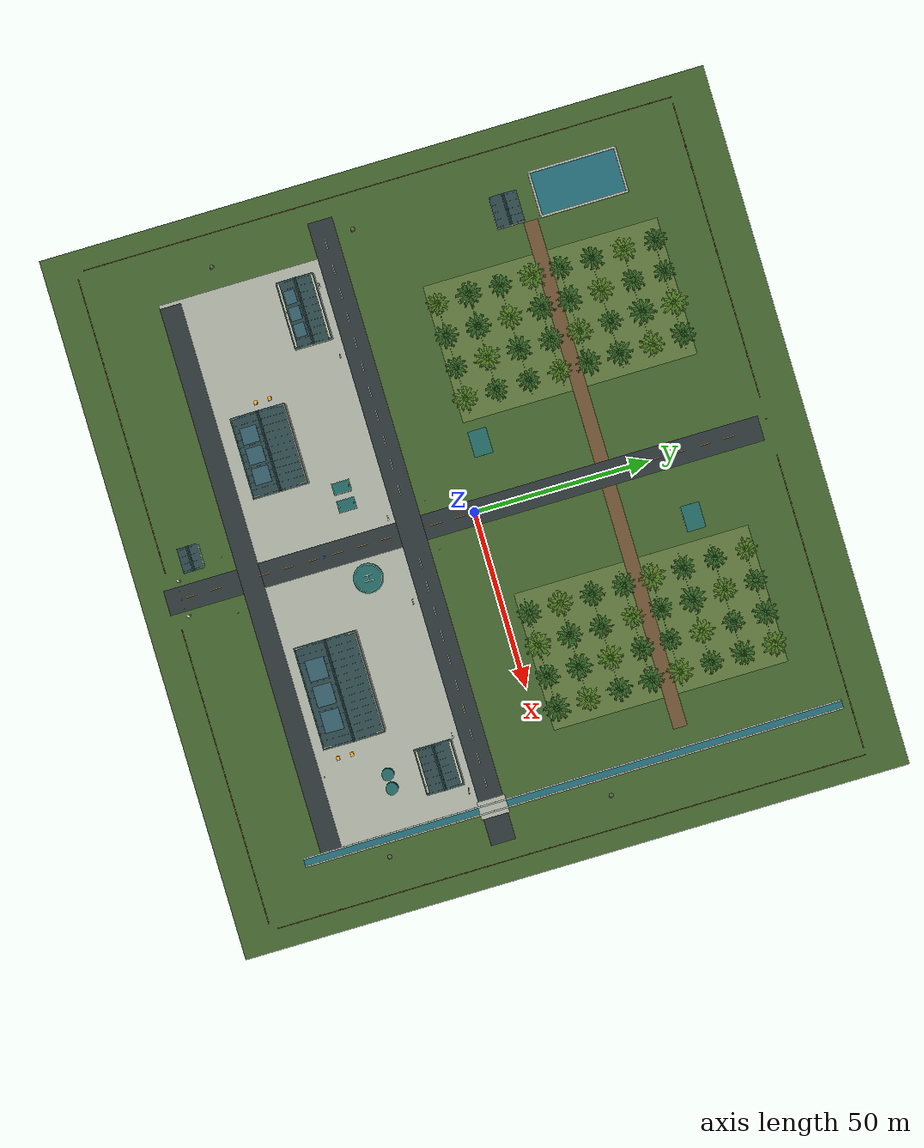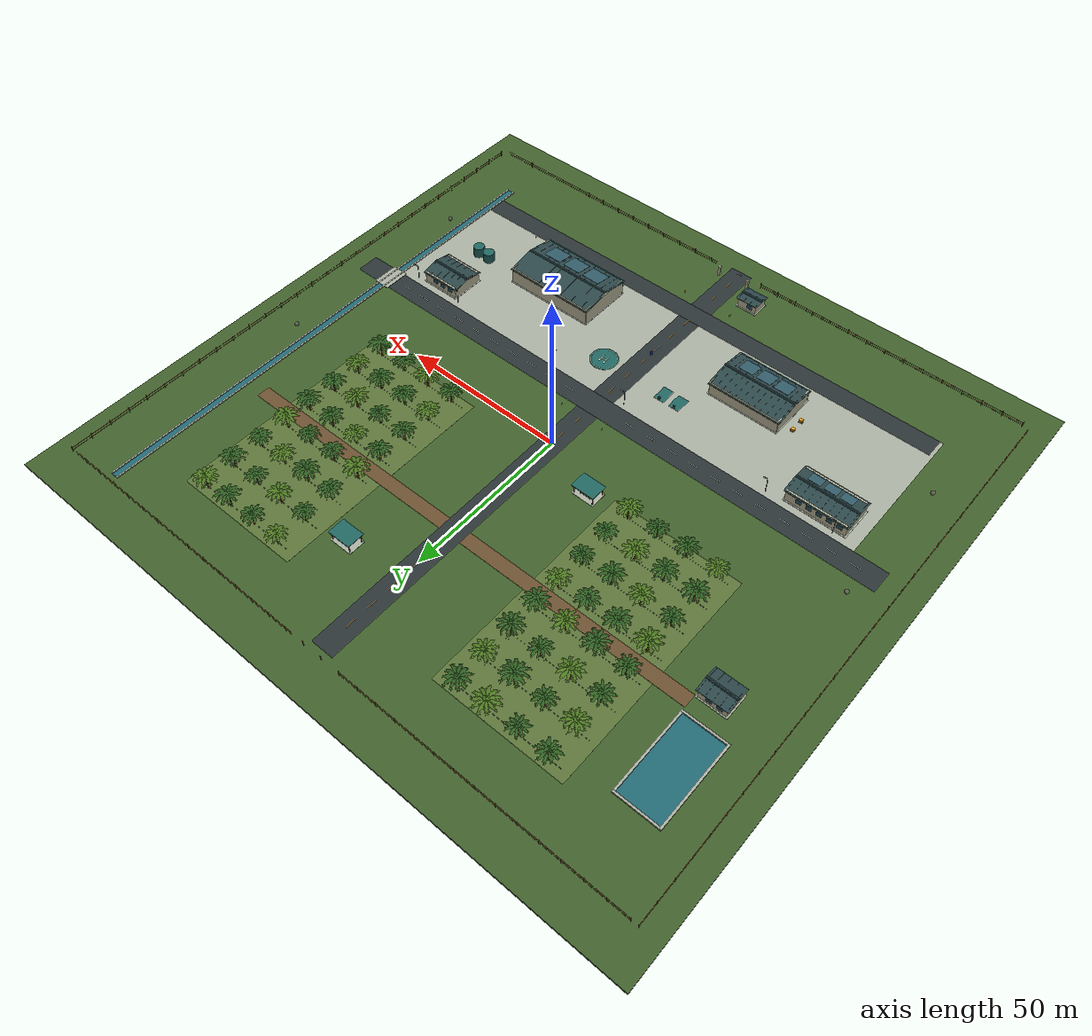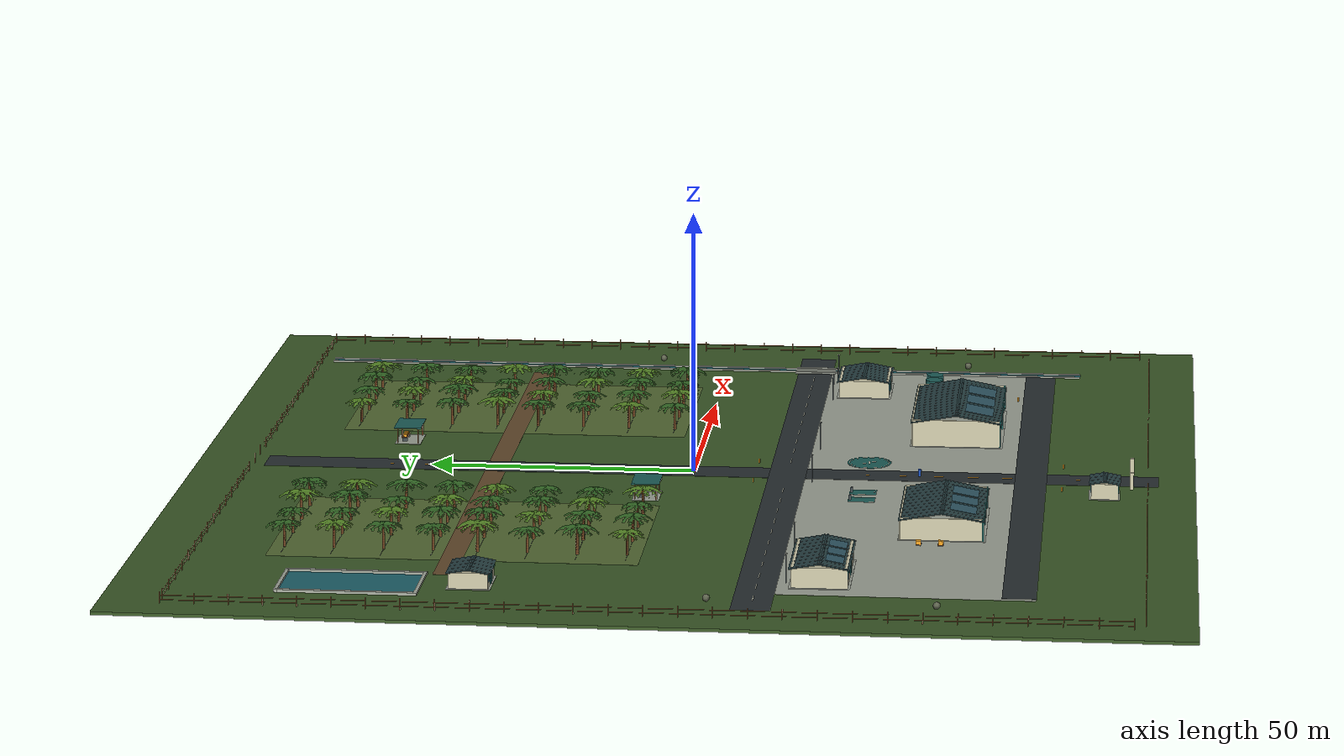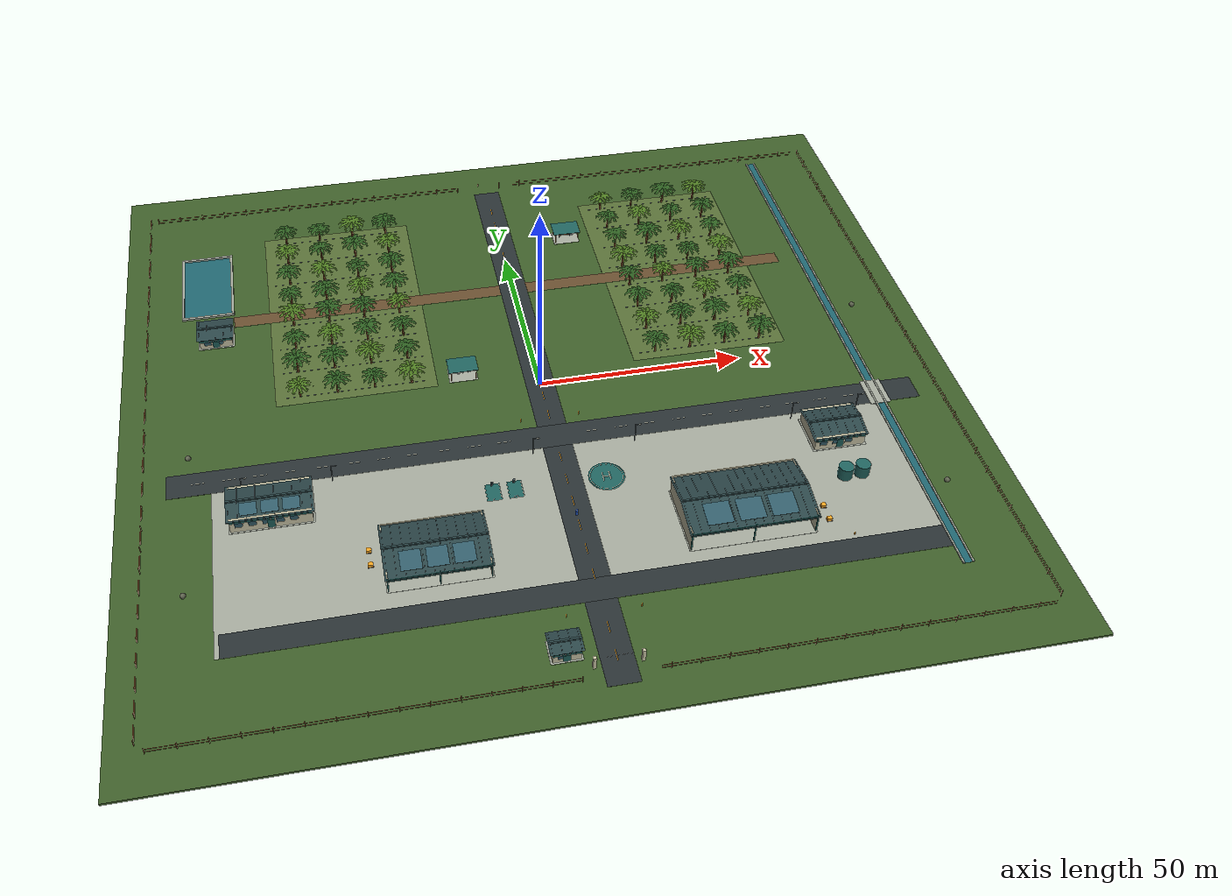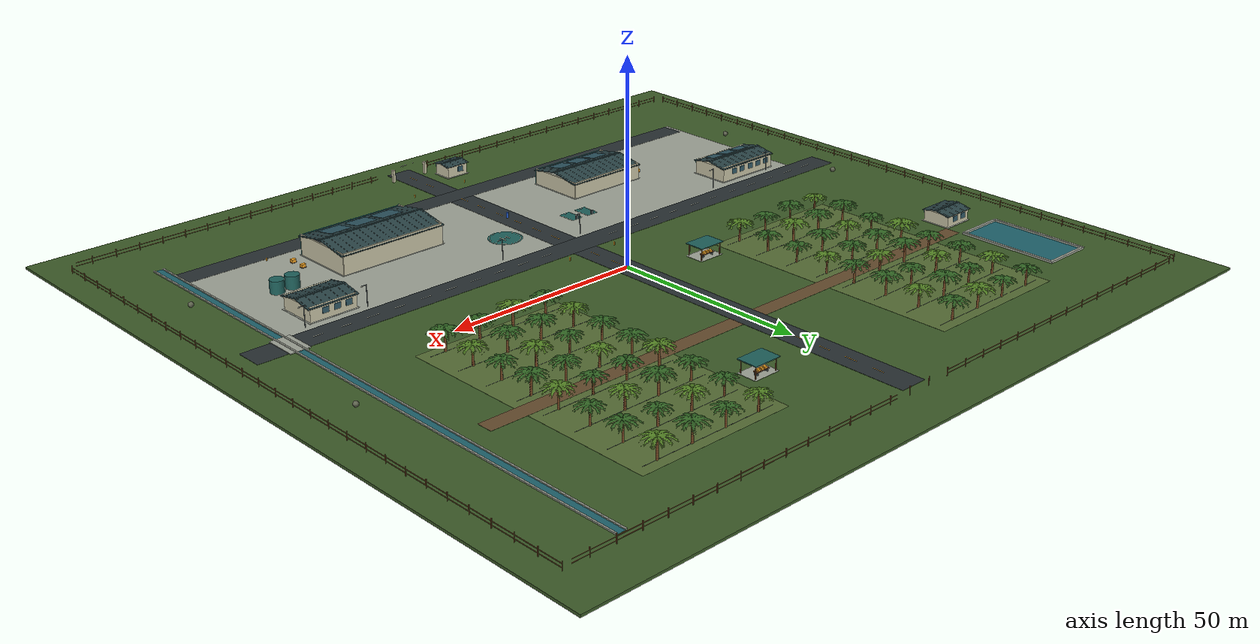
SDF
<sdf version="1.9">
 <world name="fleetscope_estate">
  <gravity>0 0 -9.81</gravity>
  <physics name="estate_physics" type="ignored">
   <max_step_size>.004</max_step_size>
   <real_time_factor>1</real_time_factor>
  </physics>
  <plugin filename="libignition-gazebo-physics-system.so" name="ignition::gazebo::systems::Physics"/>
  <plugin filename="libignition-gazebo-user-commands-system.so" name="ignition::gazebo::systems::UserCommands"/>
  <plugin filename="libignition-gazebo-scene-broadcaster-system.so" name="ignition::gazebo::systems::SceneBroadcaster"/>
  <plugin filename="libignition-gazebo-sensors-system.so" name="ignition::gazebo::systems::Sensors">
   <render_engine>ogre2</render_engine>
  </plugin>
  <scene><ambient>.65 .65 .65 1</ambient><background>.70 .82 .89 1</background><shadows>true</shadows></scene>
  <light name="estate_sun" type="directional">
   <pose>0 0 100 0 0 0</pose>
   <diffuse>.95 .91 .81 1</diffuse>
   <specular>.2 .2 .2 1</specular>
   <direction>-.4 .3 -1</direction>
  </light>
  <model name="estate_ground">
   <static>true</static>
   <link name="structure">
    <visual name="visual_0">
     <pose>0 0 -0.3 0 0 0</pose>
     <geometry><box><size>200 190 0.6</size></box></geometry>
     <material>
      <ambient>0.24 0.36 0.16 1</ambient>
      <diffuse>0.24 0.36 0.16 1</diffuse>
      <specular>.08 .08 .08 1</specular>
     </material>
    </visual>
    <collision name="collision_0">
     <pose>0 0 -0.3 0 0 0</pose>
     <geometry><box><size>200 190 0.6</size></box></geometry>
    </collision>
   </link>
  </model>
  <model name="campus_apron">
   <static>true</static>
   <link name="structure">
    <visual name="visual_0">
     <pose>0 -43 0.015 0 0 0</pose>
     <geometry><box><size>158 48 0.03</size></box></geometry>
     <material>
      <ambient>0.63 0.65 0.6 1</ambient>
      <diffuse>0.63 0.65 0.6 1</diffuse>
      <specular>.08 .08 .08 1</specular>
     </material>
     <cast_shadows>false</cast_shadows>
    </visual>
    <collision name="collision_0">
     <pose>0 -43 0.015 0 0 0</pose>
     <geometry><box><size>158 48 0.03</size></box></geometry>
    </collision>
   </link>
  </model>
  <model name="service_roads">
   <static>true</static>
   <link name="structure">
    <visual name="visual_0">
     <pose>0 -3 0.035 0 0 0</pose>
     <geometry><box><size>7 170 0.05</size></box></geometry>
     <material>
      <ambient>0.16 0.19 0.2 1</ambient>
      <diffuse>0.16 0.19 0.2 1</diffuse>
      <specular>.08 .08 .08 1</specular>
     </material>
     <cast_shadows>false</cast_shadows>
    </visual>
    <collision name="collision_0">
     <pose>0 -3 0.035 0 0 0</pose>
     <geometry><box><size>7 170 0.05</size></box></geometry>
    </collision>
    <visual name="visual_1">
     <pose>0 -18 0.036 0 0 0</pose>
     <geometry><box><size>178 7 0.05</size></box></geometry>
     <material>
      <ambient>0.16 0.19 0.2 1</ambient>
      <diffuse>0.16 0.19 0.2 1</diffuse>
      <specular>.08 .08 .08 1</specular>
     </material>
     <cast_shadows>false</cast_shadows>
    </visual>
    <collision name="collision_1">
     <pose>0 -18 0.036 0 0 0</pose>
     <geometry><box><size>178 7 0.05</size></box></geometry>
    </collision>
    <visual name="visual_2">
     <pose>0 -64 0.036 0 0 0</pose>
     <geometry><box><size>156 6 0.05</size></box></geometry>
     <material>
      <ambient>0.16 0.19 0.2 1</ambient>
      <diffuse>0.16 0.19 0.2 1</diffuse>
      <specular>.08 .08 .08 1</specular>
     </material>
     <cast_shadows>false</cast_shadows>
    </visual>
    <collision name="collision_2">
     <pose>0 -64 0.036 0 0 0</pose>
     <geometry><box><size>156 6 0.05</size></box></geometry>
    </collision>
    <visual name="visual_3">
     <pose>0 37.5 0.025 0 0 0</pose>
     <geometry><box><size>145 4 0.03</size></box></geometry>
     <material>
      <ambient>0.4 0.3 0.18 1</ambient>
      <diffuse>0.4 0.3 0.18 1</diffuse>
      <specular>.08 .08 .08 1</specular>
     </material>
     <cast_shadows>false</cast_shadows>
    </visual>
    <collision name="collision_3">
     <pose>0 37.5 0.025 0 0 0</pose>
     <geometry><box><size>145 4 0.03</size></box></geometry>
    </collision>
    <visual name="visual_4">
     <pose>0 -81 0.065 0 0 0</pose>
     <geometry><box><size>0.15 3 0.009</size></box></geometry>
     <material>
      <ambient>0.95 0.64 0.13 1</ambient>
      <diffuse>0.95 0.64 0.13 1</diffuse>
      <specular>.08 .08 .08 1</specular>
     </material>
     <cast_shadows>false</cast_shadows>
    </visual>
    <visual name="visual_5">
     <pose>0 -74 0.065 0 0 0</pose>
     <geometry><box><size>0.15 3 0.009</size></box></geometry>
     <material>
      <ambient>0.95 0.64 0.13 1</ambient>
      <diffuse>0.95 0.64 0.13 1</diffuse>
      <specular>.08 .08 .08 1</specular>
     </material>
     <cast_shadows>false</cast_shadows>
    </visual>
    <visual name="visual_6">
     <pose>0 -60 0.065 0 0 0</pose>
     <geometry><box><size>0.15 3 0.009</size></box></geometry>
     <material>
      <ambient>0.95 0.64 0.13 1</ambient>
      <diffuse>0.95 0.64 0.13 1</diffuse>
      <specular>.08 .08 .08 1</specular>
     </material>
     <cast_shadows>false</cast_shadows>
    </visual>
    <visual name="visual_7">
     <pose>0 -53 0.065 0 0 0</pose>
     <geometry><box><size>0.15 3 0.009</size></box></geometry>
     <material>
      <ambient>0.95 0.64 0.13 1</ambient>
      <diffuse>0.95 0.64 0.13 1</diffuse>
      <specular>.08 .08 .08 1</specular>
     </material>
     <cast_shadows>false</cast_shadows>
    </visual>
    <visual name="visual_8">
     <pose>0 -46 0.065 0 0 0</pose>
     <geometry><box><size>0.15 3 0.009</size></box></geometry>
     <material>
      <ambient>0.95 0.64 0.13 1</ambient>
      <diffuse>0.95 0.64 0.13 1</diffuse>
      <specular>.08 .08 .08 1</specular>
     </material>
     <cast_shadows>false</cast_shadows>
    </visual>
    <visual name="visual_9">
     <pose>0 -39 0.065 0 0 0</pose>
     <geometry><box><size>0.15 3 0.009</size></box></geometry>
     <material>
      <ambient>0.95 0.64 0.13 1</ambient>
      <diffuse>0.95 0.64 0.13 1</diffuse>
      <specular>.08 .08 .08 1</specular>
     </material>
     <cast_shadows>false</cast_shadows>
    </visual>
    <visual name="visual_10">
     <pose>0 -32 0.065 0 0 0</pose>
     <geometry><box><size>0.15 3 0.009</size></box></geometry>
     <material>
      <ambient>0.95 0.64 0.13 1</ambient>
      <diffuse>0.95 0.64 0.13 1</diffuse>
      <specular>.08 .08 .08 1</specular>
     </material>
     <cast_shadows>false</cast_shadows>
    </visual>
    <visual name="visual_11">
     <pose>0 -25 0.065 0 0 0</pose>
     <geometry><box><size>0.15 3 0.009</size></box></geometry>
     <material>
      <ambient>0.95 0.64 0.13 1</ambient>
      <diffuse>0.95 0.64 0.13 1</diffuse>
      <specular>.08 .08 .08 1</specular>
     </material>
     <cast_shadows>false</cast_shadows>
    </visual>
    <visual name="visual_12">
     <pose>0 -11 0.065 0 0 0</pose>
     <geometry><box><size>0.15 3 0.009</size></box></geometry>
     <material>
      <ambient>0.95 0.64 0.13 1</ambient>
      <diffuse>0.95 0.64 0.13 1</diffuse>
      <specular>.08 .08 .08 1</specular>
     </material>
     <cast_shadows>false</cast_shadows>
    </visual>
    <visual name="visual_13">
     <pose>0 -4 0.065 0 0 0</pose>
     <geometry><box><size>0.15 3 0.009</size></box></geometry>
     <material>
      <ambient>0.95 0.64 0.13 1</ambient>
      <diffuse>0.95 0.64 0.13 1</diffuse>
      <specular>.08 .08 .08 1</specular>
     </material>
     <cast_shadows>false</cast_shadows>
    </visual>
    <visual name="visual_14">
     <pose>0 3 0.065 0 0 0</pose>
     <geometry><box><size>0.15 3 0.009</size></box></geometry>
     <material>
      <ambient>0.95 0.64 0.13 1</ambient>
      <diffuse>0.95 0.64 0.13 1</diffuse>
      <specular>.08 .08 .08 1</specular>
     </material>
     <cast_shadows>false</cast_shadows>
    </visual>
    <visual name="visual_15">
     <pose>0 10 0.065 0 0 0</pose>
     <geometry><box><size>0.15 3 0.009</size></box></geometry>
     <material>
      <ambient>0.95 0.64 0.13 1</ambient>
      <diffuse>0.95 0.64 0.13 1</diffuse>
      <specular>.08 .08 .08 1</specular>
     </material>
     <cast_shadows>false</cast_shadows>
    </visual>
    <visual name="visual_16">
     <pose>0 17 0.065 0 0 0</pose>
     <geometry><box><size>0.15 3 0.009</size></box></geometry>
     <material>
      <ambient>0.95 0.64 0.13 1</ambient>
      <diffuse>0.95 0.64 0.13 1</diffuse>
      <specular>.08 .08 .08 1</specular>
     </material>
     <cast_shadows>false</cast_shadows>
    </visual>
    <visual name="visual_17">
     <pose>0 24 0.065 0 0 0</pose>
     <geometry><box><size>0.15 3 0.009</size></box></geometry>
     <material>
      <ambient>0.95 0.64 0.13 1</ambient>
      <diffuse>0.95 0.64 0.13 1</diffuse>
      <specular>.08 .08 .08 1</specular>
     </material>
     <cast_shadows>false</cast_shadows>
    </visual>
    <visual name="visual_18">
     <pose>0 31 0.065 0 0 0</pose>
     <geometry><box><size>0.15 3 0.009</size></box></geometry>
     <material>
      <ambient>0.95 0.64 0.13 1</ambient>
      <diffuse>0.95 0.64 0.13 1</diffuse>
      <specular>.08 .08 .08 1</specular>
     </material>
     <cast_shadows>false</cast_shadows>
    </visual>
    <visual name="visual_19">
     <pose>0 38 0.065 0 0 0</pose>
     <geometry><box><size>0.15 3 0.009</size></box></geometry>
     <material>
      <ambient>0.95 0.64 0.13 1</ambient>
      <diffuse>0.95 0.64 0.13 1</diffuse>
      <specular>.08 .08 .08 1</specular>
     </material>
     <cast_shadows>false</cast_shadows>
    </visual>
    <visual name="visual_20">
     <pose>0 45 0.065 0 0 0</pose>
     <geometry><box><size>0.15 3 0.009</size></box></geometry>
     <material>
      <ambient>0.95 0.64 0.13 1</ambient>
      <diffuse>0.95 0.64 0.13 1</diffuse>
      <specular>.08 .08 .08 1</specular>
     </material>
     <cast_shadows>false</cast_shadows>
    </visual>
    <visual name="visual_21">
     <pose>0 52 0.065 0 0 0</pose>
     <geometry><box><size>0.15 3 0.009</size></box></geometry>
     <material>
      <ambient>0.95 0.64 0.13 1</ambient>
      <diffuse>0.95 0.64 0.13 1</diffuse>
      <specular>.08 .08 .08 1</specular>
     </material>
     <cast_shadows>false</cast_shadows>
    </visual>
    <visual name="visual_22">
     <pose>0 59 0.065 0 0 0</pose>
     <geometry><box><size>0.15 3 0.009</size></box></geometry>
     <material>
      <ambient>0.95 0.64 0.13 1</ambient>
      <diffuse>0.95 0.64 0.13 1</diffuse>
      <specular>.08 .08 .08 1</specular>
     </material>
     <cast_shadows>false</cast_shadows>
    </visual>
    <visual name="visual_23">
     <pose>0 66 0.065 0 0 0</pose>
     <geometry><box><size>0.15 3 0.009</size></box></geometry>
     <material>
      <ambient>0.95 0.64 0.13 1</ambient>
      <diffuse>0.95 0.64 0.13 1</diffuse>
      <specular>.08 .08 .08 1</specular>
     </material>
     <cast_shadows>false</cast_shadows>
    </visual>
    <visual name="visual_24">
     <pose>0 73 0.065 0 0 0</pose>
     <geometry><box><size>0.15 3 0.009</size></box></geometry>
     <material>
      <ambient>0.95 0.64 0.13 1</ambient>
      <diffuse>0.95 0.64 0.13 1</diffuse>
      <specular>.08 .08 .08 1</specular>
     </material>
     <cast_shadows>false</cast_shadows>
    </visual>
    <visual name="visual_25">
     <pose>-82 -18 0.07 0 0 0</pose>
     <geometry><box><size>3 0.15 0.009</size></box></geometry>
     <material>
      <ambient>0.9 0.9 0.81 1</ambient>
      <diffuse>0.9 0.9 0.81 1</diffuse>
      <specular>.08 .08 .08 1</specular>
     </material>
     <cast_shadows>false</cast_shadows>
    </visual>
    <visual name="visual_26">
     <pose>-75 -18 0.07 0 0 0</pose>
     <geometry><box><size>3 0.15 0.009</size></box></geometry>
     <material>
      <ambient>0.9 0.9 0.81 1</ambient>
      <diffuse>0.9 0.9 0.81 1</diffuse>
      <specular>.08 .08 .08 1</specular>
     </material>
     <cast_shadows>false</cast_shadows>
    </visual>
    <visual name="visual_27">
     <pose>-68 -18 0.07 0 0 0</pose>
     <geometry><box><size>3 0.15 0.009</size></box></geometry>
     <material>
      <ambient>0.9 0.9 0.81 1</ambient>
      <diffuse>0.9 0.9 0.81 1</diffuse>
      <specular>.08 .08 .08 1</specular>
     </material>
     <cast_shadows>false</cast_shadows>
    </visual>
    <visual name="visual_28">
     <pose>-61 -18 0.07 0 0 0</pose>
     <geometry><box><size>3 0.15 0.009</size></box></geometry>
     <material>
      <ambient>0.9 0.9 0.81 1</ambient>
      <diffuse>0.9 0.9 0.81 1</diffuse>
      <specular>.08 .08 .08 1</specular>
     </material>
     <cast_shadows>false</cast_shadows>
    </visual>
    <visual name="visual_29">
     <pose>-54 -18 0.07 0 0 0</pose>
     <geometry><box><size>3 0.15 0.009</size></box></geometry>
     <material>
      <ambient>0.9 0.9 0.81 1</ambient>
      <diffuse>0.9 0.9 0.81 1</diffuse>
      <specular>.08 .08 .08 1</specular>
     </material>
     <cast_shadows>false</cast_shadows>
    </visual>
    <visual name="visual_30">
     <pose>-47 -18 0.07 0 0 0</pose>
     <geometry><box><size>3 0.15 0.009</size></box></geometry>
     <material>
      <ambient>0.9 0.9 0.81 1</ambient>
      <diffuse>0.9 0.9 0.81 1</diffuse>
      <specular>.08 .08 .08 1</specular>
     </material>
     <cast_shadows>false</cast_shadows>
    </visual>
    <visual name="visual_31">
     <pose>-40 -18 0.07 0 0 0</pose>
     <geometry><box><size>3 0.15 0.009</size></box></geometry>
     <material>
      <ambient>0.9 0.9 0.81 1</ambient>
      <diffuse>0.9 0.9 0.81 1</diffuse>
      <specular>.08 .08 .08 1</specular>
     </material>
     <cast_shadows>false</cast_shadows>
    </visual>
    <visual name="visual_32">
     <pose>-33 -18 0.07 0 0 0</pose>
     <geometry><box><size>3 0.15 0.009</size></box></geometry>
     <material>
      <ambient>0.9 0.9 0.81 1</ambient>
      <diffuse>0.9 0.9 0.81 1</diffuse>
      <specular>.08 .08 .08 1</specular>
     </material>
     <cast_shadows>false</cast_shadows>
    </visual>
    <visual name="visual_33">
     <pose>-26 -18 0.07 0 0 0</pose>
     <geometry><box><size>3 0.15 0.009</size></box></geometry>
     <material>
      <ambient>0.9 0.9 0.81 1</ambient>
      <diffuse>0.9 0.9 0.81 1</diffuse>
      <specular>.08 .08 .08 1</specular>
     </material>
     <cast_shadows>false</cast_shadows>
    </visual>
    <visual name="visual_34">
     <pose>-19 -18 0.07 0 0 0</pose>
     <geometry><box><size>3 0.15 0.009</size></box></geometry>
     <material>
      <ambient>0.9 0.9 0.81 1</ambient>
      <diffuse>0.9 0.9 0.81 1</diffuse>
      <specular>.08 .08 .08 1</specular>
     </material>
     <cast_shadows>false</cast_shadows>
    </visual>
    <visual name="visual_35">
     <pose>-12 -18 0.07 0 0 0</pose>
     <geometry><box><size>3 0.15 0.009</size></box></geometry>
     <material>
      <ambient>0.9 0.9 0.81 1</ambient>
      <diffuse>0.9 0.9 0.81 1</diffuse>
      <specular>.08 .08 .08 1</specular>
     </material>
     <cast_shadows>false</cast_shadows>
    </visual>
    <visual name="visual_36">
     <pose>9 -18 0.07 0 0 0</pose>
     <geometry><box><size>3 0.15 0.009</size></box></geometry>
     <material>
      <ambient>0.9 0.9 0.81 1</ambient>
      <diffuse>0.9 0.9 0.81 1</diffuse>
      <specular>.08 .08 .08 1</specular>
     </material>
     <cast_shadows>false</cast_shadows>
    </visual>
    <visual name="visual_37">
     <pose>16 -18 0.07 0 0 0</pose>
     <geometry><box><size>3 0.15 0.009</size></box></geometry>
     <material>
      <ambient>0.9 0.9 0.81 1</ambient>
      <diffuse>0.9 0.9 0.81 1</diffuse>
      <specular>.08 .08 .08 1</specular>
     </material>
     <cast_shadows>false</cast_shadows>
    </visual>
    <visual name="visual_38">
     <pose>23 -18 0.07 0 0 0</pose>
     <geometry><box><size>3 0.15 0.009</size></box></geometry>
     <material>
      <ambient>0.9 0.9 0.81 1</ambient>
      <diffuse>0.9 0.9 0.81 1</diffuse>
      <specular>.08 .08 .08 1</specular>
     </material>
     <cast_shadows>false</cast_shadows>
    </visual>
    <visual name="visual_39">
     <pose>30 -18 0.07 0 0 0</pose>
     <geometry><box><size>3 0.15 0.009</size></box></geometry>
     <material>
      <ambient>0.9 0.9 0.81 1</ambient>
      <diffuse>0.9 0.9 0.81 1</diffuse>
      <specular>.08 .08 .08 1</specular>
     </material>
     <cast_shadows>false</cast_shadows>
    </visual>
    <visual name="visual_40">
     <pose>37 -18 0.07 0 0 0</pose>
     <geometry><box><size>3 0.15 0.009</size></box></geometry>
     <material>
      <ambient>0.9 0.9 0.81 1</ambient>
      <diffuse>0.9 0.9 0.81 1</diffuse>
      <specular>.08 .08 .08 1</specular>
     </material>
     <cast_shadows>false</cast_shadows>
    </visual>
    <visual name="visual_41">
     <pose>44 -18 0.07 0 0 0</pose>
     <geometry><box><size>3 0.15 0.009</size></box></geometry>
     <material>
      <ambient>0.9 0.9 0.81 1</ambient>
      <diffuse>0.9 0.9 0.81 1</diffuse>
      <specular>.08 .08 .08 1</specular>
     </material>
     <cast_shadows>false</cast_shadows>
    </visual>
    <visual name="visual_42">
     <pose>51 -18 0.07 0 0 0</pose>
     <geometry><box><size>3 0.15 0.009</size></box></geometry>
     <material>
      <ambient>0.9 0.9 0.81 1</ambient>
      <diffuse>0.9 0.9 0.81 1</diffuse>
      <specular>.08 .08 .08 1</specular>
     </material>
     <cast_shadows>false</cast_shadows>
    </visual>
    <visual name="visual_43">
     <pose>58 -18 0.07 0 0 0</pose>
     <geometry><box><size>3 0.15 0.009</size></box></geometry>
     <material>
      <ambient>0.9 0.9 0.81 1</ambient>
      <diffuse>0.9 0.9 0.81 1</diffuse>
      <specular>.08 .08 .08 1</specular>
     </material>
     <cast_shadows>false</cast_shadows>
    </visual>
    <visual name="visual_44">
     <pose>65 -18 0.07 0 0 0</pose>
     <geometry><box><size>3 0.15 0.009</size></box></geometry>
     <material>
      <ambient>0.9 0.9 0.81 1</ambient>
      <diffuse>0.9 0.9 0.81 1</diffuse>
      <specular>.08 .08 .08 1</specular>
     </material>
     <cast_shadows>false</cast_shadows>
    </visual>
    <visual name="visual_45">
     <pose>72 -18 0.07 0 0 0</pose>
     <geometry><box><size>3 0.15 0.009</size></box></geometry>
     <material>
      <ambient>0.9 0.9 0.81 1</ambient>
      <diffuse>0.9 0.9 0.81 1</diffuse>
      <specular>.08 .08 .08 1</specular>
     </material>
     <cast_shadows>false</cast_shadows>
    </visual>
    <visual name="visual_46">
     <pose>79 -18 0.07 0 0 0</pose>
     <geometry><box><size>3 0.15 0.009</size></box></geometry>
     <material>
      <ambient>0.9 0.9 0.81 1</ambient>
      <diffuse>0.9 0.9 0.81 1</diffuse>
      <specular>.08 .08 .08 1</specular>
     </material>
     <cast_shadows>false</cast_shadows>
    </visual>
   </link>
  </model>
  <model name="plot_-44_20">
   <static>true</static>
   <pose>-44 20 0 0 0 0</pose>
   <link name="structure">
    <visual name="visual_0">
     <pose>0 0 0.008 0 0 0</pose>
     <geometry><box><size>39 32 0.016</size></box></geometry>
     <material>
      <ambient>0.34 0.43 0.21 1</ambient>
      <diffuse>0.34 0.43 0.21 1</diffuse>
      <specular>.08 .08 .08 1</specular>
     </material>
     <cast_shadows>false</cast_shadows>
    </visual>
    <collision name="collision_0">
     <pose>0 0 0.008 0 0 0</pose>
     <geometry><box><size>39 32 0.016</size></box></geometry>
    </collision>
   </link>
  </model>
  <model name="irrigation_-44_20_0">
   <static>true</static>
   <pose>-44 6.5 0 0 0 0</pose>
   <link name="structure">
    <visual name="visual_0">
     <pose>0 0 0.04 0 1.570796 0</pose>
     <geometry><cylinder><radius>0.035</radius><length>35</length></cylinder></geometry>
     <material>
      <ambient>0.25 0.29 0.3 1</ambient>
      <diffuse>0.25 0.29 0.3 1</diffuse>
      <specular>.08 .08 .08 1</specular>
     </material>
    </visual>
    <collision name="collision_0">
     <pose>0 0 0.04 0 1.570796 0</pose>
     <geometry><cylinder><radius>0.035</radius><length>35</length></cylinder></geometry>
    </collision>
   </link>
  </model>
  <model name="palm_000">
   <static>true</static>
   <pose>-57.5 6.5 0 0 0 3.1574</pose>
   <link name="structure">
    <visual name="visual_0">
     <geometry>
      <mesh><uri>model://estate_palm/meshes/trunk.obj</uri><scale>0.9262064 0.9262064 0.9262064</scale></mesh>
     </geometry>
     <material>
      <ambient>0.4 0.24 0.11 1</ambient>
      <diffuse>0.4 0.24 0.11 1</diffuse>
      <specular>.08 .08 .08 1</specular>
     </material>
    </visual>
    <visual name="visual_1">
     <geometry>
      <mesh><uri>model://estate_palm/meshes/fronds.obj</uri><scale>0.9262064 0.9262064 0.9262064</scale></mesh>
     </geometry>
     <material>
      <ambient>0.29 0.46 0.12 1</ambient>
      <diffuse>0.29 0.46 0.12 1</diffuse>
      <specular>.08 .08 .08 1</specular>
     </material>
    </visual>
    <collision name="collision_2">
     <pose>0 0 2.083964 0 0 0</pose>
     <geometry>
      <cylinder><radius>0.2408136574199387</radius><length>4.167928686114323</length></cylinder>
     </geometry>
    </collision>
   </link>
  </model>
  <model name="palm_001">
   <static>true</static>
   <pose>-48.5 6.5 0 0 0 5.403543</pose>
   <link name="structure">
    <visual name="visual_0">
     <geometry>
      <mesh><uri>model://estate_palm/meshes/trunk.obj</uri><scale>1.012601 1.012601 1.012601</scale></mesh>
     </geometry>
     <material>
      <ambient>0.4 0.24 0.11 1</ambient>
      <diffuse>0.4 0.24 0.11 1</diffuse>
      <specular>.08 .08 .08 1</specular>
     </material>
    </visual>
    <visual name="visual_1">
     <geometry>
      <mesh><uri>model://estate_palm/meshes/fronds.obj</uri><scale>1.012601 1.012601 1.012601</scale></mesh>
     </geometry>
     <material>
      <ambient>0.17 0.36 0.12 1</ambient>
      <diffuse>0.17 0.36 0.12 1</diffuse>
      <specular>.08 .08 .08 1</specular>
     </material>
    </visual>
    <collision name="collision_2">
     <pose>0 0 2.278352 0 0 0</pose>
     <geometry>
      <cylinder><radius>0.2632762591706197</radius><length>4.556704485645341</length></cylinder>
     </geometry>
    </collision>
   </link>
  </model>
  <model name="palm_002">
   <static>true</static>
   <pose>-39.5 6.5 0 0 0 1.402938</pose>
   <link name="structure">
    <visual name="visual_0">
     <geometry>
      <mesh><uri>model://estate_palm/meshes/trunk.obj</uri><scale>0.9225801 0.9225801 0.9225801</scale></mesh>
     </geometry>
     <material>
      <ambient>0.4 0.24 0.11 1</ambient>
      <diffuse>0.4 0.24 0.11 1</diffuse>
      <specular>.08 .08 .08 1</specular>
     </material>
    </visual>
    <visual name="visual_1">
     <geometry>
      <mesh><uri>model://estate_palm/meshes/fronds.obj</uri><scale>0.9225801 0.9225801 0.9225801</scale></mesh>
     </geometry>
     <material>
      <ambient>0.17 0.36 0.12 1</ambient>
      <diffuse>0.17 0.36 0.12 1</diffuse>
      <specular>.08 .08 .08 1</specular>
     </material>
    </visual>
    <collision name="collision_2">
     <pose>0 0 2.075805 0 0 0</pose>
     <geometry>
      <cylinder><radius>0.2398708278489981</radius><length>4.151610482001891</length></cylinder>
     </geometry>
    </collision>
   </link>
  </model>
  <model name="palm_003">
   <static>true</static>
   <pose>-30.5 6.5 0 0 0 3.496963</pose>
   <link name="structure">
    <visual name="visual_0">
     <geometry>
      <mesh><uri>model://estate_palm/meshes/trunk.obj</uri><scale>1.032227 1.032227 1.032227</scale></mesh>
     </geometry>
     <material>
      <ambient>0.4 0.24 0.11 1</ambient>
      <diffuse>0.4 0.24 0.11 1</diffuse>
      <specular>.08 .08 .08 1</specular>
     </material>
    </visual>
    <visual name="visual_1">
     <geometry>
      <mesh><uri>model://estate_palm/meshes/fronds.obj</uri><scale>1.032227 1.032227 1.032227</scale></mesh>
     </geometry>
     <material>
      <ambient>0.29 0.46 0.12 1</ambient>
      <diffuse>0.29 0.46 0.12 1</diffuse>
      <specular>.08 .08 .08 1</specular>
     </material>
    </visual>
    <collision name="collision_2">
     <pose>0 0 2.32251 0 0 0</pose>
     <geometry><cylinder><radius>0.268378953316427</radius><length>4.645020345861236</length></cylinder></geometry>
    </collision>
   </link>
  </model>
  <model name="irrigation_-44_20_1">
   <static>true</static>
   <pose>-44 15.5 0 0 0 0</pose>
   <link name="structure">
    <visual name="visual_0">
     <pose>0 0 0.04 0 1.570796 0</pose>
     <geometry><cylinder><radius>0.035</radius><length>35</length></cylinder></geometry>
     <material>
      <ambient>0.25 0.29 0.3 1</ambient>
      <diffuse>0.25 0.29 0.3 1</diffuse>
      <specular>.08 .08 .08 1</specular>
     </material>
    </visual>
    <collision name="collision_0">
     <pose>0 0 0.04 0 1.570796 0</pose>
     <geometry><cylinder><radius>0.035</radius><length>35</length></cylinder></geometry>
    </collision>
   </link>
  </model>
  <model name="palm_004">
   <static>true</static>
   <pose>-57.5 15.5 0 0 0 3.442001</pose>
   <link name="structure">
    <visual name="visual_0">
     <geometry>
      <mesh><uri>model://estate_palm/meshes/trunk.obj</uri><scale>1.072342 1.072342 1.072342</scale></mesh>
     </geometry>
     <material>
      <ambient>0.4 0.24 0.11 1</ambient>
      <diffuse>0.4 0.24 0.11 1</diffuse>
      <specular>.08 .08 .08 1</specular>
     </material>
    </visual>
    <visual name="visual_1">
     <geometry>
      <mesh><uri>model://estate_palm/meshes/fronds.obj</uri><scale>1.072342 1.072342 1.072342</scale></mesh>
     </geometry>
     <material>
      <ambient>0.17 0.36 0.12 1</ambient>
      <diffuse>0.17 0.36 0.12 1</diffuse>
      <specular>.08 .08 .08 1</specular>
     </material>
    </visual>
    <collision name="collision_2">
     <pose>0 0 2.41277 0 0 0</pose>
     <geometry>
      <cylinder><radius>0.2788089574780385</radius><length>4.825539648658358</length></cylinder>
     </geometry>
    </collision>
   </link>
  </model>
  <model name="palm_005">
   <static>true</static>
   <pose>-48.5 15.5 0 0 0 4.826211</pose>
   <link name="structure">
    <visual name="visual_0">
     <geometry>
      <mesh><uri>model://estate_palm/meshes/trunk.obj</uri><scale>1.060719 1.060719 1.060719</scale></mesh>
     </geometry>
     <material>
      <ambient>0.4 0.24 0.11 1</ambient>
      <diffuse>0.4 0.24 0.11 1</diffuse>
      <specular>.08 .08 .08 1</specular>
     </material>
    </visual>
    <visual name="visual_1">
     <geometry>
      <mesh><uri>model://estate_palm/meshes/fronds.obj</uri><scale>1.060719 1.060719 1.060719</scale></mesh>
     </geometry>
     <material>
      <ambient>0.17 0.36 0.12 1</ambient>
      <diffuse>0.17 0.36 0.12 1</diffuse>
      <specular>.08 .08 .08 1</specular>
     </material>
    </visual>
    <collision name="collision_2">
     <pose>0 0 2.386617 0 0 0</pose>
     <geometry>
      <cylinder><radius>0.2757868303658065</radius><length>4.773233602485112</length></cylinder>
     </geometry>
    </collision>
   </link>
  </model>
  <model name="palm_006">
   <static>true</static>
   <pose>-39.5 15.5 0 0 0 3.685219</pose>
   <link name="structure">
    <visual name="visual_0">
     <geometry>
      <mesh><uri>model://estate_palm/meshes/trunk.obj</uri><scale>1.065226 1.065226 1.065226</scale></mesh>
     </geometry>
     <material>
      <ambient>0.4 0.24 0.11 1</ambient>
      <diffuse>0.4 0.24 0.11 1</diffuse>
      <specular>.08 .08 .08 1</specular>
     </material>
    </visual>
    <visual name="visual_1">
     <geometry>
      <mesh><uri>model://estate_palm/meshes/fronds.obj</uri><scale>1.065226 1.065226 1.065226</scale></mesh>
     </geometry>
     <material>
      <ambient>0.29 0.46 0.12 1</ambient>
      <diffuse>0.29 0.46 0.12 1</diffuse>
      <specular>.08 .08 .08 1</specular>
     </material>
    </visual>
    <collision name="collision_2">
     <pose>0 0 2.396758 0 0 0</pose>
     <geometry><cylinder><radius>0.276958684806673</radius><length>4.793515698577033</length></cylinder></geometry>
    </collision>
   </link>
  </model>
  <model name="palm_007">
   <static>true</static>
   <pose>-30.5 15.5 0 0 0 3.859159</pose>
   <link name="structure">
    <visual name="visual_0">
     <geometry>
      <mesh><uri>model://estate_palm/meshes/trunk.obj</uri><scale>0.9527855 0.9527855 0.9527855</scale></mesh>
     </geometry>
     <material>
      <ambient>0.4 0.24 0.11 1</ambient>
      <diffuse>0.4 0.24 0.11 1</diffuse>
      <specular>.08 .08 .08 1</specular>
     </material>
    </visual>
    <visual name="visual_1">
     <geometry>
      <mesh><uri>model://estate_palm/meshes/fronds.obj</uri><scale>0.9527855 0.9527855 0.9527855</scale></mesh>
     </geometry>
     <material>
      <ambient>0.17 0.36 0.12 1</ambient>
      <diffuse>0.17 0.36 0.12 1</diffuse>
      <specular>.08 .08 .08 1</specular>
     </material>
    </visual>
    <collision name="collision_2">
     <pose>0 0 2.143767 0 0 0</pose>
     <geometry>
      <cylinder><radius>0.24772422933984545</radius><length>4.287534738574248</length></cylinder>
     </geometry>
    </collision>
   </link>
  </model>
  <model name="irrigation_-44_20_2">
   <static>true</static>
   <pose>-44 24.5 0 0 0 0</pose>
   <link name="structure">
    <visual name="visual_0">
     <pose>0 0 0.04 0 1.570796 0</pose>
     <geometry><cylinder><radius>0.035</radius><length>35</length></cylinder></geometry>
     <material>
      <ambient>0.25 0.29 0.3 1</ambient>
      <diffuse>0.25 0.29 0.3 1</diffuse>
      <specular>.08 .08 .08 1</specular>
     </material>
    </visual>
    <collision name="collision_0">
     <pose>0 0 0.04 0 1.570796 0</pose>
     <geometry><cylinder><radius>0.035</radius><length>35</length></cylinder></geometry>
    </collision>
   </link>
  </model>
  <model name="palm_008">
   <static>true</static>
   <pose>-57.5 24.5 0 0 0 5.131863</pose>
   <link name="structure">
    <visual name="visual_0">
     <geometry>
      <mesh><uri>model://estate_palm/meshes/trunk.obj</uri><scale>0.924362 0.924362 0.924362</scale></mesh>
     </geometry>
     <material>
      <ambient>0.4 0.24 0.11 1</ambient>
      <diffuse>0.4 0.24 0.11 1</diffuse>
      <specular>.08 .08 .08 1</specular>
     </material>
    </visual>
    <visual name="visual_1">
     <geometry>
      <mesh><uri>model://estate_palm/meshes/fronds.obj</uri><scale>0.924362 0.924362 0.924362</scale></mesh>
     </geometry>
     <material>
      <ambient>0.17 0.36 0.12 1</ambient>
      <diffuse>0.17 0.36 0.12 1</diffuse>
      <specular>.08 .08 .08 1</specular>
     </material>
    </visual>
    <collision name="collision_2">
     <pose>0 0 2.079815 0 0 0</pose>
     <geometry>
      <cylinder><radius>0.24033413029335546</radius><length>4.159629178154229</length></cylinder>
     </geometry>
    </collision>
   </link>
  </model>
  <model name="palm_009">
   <static>true</static>
   <pose>-48.5 24.5 0 0 0 5.119305</pose>
   <link name="structure">
    <visual name="visual_0">
     <geometry>
      <mesh><uri>model://estate_palm/meshes/trunk.obj</uri><scale>0.9989241 0.9989241 0.9989241</scale></mesh>
     </geometry>
     <material>
      <ambient>0.4 0.24 0.11 1</ambient>
      <diffuse>0.4 0.24 0.11 1</diffuse>
      <specular>.08 .08 .08 1</specular>
     </material>
    </visual>
    <visual name="visual_1">
     <geometry>
      <mesh><uri>model://estate_palm/meshes/fronds.obj</uri><scale>0.9989241 0.9989241 0.9989241</scale></mesh>
     </geometry>
     <material>
      <ambient>0.29 0.46 0.12 1</ambient>
      <diffuse>0.29 0.46 0.12 1</diffuse>
      <specular>.08 .08 .08 1</specular>
     </material>
    </visual>
    <collision name="collision_2">
     <pose>0 0 2.247579 0 0 0</pose>
     <geometry><cylinder><radius>0.259720256422886</radius><length>4.495158284242257</length></cylinder></geometry>
    </collision>
   </link>
  </model>
  <model name="palm_010">
   <static>true</static>
   <pose>-39.5 24.5 0 0 0 4.268727</pose>
   <link name="structure">
    <visual name="visual_0">
     <geometry>
      <mesh><uri>model://estate_palm/meshes/trunk.obj</uri><scale>1.050739 1.050739 1.050739</scale></mesh>
     </geometry>
     <material>
      <ambient>0.4 0.24 0.11 1</ambient>
      <diffuse>0.4 0.24 0.11 1</diffuse>
      <specular>.08 .08 .08 1</specular>
     </material>
    </visual>
    <visual name="visual_1">
     <geometry>
      <mesh><uri>model://estate_palm/meshes/fronds.obj</uri><scale>1.050739 1.050739 1.050739</scale></mesh>
     </geometry>
     <material>
      <ambient>0.17 0.36 0.12 1</ambient>
      <diffuse>0.17 0.36 0.12 1</diffuse>
      <specular>.08 .08 .08 1</specular>
     </material>
    </visual>
    <collision name="collision_2">
     <pose>0 0 2.364163 0 0 0</pose>
     <geometry>
      <cylinder><radius>0.27319218545887175</radius><length>4.728326286788165</length></cylinder>
     </geometry>
    </collision>
   </link>
  </model>
  <model name="palm_011">
   <static>true</static>
   <pose>-30.5 24.5 0 0 0 1.580303</pose>
   <link name="structure">
    <visual name="visual_0">
     <geometry>
      <mesh><uri>model://estate_palm/meshes/trunk.obj</uri><scale>0.9462494 0.9462494 0.9462494</scale></mesh>
     </geometry>
     <material>
      <ambient>0.4 0.24 0.11 1</ambient>
      <diffuse>0.4 0.24 0.11 1</diffuse>
      <specular>.08 .08 .08 1</specular>
     </material>
    </visual>
    <visual name="visual_1">
     <geometry>
      <mesh><uri>model://estate_palm/meshes/fronds.obj</uri><scale>0.9462494 0.9462494 0.9462494</scale></mesh>
     </geometry>
     <material>
      <ambient>0.17 0.36 0.12 1</ambient>
      <diffuse>0.17 0.36 0.12 1</diffuse>
      <specular>.08 .08 .08 1</specular>
     </material>
    </visual>
    <collision name="collision_2">
     <pose>0 0 2.129061 0 0 0</pose>
     <geometry>
      <cylinder><radius>0.2460248506212297</radius><length>4.258122414598206</length></cylinder>
     </geometry>
    </collision>
   </link>
  </model>
  <model name="irrigation_-44_20_3">
   <static>true</static>
   <pose>-44 33.5 0 0 0 0</pose>
   <link name="structure">
    <visual name="visual_0">
     <pose>0 0 0.04 0 1.570796 0</pose>
     <geometry><cylinder><radius>0.035</radius><length>35</length></cylinder></geometry>
     <material>
      <ambient>0.25 0.29 0.3 1</ambient>
      <diffuse>0.25 0.29 0.3 1</diffuse>
      <specular>.08 .08 .08 1</specular>
     </material>
    </visual>
    <collision name="collision_0">
     <pose>0 0 0.04 0 1.570796 0</pose>
     <geometry><cylinder><radius>0.035</radius><length>35</length></cylinder></geometry>
    </collision>
   </link>
  </model>
  <model name="palm_012">
   <static>true</static>
   <pose>-57.5 33.5 0 0 0 5.839073</pose>
   <link name="structure">
    <visual name="visual_0">
     <geometry>
      <mesh><uri>model://estate_palm/meshes/trunk.obj</uri><scale>1.115581 1.115581 1.115581</scale></mesh>
     </geometry>
     <material>
      <ambient>0.4 0.24 0.11 1</ambient>
      <diffuse>0.4 0.24 0.11 1</diffuse>
      <specular>.08 .08 .08 1</specular>
     </material>
    </visual>
    <visual name="visual_1">
     <geometry>
      <mesh><uri>model://estate_palm/meshes/fronds.obj</uri><scale>1.115581 1.115581 1.115581</scale></mesh>
     </geometry>
     <material>
      <ambient>0.29 0.46 0.12 1</ambient>
      <diffuse>0.29 0.46 0.12 1</diffuse>
      <specular>.08 .08 .08 1</specular>
     </material>
    </visual>
    <collision name="collision_2">
     <pose>0 0 2.510057 0 0 0</pose>
     <geometry>
      <cylinder><radius>0.29005098631037485</radius><length>5.020113224602641</length></cylinder>
     </geometry>
    </collision>
   </link>
  </model>
  <model name="palm_013">
   <static>true</static>
   <pose>-48.5 33.5 0 0 0 6.281025</pose>
   <link name="structure">
    <visual name="visual_0">
     <geometry>
      <mesh><uri>model://estate_palm/meshes/trunk.obj</uri><scale>1.07713 1.07713 1.07713</scale></mesh>
     </geometry>
     <material>
      <ambient>0.4 0.24 0.11 1</ambient>
      <diffuse>0.4 0.24 0.11 1</diffuse>
      <specular>.08 .08 .08 1</specular>
     </material>
    </visual>
    <visual name="visual_1">
     <geometry>
      <mesh><uri>model://estate_palm/meshes/fronds.obj</uri><scale>1.07713 1.07713 1.07713</scale></mesh>
     </geometry>
     <material>
      <ambient>0.17 0.36 0.12 1</ambient>
      <diffuse>0.17 0.36 0.12 1</diffuse>
      <specular>.08 .08 .08 1</specular>
     </material>
    </visual>
    <collision name="collision_2">
     <pose>0 0 2.423542 0 0 0</pose>
     <geometry>
      <cylinder><radius>0.28005377354269406</radius><length>4.847084542085089</length></cylinder>
     </geometry>
    </collision>
   </link>
  </model>
  <model name="palm_014">
   <static>true</static>
   <pose>-39.5 33.5 0 0 0 0.4795321</pose>
   <link name="structure">
    <visual name="visual_0">
     <geometry>
      <mesh><uri>model://estate_palm/meshes/trunk.obj</uri><scale>1.012989 1.012989 1.012989</scale></mesh>
     </geometry>
     <material>
      <ambient>0.4 0.24 0.11 1</ambient>
      <diffuse>0.4 0.24 0.11 1</diffuse>
      <specular>.08 .08 .08 1</specular>
     </material>
    </visual>
    <visual name="visual_1">
     <geometry>
      <mesh><uri>model://estate_palm/meshes/fronds.obj</uri><scale>1.012989 1.012989 1.012989</scale></mesh>
     </geometry>
     <material>
      <ambient>0.17 0.36 0.12 1</ambient>
      <diffuse>0.17 0.36 0.12 1</diffuse>
      <specular>.08 .08 .08 1</specular>
     </material>
    </visual>
    <collision name="collision_2">
     <pose>0 0 2.279226 0 0 0</pose>
     <geometry>
      <cylinder><radius>0.2633772076672125</radius><length>4.558451671163293</length></cylinder>
     </geometry>
    </collision>
   </link>
  </model>
  <model name="palm_015">
   <static>true</static>
   <pose>-30.5 33.5 0 0 0 3.502565</pose>
   <link name="structure">
    <visual name="visual_0">
     <geometry>
      <mesh><uri>model://estate_palm/meshes/trunk.obj</uri><scale>0.9748868 0.9748868 0.9748868</scale></mesh>
     </geometry>
     <material>
      <ambient>0.4 0.24 0.11 1</ambient>
      <diffuse>0.4 0.24 0.11 1</diffuse>
      <specular>.08 .08 .08 1</specular>
     </material>
    </visual>
    <visual name="visual_1">
     <geometry>
      <mesh><uri>model://estate_palm/meshes/fronds.obj</uri><scale>0.9748868 0.9748868 0.9748868</scale></mesh>
     </geometry>
     <material>
      <ambient>0.29 0.46 0.12 1</ambient>
      <diffuse>0.29 0.46 0.12 1</diffuse>
      <specular>.08 .08 .08 1</specular>
     </material>
    </visual>
    <collision name="collision_2">
     <pose>0 0 2.193495 0 0 0</pose>
     <geometry>
      <cylinder><radius>0.2534705695236388</radius><length>4.386990626370671</length></cylinder>
     </geometry>
    </collision>
   </link>
  </model>
  <model name="plot_-44_55">
   <static>true</static>
   <pose>-44 55 0 0 0 0</pose>
   <link name="structure">
    <visual name="visual_0">
     <pose>0 0 0.008 0 0 0</pose>
     <geometry><box><size>39 32 0.016</size></box></geometry>
     <material>
      <ambient>0.34 0.43 0.21 1</ambient>
      <diffuse>0.34 0.43 0.21 1</diffuse>
      <specular>.08 .08 .08 1</specular>
     </material>
     <cast_shadows>false</cast_shadows>
    </visual>
    <collision name="collision_0">
     <pose>0 0 0.008 0 0 0</pose>
     <geometry><box><size>39 32 0.016</size></box></geometry>
    </collision>
   </link>
  </model>
  <model name="irrigation_-44_55_0">
   <static>true</static>
   <pose>-44 41.5 0 0 0 0</pose>
   <link name="structure">
    <visual name="visual_0">
     <pose>0 0 0.04 0 1.570796 0</pose>
     <geometry><cylinder><radius>0.035</radius><length>35</length></cylinder></geometry>
     <material>
      <ambient>0.25 0.29 0.3 1</ambient>
      <diffuse>0.25 0.29 0.3 1</diffuse>
      <specular>.08 .08 .08 1</specular>
     </material>
    </visual>
    <collision name="collision_0">
     <pose>0 0 0.04 0 1.570796 0</pose>
     <geometry><cylinder><radius>0.035</radius><length>35</length></cylinder></geometry>
    </collision>
   </link>
  </model>
  <model name="palm_016">
   <static>true</static>
   <pose>-57.5 41.5 0 0 0 2.874229</pose>
   <link name="structure">
    <visual name="visual_0">
     <geometry>
      <mesh><uri>model://estate_palm/meshes/trunk.obj</uri><scale>0.9642668 0.9642668 0.9642668</scale></mesh>
     </geometry>
     <material>
      <ambient>0.4 0.24 0.11 1</ambient>
      <diffuse>0.4 0.24 0.11 1</diffuse>
      <specular>.08 .08 .08 1</specular>
     </material>
    </visual>
    <visual name="visual_1">
     <geometry>
      <mesh><uri>model://estate_palm/meshes/fronds.obj</uri><scale>0.9642668 0.9642668 0.9642668</scale></mesh>
     </geometry>
     <material>
      <ambient>0.17 0.36 0.12 1</ambient>
      <diffuse>0.17 0.36 0.12 1</diffuse>
      <specular>.08 .08 .08 1</specular>
     </material>
    </visual>
    <collision name="collision_2">
     <pose>0 0 2.1696 0 0 0</pose>
     <geometry>
      <cylinder><radius>0.25070937121846404</radius><length>4.339200655704184</length></cylinder>
     </geometry>
    </collision>
   </link>
  </model>
  <model name="palm_017">
   <static>true</static>
   <pose>-48.5 41.5 0 0 0 4.423209</pose>
   <link name="structure">
    <visual name="visual_0">
     <geometry>
      <mesh><uri>model://estate_palm/meshes/trunk.obj</uri><scale>1.092824 1.092824 1.092824</scale></mesh>
     </geometry>
     <material>
      <ambient>0.4 0.24 0.11 1</ambient>
      <diffuse>0.4 0.24 0.11 1</diffuse>
      <specular>.08 .08 .08 1</specular>
     </material>
    </visual>
    <visual name="visual_1">
     <geometry>
      <mesh><uri>model://estate_palm/meshes/fronds.obj</uri><scale>1.092824 1.092824 1.092824</scale></mesh>
     </geometry>
     <material>
      <ambient>0.17 0.36 0.12 1</ambient>
      <diffuse>0.17 0.36 0.12 1</diffuse>
      <specular>.08 .08 .08 1</specular>
     </material>
    </visual>
    <collision name="collision_2">
     <pose>0 0 2.458855 0 0 0</pose>
     <geometry>
      <cylinder><radius>0.28413435913087637</radius><length>4.917710061880553</length></cylinder>
     </geometry>
    </collision>
   </link>
  </model>
  <model name="palm_018">
   <static>true</static>
   <pose>-39.5 41.5 0 0 0 0.1554416</pose>
   <link name="structure">
    <visual name="visual_0">
     <geometry>
      <mesh><uri>model://estate_palm/meshes/trunk.obj</uri><scale>1.027033 1.027033 1.027033</scale></mesh>
     </geometry>
     <material>
      <ambient>0.4 0.24 0.11 1</ambient>
      <diffuse>0.4 0.24 0.11 1</diffuse>
      <specular>.08 .08 .08 1</specular>
     </material>
    </visual>
    <visual name="visual_1">
     <geometry>
      <mesh><uri>model://estate_palm/meshes/fronds.obj</uri><scale>1.027033 1.027033 1.027033</scale></mesh>
     </geometry>
     <material>
      <ambient>0.29 0.46 0.12 1</ambient>
      <diffuse>0.29 0.46 0.12 1</diffuse>
      <specular>.08 .08 .08 1</specular>
     </material>
    </visual>
    <collision name="collision_2">
     <pose>0 0 2.310825 0 0 0</pose>
     <geometry>
      <cylinder><radius>0.2670286161219681</radius><length>4.621649125187909</length></cylinder>
     </geometry>
    </collision>
   </link>
  </model>
  <model name="palm_019">
   <static>true</static>
   <pose>-30.5 41.5 0 0 0 2.284203</pose>
   <link name="structure">
    <visual name="visual_0">
     <geometry>
      <mesh><uri>model://estate_palm/meshes/trunk.obj</uri><scale>1.05639 1.05639 1.05639</scale></mesh>
     </geometry>
     <material>
      <ambient>0.4 0.24 0.11 1</ambient>
      <diffuse>0.4 0.24 0.11 1</diffuse>
      <specular>.08 .08 .08 1</specular>
     </material>
    </visual>
    <visual name="visual_1">
     <geometry>
      <mesh><uri>model://estate_palm/meshes/fronds.obj</uri><scale>1.05639 1.05639 1.05639</scale></mesh>
     </geometry>
     <material>
      <ambient>0.17 0.36 0.12 1</ambient>
      <diffuse>0.17 0.36 0.12 1</diffuse>
      <specular>.08 .08 .08 1</specular>
     </material>
    </visual>
    <collision name="collision_2">
     <pose>0 0 2.376877 0 0 0</pose>
     <geometry>
      <cylinder><radius>0.27466132549567457</radius><length>4.7537537105020595</length></cylinder>
     </geometry>
    </collision>
   </link>
  </model>
  <model name="irrigation_-44_55_1">
   <static>true</static>
   <pose>-44 50.5 0 0 0 0</pose>
   <link name="structure">
    <visual name="visual_0">
     <pose>0 0 0.04 0 1.570796 0</pose>
     <geometry><cylinder><radius>0.035</radius><length>35</length></cylinder></geometry>
     <material>
      <ambient>0.25 0.29 0.3 1</ambient>
      <diffuse>0.25 0.29 0.3 1</diffuse>
      <specular>.08 .08 .08 1</specular>
     </material>
    </visual>
    <collision name="collision_0">
     <pose>0 0 0.04 0 1.570796 0</pose>
     <geometry><cylinder><radius>0.035</radius><length>35</length></cylinder></geometry>
    </collision>
   </link>
  </model>
  <model name="palm_020">
   <static>true</static>
   <pose>-57.5 50.5 0 0 0 2.505567</pose>
   <link name="structure">
    <visual name="visual_0">
     <geometry>
      <mesh><uri>model://estate_palm/meshes/trunk.obj</uri><scale>0.9928878 0.9928878 0.9928878</scale></mesh>
     </geometry>
     <material>
      <ambient>0.4 0.24 0.11 1</ambient>
      <diffuse>0.4 0.24 0.11 1</diffuse>
      <specular>.08 .08 .08 1</specular>
     </material>
    </visual>
    <visual name="visual_1">
     <geometry>
      <mesh><uri>model://estate_palm/meshes/fronds.obj</uri><scale>0.9928878 0.9928878 0.9928878</scale></mesh>
     </geometry>
     <material>
      <ambient>0.17 0.36 0.12 1</ambient>
      <diffuse>0.17 0.36 0.12 1</diffuse>
      <specular>.08 .08 .08 1</specular>
     </material>
    </visual>
    <collision name="collision_2">
     <pose>0 0 2.233998 0 0 0</pose>
     <geometry>
      <cylinder><radius>0.2581508407949443</radius><length>4.467995321450959</length></cylinder>
     </geometry>
    </collision>
   </link>
  </model>
  <model name="palm_021">
   <static>true</static>
   <pose>-48.5 50.5 0 0 0 3.131886</pose>
   <link name="structure">
    <visual name="visual_0">
     <geometry>
      <mesh><uri>model://estate_palm/meshes/trunk.obj</uri><scale>1.028858 1.028858 1.028858</scale></mesh>
     </geometry>
     <material>
      <ambient>0.4 0.24 0.11 1</ambient>
      <diffuse>0.4 0.24 0.11 1</diffuse>
      <specular>.08 .08 .08 1</specular>
     </material>
    </visual>
    <visual name="visual_1">
     <geometry>
      <mesh><uri>model://estate_palm/meshes/fronds.obj</uri><scale>1.028858 1.028858 1.028858</scale></mesh>
     </geometry>
     <material>
      <ambient>0.29 0.46 0.12 1</ambient>
      <diffuse>0.29 0.46 0.12 1</diffuse>
      <specular>.08 .08 .08 1</specular>
     </material>
    </visual>
    <collision name="collision_2">
     <pose>0 0 2.31493 0 0 0</pose>
     <geometry><cylinder><radius>0.267503059093017</radius><length>4.629860638148371</length></cylinder></geometry>
    </collision>
   </link>
  </model>
  <model name="palm_022">
   <static>true</static>
   <pose>-39.5 50.5 0 0 0 3.181546</pose>
   <link name="structure">
    <visual name="visual_0">
     <geometry>
      <mesh><uri>model://estate_palm/meshes/trunk.obj</uri><scale>0.9256185 0.9256185 0.9256185</scale></mesh>
     </geometry>
     <material>
      <ambient>0.4 0.24 0.11 1</ambient>
      <diffuse>0.4 0.24 0.11 1</diffuse>
      <specular>.08 .08 .08 1</specular>
     </material>
    </visual>
    <visual name="visual_1">
     <geometry>
      <mesh><uri>model://estate_palm/meshes/fronds.obj</uri><scale>0.9256185 0.9256185 0.9256185</scale></mesh>
     </geometry>
     <material>
      <ambient>0.17 0.36 0.12 1</ambient>
      <diffuse>0.17 0.36 0.12 1</diffuse>
      <specular>.08 .08 .08 1</specular>
     </material>
    </visual>
    <collision name="collision_2">
     <pose>0 0 2.082642 0 0 0</pose>
     <geometry>
      <cylinder><radius>0.24066082237612724</radius><length>4.165283464202202</length></cylinder>
     </geometry>
    </collision>
   </link>
  </model>
  <model name="palm_023">
   <static>true</static>
   <pose>-30.5 50.5 0 0 0 3.770949</pose>
   <link name="structure">
    <visual name="visual_0">
     <geometry>
      <mesh><uri>model://estate_palm/meshes/trunk.obj</uri><scale>1.065032 1.065032 1.065032</scale></mesh>
     </geometry>
     <material>
      <ambient>0.4 0.24 0.11 1</ambient>
      <diffuse>0.4 0.24 0.11 1</diffuse>
      <specular>.08 .08 .08 1</specular>
     </material>
    </visual>
    <visual name="visual_1">
     <geometry>
      <mesh><uri>model://estate_palm/meshes/fronds.obj</uri><scale>1.065032 1.065032 1.065032</scale></mesh>
     </geometry>
     <material>
      <ambient>0.17 0.36 0.12 1</ambient>
      <diffuse>0.17 0.36 0.12 1</diffuse>
      <specular>.08 .08 .08 1</specular>
     </material>
    </visual>
    <collision name="collision_2">
     <pose>0 0 2.396323 0 0 0</pose>
     <geometry>
      <cylinder><radius>0.2769083964078007</radius><length>4.792645322442704</length></cylinder>
     </geometry>
    </collision>
   </link>
  </model>
  <model name="irrigation_-44_55_2">
   <static>true</static>
   <pose>-44 59.5 0 0 0 0</pose>
   <link name="structure">
    <visual name="visual_0">
     <pose>0 0 0.04 0 1.570796 0</pose>
     <geometry><cylinder><radius>0.035</radius><length>35</length></cylinder></geometry>
     <material>
      <ambient>0.25 0.29 0.3 1</ambient>
      <diffuse>0.25 0.29 0.3 1</diffuse>
      <specular>.08 .08 .08 1</specular>
     </material>
    </visual>
    <collision name="collision_0">
     <pose>0 0 0.04 0 1.570796 0</pose>
     <geometry><cylinder><radius>0.035</radius><length>35</length></cylinder></geometry>
    </collision>
   </link>
  </model>
  <model name="palm_024">
   <static>true</static>
   <pose>-57.5 59.5 0 0 0 5.760139</pose>
   <link name="structure">
    <visual name="visual_0">
     <geometry>
      <mesh><uri>model://estate_palm/meshes/trunk.obj</uri><scale>1.008027 1.008027 1.008027</scale></mesh>
     </geometry>
     <material>
      <ambient>0.4 0.24 0.11 1</ambient>
      <diffuse>0.4 0.24 0.11 1</diffuse>
      <specular>.08 .08 .08 1</specular>
     </material>
    </visual>
    <visual name="visual_1">
     <geometry>
      <mesh><uri>model://estate_palm/meshes/fronds.obj</uri><scale>1.008027 1.008027 1.008027</scale></mesh>
     </geometry>
     <material>
      <ambient>0.29 0.46 0.12 1</ambient>
      <diffuse>0.29 0.46 0.12 1</diffuse>
      <specular>.08 .08 .08 1</specular>
     </material>
    </visual>
    <collision name="collision_2">
     <pose>0 0 2.26806 0 0 0</pose>
     <geometry>
      <cylinder><radius>0.2620869566647268</radius><length>4.536120403812579</length></cylinder>
     </geometry>
    </collision>
   </link>
  </model>
  <model name="palm_025">
   <static>true</static>
   <pose>-48.5 59.5 0 0 0 2.638725</pose>
   <link name="structure">
    <visual name="visual_0">
     <geometry>
      <mesh><uri>model://estate_palm/meshes/trunk.obj</uri><scale>0.9569016 0.9569016 0.9569016</scale></mesh>
     </geometry>
     <material>
      <ambient>0.4 0.24 0.11 1</ambient>
      <diffuse>0.4 0.24 0.11 1</diffuse>
      <specular>.08 .08 .08 1</specular>
     </material>
    </visual>
    <visual name="visual_1">
     <geometry>
      <mesh><uri>model://estate_palm/meshes/fronds.obj</uri><scale>0.9569016 0.9569016 0.9569016</scale></mesh>
     </geometry>
     <material>
      <ambient>0.17 0.36 0.12 1</ambient>
      <diffuse>0.17 0.36 0.12 1</diffuse>
      <specular>.08 .08 .08 1</specular>
     </material>
    </visual>
    <collision name="collision_2">
     <pose>0 0 2.153028 0 0 0</pose>
     <geometry>
      <cylinder><radius>0.2487944043271551</radius><length>4.306056997969992</length></cylinder>
     </geometry>
    </collision>
   </link>
  </model>
  <model name="palm_026">
   <static>true</static>
   <pose>-39.5 59.5 0 0 0 3.010839</pose>
   <link name="structure">
    <visual name="visual_0">
     <geometry>
      <mesh><uri>model://estate_palm/meshes/trunk.obj</uri><scale>1.103771 1.103771 1.103771</scale></mesh>
     </geometry>
     <material>
      <ambient>0.4 0.24 0.11 1</ambient>
      <diffuse>0.4 0.24 0.11 1</diffuse>
      <specular>.08 .08 .08 1</specular>
     </material>
    </visual>
    <visual name="visual_1">
     <geometry>
      <mesh><uri>model://estate_palm/meshes/fronds.obj</uri><scale>1.103771 1.103771 1.103771</scale></mesh>
     </geometry>
     <material>
      <ambient>0.17 0.36 0.12 1</ambient>
      <diffuse>0.17 0.36 0.12 1</diffuse>
      <specular>.08 .08 .08 1</specular>
     </material>
    </visual>
    <collision name="collision_2">
     <pose>0 0 2.483485 0 0 0</pose>
     <geometry>
      <cylinder><radius>0.2869805344714632</radius><length>4.966970788929171</length></cylinder>
     </geometry>
    </collision>
   </link>
  </model>
  <model name="palm_027">
   <static>true</static>
   <pose>-30.5 59.5 0 0 0 0.159443</pose>
   <link name="structure">
    <visual name="visual_0">
     <geometry>
      <mesh><uri>model://estate_palm/meshes/trunk.obj</uri><scale>1.013957 1.013957 1.013957</scale></mesh>
     </geometry>
     <material>
      <ambient>0.4 0.24 0.11 1</ambient>
      <diffuse>0.4 0.24 0.11 1</diffuse>
      <specular>.08 .08 .08 1</specular>
     </material>
    </visual>
    <visual name="visual_1">
     <geometry>
      <mesh><uri>model://estate_palm/meshes/fronds.obj</uri><scale>1.013957 1.013957 1.013957</scale></mesh>
     </geometry>
     <material>
      <ambient>0.29 0.46 0.12 1</ambient>
      <diffuse>0.29 0.46 0.12 1</diffuse>
      <specular>.08 .08 .08 1</specular>
     </material>
    </visual>
    <collision name="collision_2">
     <pose>0 0 2.281404 0 0 0</pose>
     <geometry>
      <cylinder><radius>0.26362886983793904</radius><length>4.562807362579713</length></cylinder>
     </geometry>
    </collision>
   </link>
  </model>
  <model name="irrigation_-44_55_3">
   <static>true</static>
   <pose>-44 68.5 0 0 0 0</pose>
   <link name="structure">
    <visual name="visual_0">
     <pose>0 0 0.04 0 1.570796 0</pose>
     <geometry><cylinder><radius>0.035</radius><length>35</length></cylinder></geometry>
     <material>
      <ambient>0.25 0.29 0.3 1</ambient>
      <diffuse>0.25 0.29 0.3 1</diffuse>
      <specular>.08 .08 .08 1</specular>
     </material>
    </visual>
    <collision name="collision_0">
     <pose>0 0 0.04 0 1.570796 0</pose>
     <geometry><cylinder><radius>0.035</radius><length>35</length></cylinder></geometry>
    </collision>
   </link>
  </model>
  <model name="palm_028">
   <static>true</static>
   <pose>-57.5 68.5 0 0 0 0.8105237</pose>
   <link name="structure">
    <visual name="visual_0">
     <geometry>
      <mesh><uri>model://estate_palm/meshes/trunk.obj</uri><scale>0.9493955 0.9493955 0.9493955</scale></mesh>
     </geometry>
     <material>
      <ambient>0.4 0.24 0.11 1</ambient>
      <diffuse>0.4 0.24 0.11 1</diffuse>
      <specular>.08 .08 .08 1</specular>
     </material>
    </visual>
    <visual name="visual_1">
     <geometry>
      <mesh><uri>model://estate_palm/meshes/fronds.obj</uri><scale>0.9493955 0.9493955 0.9493955</scale></mesh>
     </geometry>
     <material>
      <ambient>0.17 0.36 0.12 1</ambient>
      <diffuse>0.17 0.36 0.12 1</diffuse>
      <specular>.08 .08 .08 1</specular>
     </material>
    </visual>
    <collision name="collision_2">
     <pose>0 0 2.13614 0 0 0</pose>
     <geometry>
      <cylinder><radius>0.24684282249365203</radius><length>4.272279620082439</length></cylinder>
     </geometry>
    </collision>
   </link>
  </model>
  <model name="palm_029">
   <static>true</static>
   <pose>-48.5 68.5 0 0 0 4.427526</pose>
   <link name="structure">
    <visual name="visual_0">
     <geometry>
      <mesh><uri>model://estate_palm/meshes/trunk.obj</uri><scale>0.9107553 0.9107553 0.9107553</scale></mesh>
     </geometry>
     <material>
      <ambient>0.4 0.24 0.11 1</ambient>
      <diffuse>0.4 0.24 0.11 1</diffuse>
      <specular>.08 .08 .08 1</specular>
     </material>
    </visual>
    <visual name="visual_1">
     <geometry>
      <mesh><uri>model://estate_palm/meshes/fronds.obj</uri><scale>0.9107553 0.9107553 0.9107553</scale></mesh>
     </geometry>
     <material>
      <ambient>0.17 0.36 0.12 1</ambient>
      <diffuse>0.17 0.36 0.12 1</diffuse>
      <specular>.08 .08 .08 1</specular>
     </material>
    </visual>
    <collision name="collision_2">
     <pose>0 0 2.049199 0 0 0</pose>
     <geometry>
      <cylinder><radius>0.23679637684127602</radius><length>4.098398829945162</length></cylinder>
     </geometry>
    </collision>
   </link>
  </model>
  <model name="palm_030">
   <static>true</static>
   <pose>-39.5 68.5 0 0 0 0.6445064</pose>
   <link name="structure">
    <visual name="visual_0">
     <geometry>
      <mesh><uri>model://estate_palm/meshes/trunk.obj</uri><scale>1.095101 1.095101 1.095101</scale></mesh>
     </geometry>
     <material>
      <ambient>0.4 0.24 0.11 1</ambient>
      <diffuse>0.4 0.24 0.11 1</diffuse>
      <specular>.08 .08 .08 1</specular>
     </material>
    </visual>
    <visual name="visual_1">
     <geometry>
      <mesh><uri>model://estate_palm/meshes/fronds.obj</uri><scale>1.095101 1.095101 1.095101</scale></mesh>
     </geometry>
     <material>
      <ambient>0.29 0.46 0.12 1</ambient>
      <diffuse>0.29 0.46 0.12 1</diffuse>
      <specular>.08 .08 .08 1</specular>
     </material>
    </visual>
    <collision name="collision_2">
     <pose>0 0 2.463978 0 0 0</pose>
     <geometry><cylinder><radius>0.284726370411751</radius><length>4.927956410972612</length></cylinder></geometry>
    </collision>
   </link>
  </model>
  <model name="palm_031">
   <static>true</static>
   <pose>-30.5 68.5 0 0 0 2.95335</pose>
   <link name="structure">
    <visual name="visual_0">
     <geometry>
      <mesh><uri>model://estate_palm/meshes/trunk.obj</uri><scale>1.036908 1.036908 1.036908</scale></mesh>
     </geometry>
     <material>
      <ambient>0.4 0.24 0.11 1</ambient>
      <diffuse>0.4 0.24 0.11 1</diffuse>
      <specular>.08 .08 .08 1</specular>
     </material>
    </visual>
    <visual name="visual_1">
     <geometry>
      <mesh><uri>model://estate_palm/meshes/fronds.obj</uri><scale>1.036908 1.036908 1.036908</scale></mesh>
     </geometry>
     <material>
      <ambient>0.17 0.36 0.12 1</ambient>
      <diffuse>0.17 0.36 0.12 1</diffuse>
      <specular>.08 .08 .08 1</specular>
     </material>
    </visual>
    <collision name="collision_2">
     <pose>0 0 2.333043 0 0 0</pose>
     <geometry>
      <cylinder><radius>0.2695961145770716</radius><length>4.666086598449316</length></cylinder>
     </geometry>
    </collision>
   </link>
  </model>
  <model name="plot_44_20">
   <static>true</static>
   <pose>44 20 0 0 0 0</pose>
   <link name="structure">
    <visual name="visual_0">
     <pose>0 0 0.008 0 0 0</pose>
     <geometry><box><size>39 32 0.016</size></box></geometry>
     <material>
      <ambient>0.34 0.43 0.21 1</ambient>
      <diffuse>0.34 0.43 0.21 1</diffuse>
      <specular>.08 .08 .08 1</specular>
     </material>
     <cast_shadows>false</cast_shadows>
    </visual>
    <collision name="collision_0">
     <pose>0 0 0.008 0 0 0</pose>
     <geometry><box><size>39 32 0.016</size></box></geometry>
    </collision>
   </link>
  </model>
  <model name="irrigation_44_20_0">
   <static>true</static>
   <pose>44 6.5 0 0 0 0</pose>
   <link name="structure">
    <visual name="visual_0">
     <pose>0 0 0.04 0 1.570796 0</pose>
     <geometry><cylinder><radius>0.035</radius><length>35</length></cylinder></geometry>
     <material>
      <ambient>0.25 0.29 0.3 1</ambient>
      <diffuse>0.25 0.29 0.3 1</diffuse>
      <specular>.08 .08 .08 1</specular>
     </material>
    </visual>
    <collision name="collision_0">
     <pose>0 0 0.04 0 1.570796 0</pose>
     <geometry><cylinder><radius>0.035</radius><length>35</length></cylinder></geometry>
    </collision>
   </link>
  </model>
  <model name="palm_032">
   <static>true</static>
   <pose>30.5 6.5 0 0 0 1.438392</pose>
   <link name="structure">
    <visual name="visual_0">
     <geometry>
      <mesh><uri>model://estate_palm/meshes/trunk.obj</uri><scale>1.006065 1.006065 1.006065</scale></mesh>
     </geometry>
     <material>
      <ambient>0.4 0.24 0.11 1</ambient>
      <diffuse>0.4 0.24 0.11 1</diffuse>
      <specular>.08 .08 .08 1</specular>
     </material>
    </visual>
    <visual name="visual_1">
     <geometry>
      <mesh><uri>model://estate_palm/meshes/fronds.obj</uri><scale>1.006065 1.006065 1.006065</scale></mesh>
     </geometry>
     <material>
      <ambient>0.17 0.36 0.12 1</ambient>
      <diffuse>0.17 0.36 0.12 1</diffuse>
      <specular>.08 .08 .08 1</specular>
     </material>
    </visual>
    <collision name="collision_2">
     <pose>0 0 2.263646 0 0 0</pose>
     <geometry>
      <cylinder><radius>0.26157687015669284</radius><length>4.527291983481222</length></cylinder>
     </geometry>
    </collision>
   </link>
  </model>
  <model name="palm_033">
   <static>true</static>
   <pose>39.5 6.5 0 0 0 3.937487</pose>
   <link name="structure">
    <visual name="visual_0">
     <geometry>
      <mesh><uri>model://estate_palm/meshes/trunk.obj</uri><scale>1.094903 1.094903 1.094903</scale></mesh>
     </geometry>
     <material>
      <ambient>0.4 0.24 0.11 1</ambient>
      <diffuse>0.4 0.24 0.11 1</diffuse>
      <specular>.08 .08 .08 1</specular>
     </material>
    </visual>
    <visual name="visual_1">
     <geometry>
      <mesh><uri>model://estate_palm/meshes/fronds.obj</uri><scale>1.094903 1.094903 1.094903</scale></mesh>
     </geometry>
     <material>
      <ambient>0.29 0.46 0.12 1</ambient>
      <diffuse>0.29 0.46 0.12 1</diffuse>
      <specular>.08 .08 .08 1</specular>
     </material>
    </visual>
    <collision name="collision_2">
     <pose>0 0 2.463531 0 0 0</pose>
     <geometry>
      <cylinder><radius>0.28467469326689215</radius><length>4.927061998850056</length></cylinder>
     </geometry>
    </collision>
   </link>
  </model>
  <model name="palm_034">
   <static>true</static>
   <pose>48.5 6.5 0 0 0 2.949365</pose>
   <link name="structure">
    <visual name="visual_0">
     <geometry>
      <mesh><uri>model://estate_palm/meshes/trunk.obj</uri><scale>1.000495 1.000495 1.000495</scale></mesh>
     </geometry>
     <material>
      <ambient>0.4 0.24 0.11 1</ambient>
      <diffuse>0.4 0.24 0.11 1</diffuse>
      <specular>.08 .08 .08 1</specular>
     </material>
    </visual>
    <visual name="visual_1">
     <geometry>
      <mesh><uri>model://estate_palm/meshes/fronds.obj</uri><scale>1.000495 1.000495 1.000495</scale></mesh>
     </geometry>
     <material>
      <ambient>0.17 0.36 0.12 1</ambient>
      <diffuse>0.17 0.36 0.12 1</diffuse>
      <specular>.08 .08 .08 1</specular>
     </material>
    </visual>
    <collision name="collision_2">
     <pose>0 0 2.251114 0 0 0</pose>
     <geometry>
      <cylinder><radius>0.2601287509722273</radius><length>4.5022283822116265</length></cylinder>
     </geometry>
    </collision>
   </link>
  </model>
  <model name="palm_035">
   <static>true</static>
   <pose>57.5 6.5 0 0 0 6.202922</pose>
   <link name="structure">
    <visual name="visual_0">
     <geometry>
      <mesh><uri>model://estate_palm/meshes/trunk.obj</uri><scale>1.104482 1.104482 1.104482</scale></mesh>
     </geometry>
     <material>
      <ambient>0.4 0.24 0.11 1</ambient>
      <diffuse>0.4 0.24 0.11 1</diffuse>
      <specular>.08 .08 .08 1</specular>
     </material>
    </visual>
    <visual name="visual_1">
     <geometry>
      <mesh><uri>model://estate_palm/meshes/fronds.obj</uri><scale>1.104482 1.104482 1.104482</scale></mesh>
     </geometry>
     <material>
      <ambient>0.17 0.36 0.12 1</ambient>
      <diffuse>0.17 0.36 0.12 1</diffuse>
      <specular>.08 .08 .08 1</specular>
     </material>
    </visual>
    <collision name="collision_2">
     <pose>0 0 2.485085 0 0 0</pose>
     <geometry>
      <cylinder><radius>0.28716538027294264</radius><length>4.970170043185545</length></cylinder>
     </geometry>
    </collision>
   </link>
  </model>
  <model name="irrigation_44_20_1">
   <static>true</static>
   <pose>44 15.5 0 0 0 0</pose>
   <link name="structure">
    <visual name="visual_0">
     <pose>0 0 0.04 0 1.570796 0</pose>
     <geometry><cylinder><radius>0.035</radius><length>35</length></cylinder></geometry>
     <material>
      <ambient>0.25 0.29 0.3 1</ambient>
      <diffuse>0.25 0.29 0.3 1</diffuse>
      <specular>.08 .08 .08 1</specular>
     </material>
    </visual>
    <collision name="collision_0">
     <pose>0 0 0.04 0 1.570796 0</pose>
     <geometry><cylinder><radius>0.035</radius><length>35</length></cylinder></geometry>
    </collision>
   </link>
  </model>
  <model name="palm_036">
   <static>true</static>
   <pose>30.5 15.5 0 0 0 3.517302</pose>
   <link name="structure">
    <visual name="visual_0">
     <geometry>
      <mesh><uri>model://estate_palm/meshes/trunk.obj</uri><scale>1.020039 1.020039 1.020039</scale></mesh>
     </geometry>
     <material>
      <ambient>0.4 0.24 0.11 1</ambient>
      <diffuse>0.4 0.24 0.11 1</diffuse>
      <specular>.08 .08 .08 1</specular>
     </material>
    </visual>
    <visual name="visual_1">
     <geometry>
      <mesh><uri>model://estate_palm/meshes/fronds.obj</uri><scale>1.020039 1.020039 1.020039</scale></mesh>
     </geometry>
     <material>
      <ambient>0.29 0.46 0.12 1</ambient>
      <diffuse>0.29 0.46 0.12 1</diffuse>
      <specular>.08 .08 .08 1</specular>
     </material>
    </visual>
    <collision name="collision_2">
     <pose>0 0 2.295088 0 0 0</pose>
     <geometry>
      <cylinder><radius>0.2652101656940399</radius><length>4.590175944704535</length></cylinder>
     </geometry>
    </collision>
   </link>
  </model>
  <model name="palm_037">
   <static>true</static>
   <pose>39.5 15.5 0 0 0 1.932879</pose>
   <link name="structure">
    <visual name="visual_0">
     <geometry>
      <mesh><uri>model://estate_palm/meshes/trunk.obj</uri><scale>1.047346 1.047346 1.047346</scale></mesh>
     </geometry>
     <material>
      <ambient>0.4 0.24 0.11 1</ambient>
      <diffuse>0.4 0.24 0.11 1</diffuse>
      <specular>.08 .08 .08 1</specular>
     </material>
    </visual>
    <visual name="visual_1">
     <geometry>
      <mesh><uri>model://estate_palm/meshes/fronds.obj</uri><scale>1.047346 1.047346 1.047346</scale></mesh>
     </geometry>
     <material>
      <ambient>0.17 0.36 0.12 1</ambient>
      <diffuse>0.17 0.36 0.12 1</diffuse>
      <specular>.08 .08 .08 1</specular>
     </material>
    </visual>
    <collision name="collision_2">
     <pose>0 0 2.356528 0 0 0</pose>
     <geometry>
      <cylinder><radius>0.2723099248789104</radius><length>4.713056392134988</length></cylinder>
     </geometry>
    </collision>
   </link>
  </model>
  <model name="palm_038">
   <static>true</static>
   <pose>48.5 15.5 0 0 0 3.153528</pose>
   <link name="structure">
    <visual name="visual_0">
     <geometry>
      <mesh><uri>model://estate_palm/meshes/trunk.obj</uri><scale>1.075956 1.075956 1.075956</scale></mesh>
     </geometry>
     <material>
      <ambient>0.4 0.24 0.11 1</ambient>
      <diffuse>0.4 0.24 0.11 1</diffuse>
      <specular>.08 .08 .08 1</specular>
     </material>
    </visual>
    <visual name="visual_1">
     <geometry>
      <mesh><uri>model://estate_palm/meshes/fronds.obj</uri><scale>1.075956 1.075956 1.075956</scale></mesh>
     </geometry>
     <material>
      <ambient>0.17 0.36 0.12 1</ambient>
      <diffuse>0.17 0.36 0.12 1</diffuse>
      <specular>.08 .08 .08 1</specular>
     </material>
    </visual>
    <collision name="collision_2">
     <pose>0 0 2.420902 0 0 0</pose>
     <geometry>
      <cylinder><radius>0.27974867455214686</radius><length>4.841803982633311</length></cylinder>
     </geometry>
    </collision>
   </link>
  </model>
  <model name="palm_039">
   <static>true</static>
   <pose>57.5 15.5 0 0 0 5.557164</pose>
   <link name="structure">
    <visual name="visual_0">
     <geometry>
      <mesh><uri>model://estate_palm/meshes/trunk.obj</uri><scale>1.005356 1.005356 1.005356</scale></mesh>
     </geometry>
     <material>
      <ambient>0.4 0.24 0.11 1</ambient>
      <diffuse>0.4 0.24 0.11 1</diffuse>
      <specular>.08 .08 .08 1</specular>
     </material>
    </visual>
    <visual name="visual_1">
     <geometry>
      <mesh><uri>model://estate_palm/meshes/fronds.obj</uri><scale>1.005356 1.005356 1.005356</scale></mesh>
     </geometry>
     <material>
      <ambient>0.29 0.46 0.12 1</ambient>
      <diffuse>0.29 0.46 0.12 1</diffuse>
      <specular>.08 .08 .08 1</specular>
     </material>
    </visual>
    <collision name="collision_2">
     <pose>0 0 2.262052 0 0 0</pose>
     <geometry>
      <cylinder><radius>0.2613926742258665</radius><length>4.524103976986151</length></cylinder>
     </geometry>
    </collision>
   </link>
  </model>
  <model name="irrigation_44_20_2">
   <static>true</static>
   <pose>44 24.5 0 0 0 0</pose>
   <link name="structure">
    <visual name="visual_0">
     <pose>0 0 0.04 0 1.570796 0</pose>
     <geometry><cylinder><radius>0.035</radius><length>35</length></cylinder></geometry>
     <material>
      <ambient>0.25 0.29 0.3 1</ambient>
      <diffuse>0.25 0.29 0.3 1</diffuse>
      <specular>.08 .08 .08 1</specular>
     </material>
    </visual>
    <collision name="collision_0">
     <pose>0 0 0.04 0 1.570796 0</pose>
     <geometry><cylinder><radius>0.035</radius><length>35</length></cylinder></geometry>
    </collision>
   </link>
  </model>
  <model name="palm_040">
   <static>true</static>
   <pose>30.5 24.5 0 0 0 1.849607</pose>
   <link name="structure">
    <visual name="visual_0">
     <geometry>
      <mesh><uri>model://estate_palm/meshes/trunk.obj</uri><scale>0.9952747 0.9952747 0.9952747</scale></mesh>
     </geometry>
     <material>
      <ambient>0.4 0.24 0.11 1</ambient>
      <diffuse>0.4 0.24 0.11 1</diffuse>
      <specular>.08 .08 .08 1</specular>
     </material>
    </visual>
    <visual name="visual_1">
     <geometry>
      <mesh><uri>model://estate_palm/meshes/fronds.obj</uri><scale>0.9952747 0.9952747 0.9952747</scale></mesh>
     </geometry>
     <material>
      <ambient>0.17 0.36 0.12 1</ambient>
      <diffuse>0.17 0.36 0.12 1</diffuse>
      <specular>.08 .08 .08 1</specular>
     </material>
    </visual>
    <collision name="collision_2">
     <pose>0 0 2.239368 0 0 0</pose>
     <geometry><cylinder><radius>0.2587714227645457</radius><length>4.47873616323252</length></cylinder></geometry>
    </collision>
   </link>
  </model>
  <model name="palm_041">
   <static>true</static>
   <pose>39.5 24.5 0 0 0 0.2080316</pose>
   <link name="structure">
    <visual name="visual_0">
     <geometry>
      <mesh><uri>model://estate_palm/meshes/trunk.obj</uri><scale>0.9591879 0.9591879 0.9591879</scale></mesh>
     </geometry>
     <material>
      <ambient>0.4 0.24 0.11 1</ambient>
      <diffuse>0.4 0.24 0.11 1</diffuse>
      <specular>.08 .08 .08 1</specular>
     </material>
    </visual>
    <visual name="visual_1">
     <geometry>
      <mesh><uri>model://estate_palm/meshes/fronds.obj</uri><scale>0.9591879 0.9591879 0.9591879</scale></mesh>
     </geometry>
     <material>
      <ambient>0.17 0.36 0.12 1</ambient>
      <diffuse>0.17 0.36 0.12 1</diffuse>
      <specular>.08 .08 .08 1</specular>
     </material>
    </visual>
    <collision name="collision_2">
     <pose>0 0 2.158173 0 0 0</pose>
     <geometry>
      <cylinder><radius>0.2493888555089432</radius><length>4.3163455761163245</length></cylinder>
     </geometry>
    </collision>
   </link>
  </model>
  <model name="palm_042">
   <static>true</static>
   <pose>48.5 24.5 0 0 0 3.752778</pose>
   <link name="structure">
    <visual name="visual_0">
     <geometry>
      <mesh><uri>model://estate_palm/meshes/trunk.obj</uri><scale>1.044241 1.044241 1.044241</scale></mesh>
     </geometry>
     <material>
      <ambient>0.4 0.24 0.11 1</ambient>
      <diffuse>0.4 0.24 0.11 1</diffuse>
      <specular>.08 .08 .08 1</specular>
     </material>
    </visual>
    <visual name="visual_1">
     <geometry>
      <mesh><uri>model://estate_palm/meshes/fronds.obj</uri><scale>1.044241 1.044241 1.044241</scale></mesh>
     </geometry>
     <material>
      <ambient>0.29 0.46 0.12 1</ambient>
      <diffuse>0.29 0.46 0.12 1</diffuse>
      <specular>.08 .08 .08 1</specular>
     </material>
    </visual>
    <collision name="collision_2">
     <pose>0 0 2.349543 0 0 0</pose>
     <geometry>
      <cylinder><radius>0.2715027629975437</radius><length>4.6990862826497946</length></cylinder>
     </geometry>
    </collision>
   </link>
  </model>
  <model name="palm_043">
   <static>true</static>
   <pose>57.5 24.5 0 0 0 3.285407</pose>
   <link name="structure">
    <visual name="visual_0">
     <geometry>
      <mesh><uri>model://estate_palm/meshes/trunk.obj</uri><scale>1.00081 1.00081 1.00081</scale></mesh>
     </geometry>
     <material>
      <ambient>0.4 0.24 0.11 1</ambient>
      <diffuse>0.4 0.24 0.11 1</diffuse>
      <specular>.08 .08 .08 1</specular>
     </material>
    </visual>
    <visual name="visual_1">
     <geometry>
      <mesh><uri>model://estate_palm/meshes/fronds.obj</uri><scale>1.00081 1.00081 1.00081</scale></mesh>
     </geometry>
     <material>
      <ambient>0.17 0.36 0.12 1</ambient>
      <diffuse>0.17 0.36 0.12 1</diffuse>
      <specular>.08 .08 .08 1</specular>
     </material>
    </visual>
    <collision name="collision_2">
     <pose>0 0 2.251823 0 0 0</pose>
     <geometry>
      <cylinder><radius>0.26021061037751203</radius><length>4.5036451796107855</length></cylinder>
     </geometry>
    </collision>
   </link>
  </model>
  <model name="irrigation_44_20_3">
   <static>true</static>
   <pose>44 33.5 0 0 0 0</pose>
   <link name="structure">
    <visual name="visual_0">
     <pose>0 0 0.04 0 1.570796 0</pose>
     <geometry><cylinder><radius>0.035</radius><length>35</length></cylinder></geometry>
     <material>
      <ambient>0.25 0.29 0.3 1</ambient>
      <diffuse>0.25 0.29 0.3 1</diffuse>
      <specular>.08 .08 .08 1</specular>
     </material>
    </visual>
    <collision name="collision_0">
     <pose>0 0 0.04 0 1.570796 0</pose>
     <geometry><cylinder><radius>0.035</radius><length>35</length></cylinder></geometry>
    </collision>
   </link>
  </model>
  <model name="palm_044">
   <static>true</static>
   <pose>30.5 33.5 0 0 0 5.790016</pose>
   <link name="structure">
    <visual name="visual_0">
     <geometry>
      <mesh><uri>model://estate_palm/meshes/trunk.obj</uri><scale>1.007694 1.007694 1.007694</scale></mesh>
     </geometry>
     <material>
      <ambient>0.4 0.24 0.11 1</ambient>
      <diffuse>0.4 0.24 0.11 1</diffuse>
      <specular>.08 .08 .08 1</specular>
     </material>
    </visual>
    <visual name="visual_1">
     <geometry>
      <mesh><uri>model://estate_palm/meshes/fronds.obj</uri><scale>1.007694 1.007694 1.007694</scale></mesh>
     </geometry>
     <material>
      <ambient>0.17 0.36 0.12 1</ambient>
      <diffuse>0.17 0.36 0.12 1</diffuse>
      <specular>.08 .08 .08 1</specular>
     </material>
    </visual>
    <collision name="collision_2">
     <pose>0 0 2.267311 0 0 0</pose>
     <geometry>
      <cylinder><radius>0.26200040257415425</radius><length>4.534622352244977</length></cylinder>
     </geometry>
    </collision>
   </link>
  </model>
  <model name="palm_045">
   <static>true</static>
   <pose>39.5 33.5 0 0 0 3.050921</pose>
   <link name="structure">
    <visual name="visual_0">
     <geometry>
      <mesh><uri>model://estate_palm/meshes/trunk.obj</uri><scale>0.9572243 0.9572243 0.9572243</scale></mesh>
     </geometry>
     <material>
      <ambient>0.4 0.24 0.11 1</ambient>
      <diffuse>0.4 0.24 0.11 1</diffuse>
      <specular>.08 .08 .08 1</specular>
     </material>
    </visual>
    <visual name="visual_1">
     <geometry>
      <mesh><uri>model://estate_palm/meshes/fronds.obj</uri><scale>0.9572243 0.9572243 0.9572243</scale></mesh>
     </geometry>
     <material>
      <ambient>0.29 0.46 0.12 1</ambient>
      <diffuse>0.29 0.46 0.12 1</diffuse>
      <specular>.08 .08 .08 1</specular>
     </material>
    </visual>
    <collision name="collision_2">
     <pose>0 0 2.153755 0 0 0</pose>
     <geometry>
      <cylinder><radius>0.24887832160308557</radius><length>4.307509412361096</length></cylinder>
     </geometry>
    </collision>
   </link>
  </model>
  <model name="palm_046">
   <static>true</static>
   <pose>48.5 33.5 0 0 0 5.191001</pose>
   <link name="structure">
    <visual name="visual_0">
     <geometry>
      <mesh><uri>model://estate_palm/meshes/trunk.obj</uri><scale>1.012479 1.012479 1.012479</scale></mesh>
     </geometry>
     <material>
      <ambient>0.4 0.24 0.11 1</ambient>
      <diffuse>0.4 0.24 0.11 1</diffuse>
      <specular>.08 .08 .08 1</specular>
     </material>
    </visual>
    <visual name="visual_1">
     <geometry>
      <mesh><uri>model://estate_palm/meshes/fronds.obj</uri><scale>1.012479 1.012479 1.012479</scale></mesh>
     </geometry>
     <material>
      <ambient>0.17 0.36 0.12 1</ambient>
      <diffuse>0.17 0.36 0.12 1</diffuse>
      <specular>.08 .08 .08 1</specular>
     </material>
    </visual>
    <collision name="collision_2">
     <pose>0 0 2.278077 0 0 0</pose>
     <geometry>
      <cylinder><radius>0.26324445988130146</radius><length>4.5561541133302175</length></cylinder>
     </geometry>
    </collision>
   </link>
  </model>
  <model name="palm_047">
   <static>true</static>
   <pose>57.5 33.5 0 0 0 3.505</pose>
   <link name="structure">
    <visual name="visual_0">
     <geometry>
      <mesh><uri>model://estate_palm/meshes/trunk.obj</uri><scale>1.077751 1.077751 1.077751</scale></mesh>
     </geometry>
     <material>
      <ambient>0.4 0.24 0.11 1</ambient>
      <diffuse>0.4 0.24 0.11 1</diffuse>
      <specular>.08 .08 .08 1</specular>
     </material>
    </visual>
    <visual name="visual_1">
     <geometry>
      <mesh><uri>model://estate_palm/meshes/fronds.obj</uri><scale>1.077751 1.077751 1.077751</scale></mesh>
     </geometry>
     <material>
      <ambient>0.17 0.36 0.12 1</ambient>
      <diffuse>0.17 0.36 0.12 1</diffuse>
      <specular>.08 .08 .08 1</specular>
     </material>
    </visual>
    <collision name="collision_2">
     <pose>0 0 2.42494 0 0 0</pose>
     <geometry>
      <cylinder><radius>0.28021527062682755</radius><length>4.849879683925861</length></cylinder>
     </geometry>
    </collision>
   </link>
  </model>
  <model name="plot_44_55">
   <static>true</static>
   <pose>44 55 0 0 0 0</pose>
   <link name="structure">
    <visual name="visual_0">
     <pose>0 0 0.008 0 0 0</pose>
     <geometry><box><size>39 32 0.016</size></box></geometry>
     <material>
      <ambient>0.34 0.43 0.21 1</ambient>
      <diffuse>0.34 0.43 0.21 1</diffuse>
      <specular>.08 .08 .08 1</specular>
     </material>
     <cast_shadows>false</cast_shadows>
    </visual>
    <collision name="collision_0">
     <pose>0 0 0.008 0 0 0</pose>
     <geometry><box><size>39 32 0.016</size></box></geometry>
    </collision>
   </link>
  </model>
  <model name="irrigation_44_55_0">
   <static>true</static>
   <pose>44 41.5 0 0 0 0</pose>
   <link name="structure">
    <visual name="visual_0">
     <pose>0 0 0.04 0 1.570796 0</pose>
     <geometry><cylinder><radius>0.035</radius><length>35</length></cylinder></geometry>
     <material>
      <ambient>0.25 0.29 0.3 1</ambient>
      <diffuse>0.25 0.29 0.3 1</diffuse>
      <specular>.08 .08 .08 1</specular>
     </material>
    </visual>
    <collision name="collision_0">
     <pose>0 0 0.04 0 1.570796 0</pose>
     <geometry><cylinder><radius>0.035</radius><length>35</length></cylinder></geometry>
    </collision>
   </link>
  </model>
  <model name="palm_048">
   <static>true</static>
   <pose>30.5 41.5 0 0 0 5.223859</pose>
   <link name="structure">
    <visual name="visual_0">
     <geometry>
      <mesh><uri>model://estate_palm/meshes/trunk.obj</uri><scale>1.099599 1.099599 1.099599</scale></mesh>
     </geometry>
     <material>
      <ambient>0.4 0.24 0.11 1</ambient>
      <diffuse>0.4 0.24 0.11 1</diffuse>
      <specular>.08 .08 .08 1</specular>
     </material>
    </visual>
    <visual name="visual_1">
     <geometry>
      <mesh><uri>model://estate_palm/meshes/fronds.obj</uri><scale>1.099599 1.099599 1.099599</scale></mesh>
     </geometry>
     <material>
      <ambient>0.29 0.46 0.12 1</ambient>
      <diffuse>0.29 0.46 0.12 1</diffuse>
      <specular>.08 .08 .08 1</specular>
     </material>
    </visual>
    <collision name="collision_2">
     <pose>0 0 2.474097 0 0 0</pose>
     <geometry>
      <cylinder><radius>0.28589562790932554</radius><length>4.948193559969096</length></cylinder>
     </geometry>
    </collision>
   </link>
  </model>
  <model name="palm_049">
   <static>true</static>
   <pose>39.5 41.5 0 0 0 5.760498</pose>
   <link name="structure">
    <visual name="visual_0">
     <geometry>
      <mesh><uri>model://estate_palm/meshes/trunk.obj</uri><scale>0.9696646 0.9696646 0.9696646</scale></mesh>
     </geometry>
     <material>
      <ambient>0.4 0.24 0.11 1</ambient>
      <diffuse>0.4 0.24 0.11 1</diffuse>
      <specular>.08 .08 .08 1</specular>
     </material>
    </visual>
    <visual name="visual_1">
     <geometry>
      <mesh><uri>model://estate_palm/meshes/fronds.obj</uri><scale>0.9696646 0.9696646 0.9696646</scale></mesh>
     </geometry>
     <material>
      <ambient>0.17 0.36 0.12 1</ambient>
      <diffuse>0.17 0.36 0.12 1</diffuse>
      <specular>.08 .08 .08 1</specular>
     </material>
    </visual>
    <collision name="collision_2">
     <pose>0 0 2.181745 0 0 0</pose>
     <geometry>
      <cylinder><radius>0.2521127865208529</radius><length>4.363490535937839</length></cylinder>
     </geometry>
    </collision>
   </link>
  </model>
  <model name="palm_050">
   <static>true</static>
   <pose>48.5 41.5 0 0 0 4.331208</pose>
   <link name="structure">
    <visual name="visual_0">
     <geometry>
      <mesh><uri>model://estate_palm/meshes/trunk.obj</uri><scale>0.9216423 0.9216423 0.9216423</scale></mesh>
     </geometry>
     <material>
      <ambient>0.4 0.24 0.11 1</ambient>
      <diffuse>0.4 0.24 0.11 1</diffuse>
      <specular>.08 .08 .08 1</specular>
     </material>
    </visual>
    <visual name="visual_1">
     <geometry>
      <mesh><uri>model://estate_palm/meshes/fronds.obj</uri><scale>0.9216423 0.9216423 0.9216423</scale></mesh>
     </geometry>
     <material>
      <ambient>0.17 0.36 0.12 1</ambient>
      <diffuse>0.17 0.36 0.12 1</diffuse>
      <specular>.08 .08 .08 1</specular>
     </material>
    </visual>
    <collision name="collision_2">
     <pose>0 0 2.073695 0 0 0</pose>
     <geometry>
      <cylinder><radius>0.2396269922307089</radius><length>4.147390250146885</length></cylinder>
     </geometry>
    </collision>
   </link>
  </model>
  <model name="palm_051">
   <static>true</static>
   <pose>57.5 41.5 0 0 0 3.23693</pose>
   <link name="structure">
    <visual name="visual_0">
     <geometry>
      <mesh><uri>model://estate_palm/meshes/trunk.obj</uri><scale>1.072718 1.072718 1.072718</scale></mesh>
     </geometry>
     <material>
      <ambient>0.4 0.24 0.11 1</ambient>
      <diffuse>0.4 0.24 0.11 1</diffuse>
      <specular>.08 .08 .08 1</specular>
     </material>
    </visual>
    <visual name="visual_1">
     <geometry>
      <mesh><uri>model://estate_palm/meshes/fronds.obj</uri><scale>1.072718 1.072718 1.072718</scale></mesh>
     </geometry>
     <material>
      <ambient>0.29 0.46 0.12 1</ambient>
      <diffuse>0.29 0.46 0.12 1</diffuse>
      <specular>.08 .08 .08 1</specular>
     </material>
    </visual>
    <collision name="collision_2">
     <pose>0 0 2.413617 0 0 0</pose>
     <geometry>
      <cylinder><radius>0.27890680658697314</radius><length>4.827233190928381</length></cylinder>
     </geometry>
    </collision>
   </link>
  </model>
  <model name="irrigation_44_55_1">
   <static>true</static>
   <pose>44 50.5 0 0 0 0</pose>
   <link name="structure">
    <visual name="visual_0">
     <pose>0 0 0.04 0 1.570796 0</pose>
     <geometry><cylinder><radius>0.035</radius><length>35</length></cylinder></geometry>
     <material>
      <ambient>0.25 0.29 0.3 1</ambient>
      <diffuse>0.25 0.29 0.3 1</diffuse>
      <specular>.08 .08 .08 1</specular>
     </material>
    </visual>
    <collision name="collision_0">
     <pose>0 0 0.04 0 1.570796 0</pose>
     <geometry><cylinder><radius>0.035</radius><length>35</length></cylinder></geometry>
    </collision>
   </link>
  </model>
  <model name="palm_052">
   <static>true</static>
   <pose>30.5 50.5 0 0 0 6.064959</pose>
   <link name="structure">
    <visual name="visual_0">
     <geometry>
      <mesh><uri>model://estate_palm/meshes/trunk.obj</uri><scale>0.9996426 0.9996426 0.9996426</scale></mesh>
     </geometry>
     <material>
      <ambient>0.4 0.24 0.11 1</ambient>
      <diffuse>0.4 0.24 0.11 1</diffuse>
      <specular>.08 .08 .08 1</specular>
     </material>
    </visual>
    <visual name="visual_1">
     <geometry>
      <mesh><uri>model://estate_palm/meshes/fronds.obj</uri><scale>0.9996426 0.9996426 0.9996426</scale></mesh>
     </geometry>
     <material>
      <ambient>0.17 0.36 0.12 1</ambient>
      <diffuse>0.17 0.36 0.12 1</diffuse>
      <specular>.08 .08 .08 1</specular>
     </material>
    </visual>
    <collision name="collision_2">
     <pose>0 0 2.249196 0 0 0</pose>
     <geometry>
      <cylinder><radius>0.25990706429732385</radius><length>4.498391497453682</length></cylinder>
     </geometry>
    </collision>
   </link>
  </model>
  <model name="palm_053">
   <static>true</static>
   <pose>39.5 50.5 0 0 0 5.293205</pose>
   <link name="structure">
    <visual name="visual_0">
     <geometry>
      <mesh><uri>model://estate_palm/meshes/trunk.obj</uri><scale>1.112799 1.112799 1.112799</scale></mesh>
     </geometry>
     <material>
      <ambient>0.4 0.24 0.11 1</ambient>
      <diffuse>0.4 0.24 0.11 1</diffuse>
      <specular>.08 .08 .08 1</specular>
     </material>
    </visual>
    <visual name="visual_1">
     <geometry>
      <mesh><uri>model://estate_palm/meshes/fronds.obj</uri><scale>1.112799 1.112799 1.112799</scale></mesh>
     </geometry>
     <material>
      <ambient>0.17 0.36 0.12 1</ambient>
      <diffuse>0.17 0.36 0.12 1</diffuse>
      <specular>.08 .08 .08 1</specular>
     </material>
    </visual>
    <collision name="collision_2">
     <pose>0 0 2.503798 0 0 0</pose>
     <geometry>
      <cylinder><radius>0.28932771728302853</radius><length>5.007595106821648</length></cylinder>
     </geometry>
    </collision>
   </link>
  </model>
  <model name="palm_054">
   <static>true</static>
   <pose>48.5 50.5 0 0 0 0.4039784</pose>
   <link name="structure">
    <visual name="visual_0">
     <geometry>
      <mesh><uri>model://estate_palm/meshes/trunk.obj</uri><scale>1.005412 1.005412 1.005412</scale></mesh>
     </geometry>
     <material>
      <ambient>0.4 0.24 0.11 1</ambient>
      <diffuse>0.4 0.24 0.11 1</diffuse>
      <specular>.08 .08 .08 1</specular>
     </material>
    </visual>
    <visual name="visual_1">
     <geometry>
      <mesh><uri>model://estate_palm/meshes/fronds.obj</uri><scale>1.005412 1.005412 1.005412</scale></mesh>
     </geometry>
     <material>
      <ambient>0.29 0.46 0.12 1</ambient>
      <diffuse>0.29 0.46 0.12 1</diffuse>
      <specular>.08 .08 .08 1</specular>
     </material>
    </visual>
    <collision name="collision_2">
     <pose>0 0 2.262177 0 0 0</pose>
     <geometry>
      <cylinder><radius>0.26140716545116816</radius><length>4.5243547866548335</length></cylinder>
     </geometry>
    </collision>
   </link>
  </model>
  <model name="palm_055">
   <static>true</static>
   <pose>57.5 50.5 0 0 0 3.13167</pose>
   <link name="structure">
    <visual name="visual_0">
     <geometry>
      <mesh><uri>model://estate_palm/meshes/trunk.obj</uri><scale>0.9586226 0.9586226 0.9586226</scale></mesh>
     </geometry>
     <material>
      <ambient>0.4 0.24 0.11 1</ambient>
      <diffuse>0.4 0.24 0.11 1</diffuse>
      <specular>.08 .08 .08 1</specular>
     </material>
    </visual>
    <visual name="visual_1">
     <geometry>
      <mesh><uri>model://estate_palm/meshes/fronds.obj</uri><scale>0.9586226 0.9586226 0.9586226</scale></mesh>
     </geometry>
     <material>
      <ambient>0.17 0.36 0.12 1</ambient>
      <diffuse>0.17 0.36 0.12 1</diffuse>
      <specular>.08 .08 .08 1</specular>
     </material>
    </visual>
    <collision name="collision_2">
     <pose>0 0 2.156901 0 0 0</pose>
     <geometry><cylinder><radius>0.249241863209506</radius><length>4.313801478626066</length></cylinder></geometry>
    </collision>
   </link>
  </model>
  <model name="irrigation_44_55_2">
   <static>true</static>
   <pose>44 59.5 0 0 0 0</pose>
   <link name="structure">
    <visual name="visual_0">
     <pose>0 0 0.04 0 1.570796 0</pose>
     <geometry><cylinder><radius>0.035</radius><length>35</length></cylinder></geometry>
     <material>
      <ambient>0.25 0.29 0.3 1</ambient>
      <diffuse>0.25 0.29 0.3 1</diffuse>
      <specular>.08 .08 .08 1</specular>
     </material>
    </visual>
    <collision name="collision_0">
     <pose>0 0 0.04 0 1.570796 0</pose>
     <geometry><cylinder><radius>0.035</radius><length>35</length></cylinder></geometry>
    </collision>
   </link>
  </model>
  <model name="palm_056">
   <static>true</static>
   <pose>30.5 59.5 0 0 0 4.697003</pose>
   <link name="structure">
    <visual name="visual_0">
     <geometry>
      <mesh><uri>model://estate_palm/meshes/trunk.obj</uri><scale>0.9212658 0.9212658 0.9212658</scale></mesh>
     </geometry>
     <material>
      <ambient>0.4 0.24 0.11 1</ambient>
      <diffuse>0.4 0.24 0.11 1</diffuse>
      <specular>.08 .08 .08 1</specular>
     </material>
    </visual>
    <visual name="visual_1">
     <geometry>
      <mesh><uri>model://estate_palm/meshes/fronds.obj</uri><scale>0.9212658 0.9212658 0.9212658</scale></mesh>
     </geometry>
     <material>
      <ambient>0.17 0.36 0.12 1</ambient>
      <diffuse>0.17 0.36 0.12 1</diffuse>
      <specular>.08 .08 .08 1</specular>
     </material>
    </visual>
    <collision name="collision_2">
     <pose>0 0 2.072848 0 0 0</pose>
     <geometry>
      <cylinder><radius>0.23952909758337107</radius><length>4.145695919712192</length></cylinder>
     </geometry>
    </collision>
   </link>
  </model>
  <model name="palm_057">
   <static>true</static>
   <pose>39.5 59.5 0 0 0 2.823631</pose>
   <link name="structure">
    <visual name="visual_0">
     <geometry>
      <mesh><uri>model://estate_palm/meshes/trunk.obj</uri><scale>0.9904884 0.9904884 0.9904884</scale></mesh>
     </geometry>
     <material>
      <ambient>0.4 0.24 0.11 1</ambient>
      <diffuse>0.4 0.24 0.11 1</diffuse>
      <specular>.08 .08 .08 1</specular>
     </material>
    </visual>
    <visual name="visual_1">
     <geometry>
      <mesh><uri>model://estate_palm/meshes/fronds.obj</uri><scale>0.9904884 0.9904884 0.9904884</scale></mesh>
     </geometry>
     <material>
      <ambient>0.29 0.46 0.12 1</ambient>
      <diffuse>0.29 0.46 0.12 1</diffuse>
      <specular>.08 .08 .08 1</specular>
     </material>
    </visual>
    <collision name="collision_2">
     <pose>0 0 2.228599 0 0 0</pose>
     <geometry>
      <cylinder><radius>0.25752697992005735</radius><length>4.457197729385608</length></cylinder>
     </geometry>
    </collision>
   </link>
  </model>
  <model name="palm_058">
   <static>true</static>
   <pose>48.5 59.5 0 0 0 0.001344408</pose>
   <link name="structure">
    <visual name="visual_0">
     <geometry>
      <mesh><uri>model://estate_palm/meshes/trunk.obj</uri><scale>0.9030872 0.9030872 0.9030872</scale></mesh>
     </geometry>
     <material>
      <ambient>0.4 0.24 0.11 1</ambient>
      <diffuse>0.4 0.24 0.11 1</diffuse>
      <specular>.08 .08 .08 1</specular>
     </material>
    </visual>
    <visual name="visual_1">
     <geometry>
      <mesh><uri>model://estate_palm/meshes/fronds.obj</uri><scale>0.9030872 0.9030872 0.9030872</scale></mesh>
     </geometry>
     <material>
      <ambient>0.17 0.36 0.12 1</ambient>
      <diffuse>0.17 0.36 0.12 1</diffuse>
      <specular>.08 .08 .08 1</specular>
     </material>
    </visual>
    <collision name="collision_2">
     <pose>0 0 2.031946 0 0 0</pose>
     <geometry>
      <cylinder><radius>0.23480266148203646</radius><length>4.0638922179583234</length></cylinder>
     </geometry>
    </collision>
   </link>
  </model>
  <model name="palm_059">
   <static>true</static>
   <pose>57.5 59.5 0 0 0 5.857049</pose>
   <link name="structure">
    <visual name="visual_0">
     <geometry>
      <mesh><uri>model://estate_palm/meshes/trunk.obj</uri><scale>1.027741 1.027741 1.027741</scale></mesh>
     </geometry>
     <material>
      <ambient>0.4 0.24 0.11 1</ambient>
      <diffuse>0.4 0.24 0.11 1</diffuse>
      <specular>.08 .08 .08 1</specular>
     </material>
    </visual>
    <visual name="visual_1">
     <geometry>
      <mesh><uri>model://estate_palm/meshes/fronds.obj</uri><scale>1.027741 1.027741 1.027741</scale></mesh>
     </geometry>
     <material>
      <ambient>0.17 0.36 0.12 1</ambient>
      <diffuse>0.17 0.36 0.12 1</diffuse>
      <specular>.08 .08 .08 1</specular>
     </material>
    </visual>
    <collision name="collision_2">
     <pose>0 0 2.312417 0 0 0</pose>
     <geometry>
      <cylinder><radius>0.26721260755706566</radius><length>4.624833592333829</length></cylinder>
     </geometry>
    </collision>
   </link>
  </model>
  <model name="irrigation_44_55_3">
   <static>true</static>
   <pose>44 68.5 0 0 0 0</pose>
   <link name="structure">
    <visual name="visual_0">
     <pose>0 0 0.04 0 1.570796 0</pose>
     <geometry><cylinder><radius>0.035</radius><length>35</length></cylinder></geometry>
     <material>
      <ambient>0.25 0.29 0.3 1</ambient>
      <diffuse>0.25 0.29 0.3 1</diffuse>
      <specular>.08 .08 .08 1</specular>
     </material>
    </visual>
    <collision name="collision_0">
     <pose>0 0 0.04 0 1.570796 0</pose>
     <geometry><cylinder><radius>0.035</radius><length>35</length></cylinder></geometry>
    </collision>
   </link>
  </model>
  <model name="palm_060">
   <static>true</static>
   <pose>30.5 68.5 0 0 0 4.987408</pose>
   <link name="structure">
    <visual name="visual_0">
     <geometry>
      <mesh><uri>model://estate_palm/meshes/trunk.obj</uri><scale>0.9182744 0.9182744 0.9182744</scale></mesh>
     </geometry>
     <material>
      <ambient>0.4 0.24 0.11 1</ambient>
      <diffuse>0.4 0.24 0.11 1</diffuse>
      <specular>.08 .08 .08 1</specular>
     </material>
    </visual>
    <visual name="visual_1">
     <geometry>
      <mesh><uri>model://estate_palm/meshes/fronds.obj</uri><scale>0.9182744 0.9182744 0.9182744</scale></mesh>
     </geometry>
     <material>
      <ambient>0.29 0.46 0.12 1</ambient>
      <diffuse>0.29 0.46 0.12 1</diffuse>
      <specular>.08 .08 .08 1</specular>
     </material>
    </visual>
    <collision name="collision_2">
     <pose>0 0 2.066117 0 0 0</pose>
     <geometry>
      <cylinder><radius>0.23875135040357448</radius><length>4.132234910831096</length></cylinder>
     </geometry>
    </collision>
   </link>
  </model>
  <model name="palm_061">
   <static>true</static>
   <pose>39.5 68.5 0 0 0 3.902327</pose>
   <link name="structure">
    <visual name="visual_0">
     <geometry>
      <mesh><uri>model://estate_palm/meshes/trunk.obj</uri><scale>0.9545243 0.9545243 0.9545243</scale></mesh>
     </geometry>
     <material>
      <ambient>0.4 0.24 0.11 1</ambient>
      <diffuse>0.4 0.24 0.11 1</diffuse>
      <specular>.08 .08 .08 1</specular>
     </material>
    </visual>
    <visual name="visual_1">
     <geometry>
      <mesh><uri>model://estate_palm/meshes/fronds.obj</uri><scale>0.9545243 0.9545243 0.9545243</scale></mesh>
     </geometry>
     <material>
      <ambient>0.17 0.36 0.12 1</ambient>
      <diffuse>0.17 0.36 0.12 1</diffuse>
      <specular>.08 .08 .08 1</specular>
     </material>
    </visual>
    <collision name="collision_2">
     <pose>0 0 2.14768 0 0 0</pose>
     <geometry>
      <cylinder><radius>0.24817631137453647</radius><length>4.295359235328515</length></cylinder>
     </geometry>
    </collision>
   </link>
  </model>
  <model name="palm_062">
   <static>true</static>
   <pose>48.5 68.5 0 0 0 6.00903</pose>
   <link name="structure">
    <visual name="visual_0">
     <geometry>
      <mesh><uri>model://estate_palm/meshes/trunk.obj</uri><scale>1.065408 1.065408 1.065408</scale></mesh>
     </geometry>
     <material>
      <ambient>0.4 0.24 0.11 1</ambient>
      <diffuse>0.4 0.24 0.11 1</diffuse>
      <specular>.08 .08 .08 1</specular>
     </material>
    </visual>
    <visual name="visual_1">
     <geometry>
      <mesh><uri>model://estate_palm/meshes/fronds.obj</uri><scale>1.065408 1.065408 1.065408</scale></mesh>
     </geometry>
     <material>
      <ambient>0.17 0.36 0.12 1</ambient>
      <diffuse>0.17 0.36 0.12 1</diffuse>
      <specular>.08 .08 .08 1</specular>
     </material>
    </visual>
    <collision name="collision_2">
     <pose>0 0 2.397168 0 0 0</pose>
     <geometry>
      <cylinder><radius>0.2770061062817042</radius><length>4.7943364548756495</length></cylinder>
     </geometry>
    </collision>
   </link>
  </model>
  <model name="palm_063">
   <static>true</static>
   <pose>57.5 68.5 0 0 0 3.992389</pose>
   <link name="structure">
    <visual name="visual_0">
     <geometry>
      <mesh><uri>model://estate_palm/meshes/trunk.obj</uri><scale>1.047065 1.047065 1.047065</scale></mesh>
     </geometry>
     <material>
      <ambient>0.4 0.24 0.11 1</ambient>
      <diffuse>0.4 0.24 0.11 1</diffuse>
      <specular>.08 .08 .08 1</specular>
     </material>
    </visual>
    <visual name="visual_1">
     <geometry>
      <mesh><uri>model://estate_palm/meshes/fronds.obj</uri><scale>1.047065 1.047065 1.047065</scale></mesh>
     </geometry>
     <material>
      <ambient>0.29 0.46 0.12 1</ambient>
      <diffuse>0.29 0.46 0.12 1</diffuse>
      <specular>.08 .08 .08 1</specular>
     </material>
    </visual>
    <collision name="collision_2">
     <pose>0 0 2.355896 0 0 0</pose>
     <geometry>
      <cylinder><radius>0.27223689189954275</radius><length>4.711792359799778</length></cylinder>
     </geometry>
    </collision>
   </link>
  </model>
  <model name="reservoir">
   <static>true</static>
   <pose>-79 53 0 0 0 0</pose>
   <link name="structure">
    <visual name="visual_0">
     <pose>0 0 0.02 0 0 0</pose>
     <geometry><box><size>12 24 0.04</size></box></geometry>
     <material>
      <ambient>0.12 0.39 0.43 1</ambient>
      <diffuse>0.12 0.39 0.43 1</diffuse>
      <specular>.08 .08 .08 1</specular>
     </material>
     <cast_shadows>false</cast_shadows>
    </visual>
    <collision name="collision_0">
     <pose>0 0 0.02 0 0 0</pose>
     <geometry><box><size>12 24 0.04</size></box></geometry>
    </collision>
    <visual name="visual_1">
     <pose>-6.3 0 0.25 0 0 0</pose>
     <geometry><box><size>0.6 25 0.5</size></box></geometry>
     <material>
      <ambient>0.63 0.65 0.6 1</ambient>
      <diffuse>0.63 0.65 0.6 1</diffuse>
      <specular>.08 .08 .08 1</specular>
     </material>
    </visual>
    <collision name="collision_1">
     <pose>-6.3 0 0.25 0 0 0</pose>
     <geometry><box><size>0.6 25 0.5</size></box></geometry>
    </collision>
    <visual name="visual_2">
     <pose>6.3 0 0.25 0 0 0</pose>
     <geometry><box><size>0.6 25 0.5</size></box></geometry>
     <material>
      <ambient>0.63 0.65 0.6 1</ambient>
      <diffuse>0.63 0.65 0.6 1</diffuse>
      <specular>.08 .08 .08 1</specular>
     </material>
    </visual>
    <collision name="collision_2">
     <pose>6.3 0 0.25 0 0 0</pose>
     <geometry><box><size>0.6 25 0.5</size></box></geometry>
    </collision>
    <visual name="visual_3">
     <pose>0 -12.3 0.25 0 0 0</pose>
     <geometry><box><size>13.2 0.6 0.5</size></box></geometry>
     <material>
      <ambient>0.63 0.65 0.6 1</ambient>
      <diffuse>0.63 0.65 0.6 1</diffuse>
      <specular>.08 .08 .08 1</specular>
     </material>
    </visual>
    <collision name="collision_3">
     <pose>0 -12.3 0.25 0 0 0</pose>
     <geometry><box><size>13.2 0.6 0.5</size></box></geometry>
    </collision>
    <visual name="visual_4">
     <pose>0 12.3 0.25 0 0 0</pose>
     <geometry><box><size>13.2 0.6 0.5</size></box></geometry>
     <material>
      <ambient>0.63 0.65 0.6 1</ambient>
      <diffuse>0.63 0.65 0.6 1</diffuse>
      <specular>.08 .08 .08 1</specular>
     </material>
    </visual>
    <collision name="collision_4">
     <pose>0 12.3 0.25 0 0 0</pose>
     <geometry><box><size>13.2 0.6 0.5</size></box></geometry>
    </collision>
   </link>
  </model>
  <model name="drainage_channel">
   <static>true</static>
   <pose>79 5 0 0 0 0</pose>
   <link name="structure">
    <visual name="visual_0">
     <pose>0 0 0.025 0 0 0</pose>
     <geometry><box><size>1.8 154 0.05</size></box></geometry>
     <material>
      <ambient>0.12 0.39 0.43 1</ambient>
      <diffuse>0.12 0.39 0.43 1</diffuse>
      <specular>.08 .08 .08 1</specular>
     </material>
     <cast_shadows>false</cast_shadows>
    </visual>
    <collision name="collision_0">
     <pose>0 0 0.025 0 0 0</pose>
     <geometry><box><size>1.8 154 0.05</size></box></geometry>
    </collision>
    <visual name="visual_1">
     <pose>-1.1 0 0.15 0 0 0</pose>
     <geometry><box><size>0.4 154 0.3</size></box></geometry>
     <material>
      <ambient>0.63 0.65 0.6 1</ambient>
      <diffuse>0.63 0.65 0.6 1</diffuse>
      <specular>.08 .08 .08 1</specular>
     </material>
    </visual>
    <collision name="collision_1">
     <pose>-1.1 0 0.15 0 0 0</pose>
     <geometry><box><size>0.4 154 0.3</size></box></geometry>
    </collision>
    <visual name="visual_2">
     <pose>1.1 0 0.15 0 0 0</pose>
     <geometry><box><size>0.4 154 0.3</size></box></geometry>
     <material>
      <ambient>0.63 0.65 0.6 1</ambient>
      <diffuse>0.63 0.65 0.6 1</diffuse>
      <specular>.08 .08 .08 1</specular>
     </material>
    </visual>
    <collision name="collision_2">
     <pose>1.1 0 0.15 0 0 0</pose>
     <geometry><box><size>0.4 154 0.3</size></box></geometry>
    </collision>
   </link>
  </model>
  <model name="culvert_crossing">
   <static>true</static>
   <pose>79 -18 0 0 0 0</pose>
   <link name="structure">
    <visual name="visual_0">
     <pose>0 0 0.1 0 0 0</pose>
     <geometry><box><size>5 8 0.2</size></box></geometry>
     <material>
      <ambient>0.63 0.65 0.6 1</ambient>
      <diffuse>0.63 0.65 0.6 1</diffuse>
      <specular>.08 .08 .08 1</specular>
     </material>
    </visual>
    <collision name="collision_0">
     <pose>0 0 0.1 0 0 0</pose>
     <geometry><box><size>5 8 0.2</size></box></geometry>
    </collision>
   </link>
  </model>
  <model name="maintenance_depot">
   <static>true</static>
   <pose>-32 -49 0 0 0 0</pose>
   <link name="structure">
    <visual name="visual_0">
     <pose>0 0 0.05 0 0 0</pose>
     <geometry><box><size>22.8 15.8 0.1</size></box></geometry>
     <material>
      <ambient>0.63 0.65 0.6 1</ambient>
      <diffuse>0.63 0.65 0.6 1</diffuse>
      <specular>.08 .08 .08 1</specular>
     </material>
     <cast_shadows>false</cast_shadows>
    </visual>
    <collision name="collision_0">
     <pose>0 0 0.05 0 0 0</pose>
     <geometry><box><size>22.8 15.8 0.1</size></box></geometry>
    </collision>
    <visual name="visual_1">
     <pose>0 7.5 2.1 0 0 0</pose>
     <geometry><box><size>22 0.25 4.2</size></box></geometry>
     <material>
      <ambient>0.8 0.78 0.66 1</ambient>
      <diffuse>0.8 0.78 0.66 1</diffuse>
      <specular>.08 .08 .08 1</specular>
     </material>
    </visual>
    <collision name="collision_1">
     <pose>0 7.5 2.1 0 0 0</pose>
     <geometry><box><size>22 0.25 4.2</size></box></geometry>
    </collision>
    <visual name="visual_2">
     <pose>-11 0 2.1 0 0 0</pose>
     <geometry><box><size>0.25 15 4.2</size></box></geometry>
     <material>
      <ambient>0.8 0.78 0.66 1</ambient>
      <diffuse>0.8 0.78 0.66 1</diffuse>
      <specular>.08 .08 .08 1</specular>
     </material>
    </visual>
    <collision name="collision_2">
     <pose>-11 0 2.1 0 0 0</pose>
     <geometry><box><size>0.25 15 4.2</size></box></geometry>
    </collision>
    <visual name="visual_3">
     <pose>11 0 2.1 0 0 0</pose>
     <geometry><box><size>0.25 15 4.2</size></box></geometry>
     <material>
      <ambient>0.8 0.78 0.66 1</ambient>
      <diffuse>0.8 0.78 0.66 1</diffuse>
      <specular>.08 .08 .08 1</specular>
     </material>
    </visual>
    <collision name="collision_3">
     <pose>11 0 2.1 0 0 0</pose>
     <geometry><box><size>0.25 15 4.2</size></box></geometry>
    </collision>
    <visual name="visual_4">
     <pose>-11 -7.5 2.1 0 0 0</pose>
     <geometry><box><size>0.26 0.26 4.2</size></box></geometry>
     <material>
      <ambient>0.12 0.38 0.36 1</ambient>
      <diffuse>0.12 0.38 0.36 1</diffuse>
      <specular>.08 .08 .08 1</specular>
     </material>
    </visual>
    <collision name="collision_4">
     <pose>-11 -7.5 2.1 0 0 0</pose>
     <geometry><box><size>0.26 0.26 4.2</size></box></geometry>
    </collision>
    <visual name="visual_5">
     <pose>0 -7.5 2.1 0 0 0</pose>
     <geometry><box><size>0.26 0.26 4.2</size></box></geometry>
     <material>
      <ambient>0.12 0.38 0.36 1</ambient>
      <diffuse>0.12 0.38 0.36 1</diffuse>
      <specular>.08 .08 .08 1</specular>
     </material>
    </visual>
    <collision name="collision_5">
     <pose>0 -7.5 2.1 0 0 0</pose>
     <geometry><box><size>0.26 0.26 4.2</size></box></geometry>
    </collision>
    <visual name="visual_6">
     <pose>11 -7.5 2.1 0 0 0</pose>
     <geometry><box><size>0.26 0.26 4.2</size></box></geometry>
     <material>
      <ambient>0.12 0.38 0.36 1</ambient>
      <diffuse>0.12 0.38 0.36 1</diffuse>
      <specular>.08 .08 .08 1</specular>
     </material>
    </visual>
    <collision name="collision_6">
     <pose>11 -7.5 2.1 0 0 0</pose>
     <geometry><box><size>0.26 0.26 4.2</size></box></geometry>
    </collision>
    <visual name="visual_7">
     <pose>0 -3.75 4.48 0.18 0 0</pose>
     <geometry><box><size>23 8.3 0.16</size></box></geometry>
     <material>
      <ambient>0.16 0.26 0.27 1</ambient>
      <diffuse>0.16 0.26 0.27 1</diffuse>
      <specular>.08 .08 .08 1</specular>
     </material>
    </visual>
    <collision name="collision_7">
     <pose>0 -3.75 4.48 0.18 0 0</pose>
     <geometry><box><size>23 8.3 0.16</size></box></geometry>
    </collision>
    <visual name="visual_8">
     <pose>0 3.75 4.48 -0.18 0 0</pose>
     <geometry><box><size>23 8.3 0.16</size></box></geometry>
     <material>
      <ambient>0.16 0.26 0.27 1</ambient>
      <diffuse>0.16 0.26 0.27 1</diffuse>
      <specular>.08 .08 .08 1</specular>
     </material>
    </visual>
    <collision name="collision_8">
     <pose>0 3.75 4.48 -0.18 0 0</pose>
     <geometry><box><size>23 8.3 0.16</size></box></geometry>
    </collision>
    <visual name="visual_9">
     <pose>-11 -3.75 4.58 0.18 0 0</pose>
     <geometry><box><size>0.045 8.3 0.05</size></box></geometry>
     <material>
      <ambient>0.25 0.29 0.3 1</ambient>
      <diffuse>0.25 0.29 0.3 1</diffuse>
      <specular>.08 .08 .08 1</specular>
     </material>
     <cast_shadows>false</cast_shadows>
    </visual>
    <visual name="visual_10">
     <pose>-11 3.75 4.58 -0.18 0 0</pose>
     <geometry><box><size>0.045 8.3 0.05</size></box></geometry>
     <material>
      <ambient>0.25 0.29 0.3 1</ambient>
      <diffuse>0.25 0.29 0.3 1</diffuse>
      <specular>.08 .08 .08 1</specular>
     </material>
     <cast_shadows>false</cast_shadows>
    </visual>
    <visual name="visual_11">
     <pose>-9 -3.75 4.58 0.18 0 0</pose>
     <geometry><box><size>0.045 8.3 0.05</size></box></geometry>
     <material>
      <ambient>0.25 0.29 0.3 1</ambient>
      <diffuse>0.25 0.29 0.3 1</diffuse>
      <specular>.08 .08 .08 1</specular>
     </material>
     <cast_shadows>false</cast_shadows>
    </visual>
    <visual name="visual_12">
     <pose>-9 3.75 4.58 -0.18 0 0</pose>
     <geometry><box><size>0.045 8.3 0.05</size></box></geometry>
     <material>
      <ambient>0.25 0.29 0.3 1</ambient>
      <diffuse>0.25 0.29 0.3 1</diffuse>
      <specular>.08 .08 .08 1</specular>
     </material>
     <cast_shadows>false</cast_shadows>
    </visual>
    <visual name="visual_13">
     <pose>-7 -3.75 4.58 0.18 0 0</pose>
     <geometry><box><size>0.045 8.3 0.05</size></box></geometry>
     <material>
      <ambient>0.25 0.29 0.3 1</ambient>
      <diffuse>0.25 0.29 0.3 1</diffuse>
      <specular>.08 .08 .08 1</specular>
     </material>
     <cast_shadows>false</cast_shadows>
    </visual>
    <visual name="visual_14">
     <pose>-7 3.75 4.58 -0.18 0 0</pose>
     <geometry><box><size>0.045 8.3 0.05</size></box></geometry>
     <material>
      <ambient>0.25 0.29 0.3 1</ambient>
      <diffuse>0.25 0.29 0.3 1</diffuse>
      <specular>.08 .08 .08 1</specular>
     </material>
     <cast_shadows>false</cast_shadows>
    </visual>
    <visual name="visual_15">
     <pose>-5 -3.75 4.58 0.18 0 0</pose>
     <geometry><box><size>0.045 8.3 0.05</size></box></geometry>
     <material>
      <ambient>0.25 0.29 0.3 1</ambient>
      <diffuse>0.25 0.29 0.3 1</diffuse>
      <specular>.08 .08 .08 1</specular>
     </material>
     <cast_shadows>false</cast_shadows>
    </visual>
    <visual name="visual_16">
     <pose>-5 3.75 4.58 -0.18 0 0</pose>
     <geometry><box><size>0.045 8.3 0.05</size></box></geometry>
     <material>
      <ambient>0.25 0.29 0.3 1</ambient>
      <diffuse>0.25 0.29 0.3 1</diffuse>
      <specular>.08 .08 .08 1</specular>
     </material>
     <cast_shadows>false</cast_shadows>
    </visual>
    <visual name="visual_17">
     <pose>-3 -3.75 4.58 0.18 0 0</pose>
     <geometry><box><size>0.045 8.3 0.05</size></box></geometry>
     <material>
      <ambient>0.25 0.29 0.3 1</ambient>
      <diffuse>0.25 0.29 0.3 1</diffuse>
      <specular>.08 .08 .08 1</specular>
     </material>
     <cast_shadows>false</cast_shadows>
    </visual>
    <visual name="visual_18">
     <pose>-3 3.75 4.58 -0.18 0 0</pose>
     <geometry><box><size>0.045 8.3 0.05</size></box></geometry>
     <material>
      <ambient>0.25 0.29 0.3 1</ambient>
      <diffuse>0.25 0.29 0.3 1</diffuse>
      <specular>.08 .08 .08 1</specular>
     </material>
     <cast_shadows>false</cast_shadows>
    </visual>
    <visual name="visual_19">
     <pose>-1 -3.75 4.58 0.18 0 0</pose>
     <geometry><box><size>0.045 8.3 0.05</size></box></geometry>
     <material>
      <ambient>0.25 0.29 0.3 1</ambient>
      <diffuse>0.25 0.29 0.3 1</diffuse>
      <specular>.08 .08 .08 1</specular>
     </material>
     <cast_shadows>false</cast_shadows>
    </visual>
    <visual name="visual_20">
     <pose>-1 3.75 4.58 -0.18 0 0</pose>
     <geometry><box><size>0.045 8.3 0.05</size></box></geometry>
     <material>
      <ambient>0.25 0.29 0.3 1</ambient>
      <diffuse>0.25 0.29 0.3 1</diffuse>
      <specular>.08 .08 .08 1</specular>
     </material>
     <cast_shadows>false</cast_shadows>
    </visual>
    <visual name="visual_21">
     <pose>1 -3.75 4.58 0.18 0 0</pose>
     <geometry><box><size>0.045 8.3 0.05</size></box></geometry>
     <material>
      <ambient>0.25 0.29 0.3 1</ambient>
      <diffuse>0.25 0.29 0.3 1</diffuse>
      <specular>.08 .08 .08 1</specular>
     </material>
     <cast_shadows>false</cast_shadows>
    </visual>
    <visual name="visual_22">
     <pose>1 3.75 4.58 -0.18 0 0</pose>
     <geometry><box><size>0.045 8.3 0.05</size></box></geometry>
     <material>
      <ambient>0.25 0.29 0.3 1</ambient>
      <diffuse>0.25 0.29 0.3 1</diffuse>
      <specular>.08 .08 .08 1</specular>
     </material>
     <cast_shadows>false</cast_shadows>
    </visual>
    <visual name="visual_23">
     <pose>3 -3.75 4.58 0.18 0 0</pose>
     <geometry><box><size>0.045 8.3 0.05</size></box></geometry>
     <material>
      <ambient>0.25 0.29 0.3 1</ambient>
      <diffuse>0.25 0.29 0.3 1</diffuse>
      <specular>.08 .08 .08 1</specular>
     </material>
     <cast_shadows>false</cast_shadows>
    </visual>
    <visual name="visual_24">
     <pose>3 3.75 4.58 -0.18 0 0</pose>
     <geometry><box><size>0.045 8.3 0.05</size></box></geometry>
     <material>
      <ambient>0.25 0.29 0.3 1</ambient>
      <diffuse>0.25 0.29 0.3 1</diffuse>
      <specular>.08 .08 .08 1</specular>
     </material>
     <cast_shadows>false</cast_shadows>
    </visual>
    <visual name="visual_25">
     <pose>5 -3.75 4.58 0.18 0 0</pose>
     <geometry><box><size>0.045 8.3 0.05</size></box></geometry>
     <material>
      <ambient>0.25 0.29 0.3 1</ambient>
      <diffuse>0.25 0.29 0.3 1</diffuse>
      <specular>.08 .08 .08 1</specular>
     </material>
     <cast_shadows>false</cast_shadows>
    </visual>
    <visual name="visual_26">
     <pose>5 3.75 4.58 -0.18 0 0</pose>
     <geometry><box><size>0.045 8.3 0.05</size></box></geometry>
     <material>
      <ambient>0.25 0.29 0.3 1</ambient>
      <diffuse>0.25 0.29 0.3 1</diffuse>
      <specular>.08 .08 .08 1</specular>
     </material>
     <cast_shadows>false</cast_shadows>
    </visual>
    <visual name="visual_27">
     <pose>7 -3.75 4.58 0.18 0 0</pose>
     <geometry><box><size>0.045 8.3 0.05</size></box></geometry>
     <material>
      <ambient>0.25 0.29 0.3 1</ambient>
      <diffuse>0.25 0.29 0.3 1</diffuse>
      <specular>.08 .08 .08 1</specular>
     </material>
     <cast_shadows>false</cast_shadows>
    </visual>
    <visual name="visual_28">
     <pose>7 3.75 4.58 -0.18 0 0</pose>
     <geometry><box><size>0.045 8.3 0.05</size></box></geometry>
     <material>
      <ambient>0.25 0.29 0.3 1</ambient>
      <diffuse>0.25 0.29 0.3 1</diffuse>
      <specular>.08 .08 .08 1</specular>
     </material>
     <cast_shadows>false</cast_shadows>
    </visual>
    <visual name="visual_29">
     <pose>9 -3.75 4.58 0.18 0 0</pose>
     <geometry><box><size>0.045 8.3 0.05</size></box></geometry>
     <material>
      <ambient>0.25 0.29 0.3 1</ambient>
      <diffuse>0.25 0.29 0.3 1</diffuse>
      <specular>.08 .08 .08 1</specular>
     </material>
     <cast_shadows>false</cast_shadows>
    </visual>
    <visual name="visual_30">
     <pose>9 3.75 4.58 -0.18 0 0</pose>
     <geometry><box><size>0.045 8.3 0.05</size></box></geometry>
     <material>
      <ambient>0.25 0.29 0.3 1</ambient>
      <diffuse>0.25 0.29 0.3 1</diffuse>
      <specular>.08 .08 .08 1</specular>
     </material>
     <cast_shadows>false</cast_shadows>
    </visual>
    <visual name="visual_31">
     <pose>11 -3.75 4.58 0.18 0 0</pose>
     <geometry><box><size>0.045 8.3 0.05</size></box></geometry>
     <material>
      <ambient>0.25 0.29 0.3 1</ambient>
      <diffuse>0.25 0.29 0.3 1</diffuse>
      <specular>.08 .08 .08 1</specular>
     </material>
     <cast_shadows>false</cast_shadows>
    </visual>
    <visual name="visual_32">
     <pose>11 3.75 4.58 -0.18 0 0</pose>
     <geometry><box><size>0.045 8.3 0.05</size></box></geometry>
     <material>
      <ambient>0.25 0.29 0.3 1</ambient>
      <diffuse>0.25 0.29 0.3 1</diffuse>
      <specular>.08 .08 .08 1</specular>
     </material>
     <cast_shadows>false</cast_shadows>
    </visual>
    <visual name="visual_33">
     <pose>0 -7.64 3.65 0 0 0</pose>
     <geometry><box><size>22 0.16 0.65</size></box></geometry>
     <material>
      <ambient>0.12 0.38 0.36 1</ambient>
      <diffuse>0.12 0.38 0.36 1</diffuse>
      <specular>.08 .08 .08 1</specular>
     </material>
    </visual>
    <visual name="visual_34">
     <pose>-5.72 -3.75 4.72 0.18 0 0</pose>
     <geometry><box><size>4.62 4.8 0.06</size></box></geometry>
     <material>
      <ambient>0.19 0.35 0.4 1</ambient>
      <diffuse>0.19 0.35 0.4 1</diffuse>
      <specular>.08 .08 .08 1</specular>
     </material>
     <cast_shadows>false</cast_shadows>
    </visual>
    <visual name="visual_35">
     <pose>0 -3.75 4.72 0.18 0 0</pose>
     <geometry><box><size>4.62 4.8 0.06</size></box></geometry>
     <material>
      <ambient>0.19 0.35 0.4 1</ambient>
      <diffuse>0.19 0.35 0.4 1</diffuse>
      <specular>.08 .08 .08 1</specular>
     </material>
     <cast_shadows>false</cast_shadows>
    </visual>
    <visual name="visual_36">
     <pose>5.72 -3.75 4.72 0.18 0 0</pose>
     <geometry><box><size>4.62 4.8 0.06</size></box></geometry>
     <material>
      <ambient>0.19 0.35 0.4 1</ambient>
      <diffuse>0.19 0.35 0.4 1</diffuse>
      <specular>.08 .08 .08 1</specular>
     </material>
     <cast_shadows>false</cast_shadows>
    </visual>
   </link>
  </model>
  <model name="logistics_warehouse">
   <static>true</static>
   <pose>36 -49 0 0 0 0</pose>
   <link name="structure">
    <visual name="visual_0">
     <pose>0 0 0.05 0 0 0</pose>
     <geometry><box><size>28.8 17.8 0.1</size></box></geometry>
     <material>
      <ambient>0.63 0.65 0.6 1</ambient>
      <diffuse>0.63 0.65 0.6 1</diffuse>
      <specular>.08 .08 .08 1</specular>
     </material>
     <cast_shadows>false</cast_shadows>
    </visual>
    <collision name="collision_0">
     <pose>0 0 0.05 0 0 0</pose>
     <geometry><box><size>28.8 17.8 0.1</size></box></geometry>
    </collision>
    <visual name="visual_1">
     <pose>0 8.5 2.65 0 0 0</pose>
     <geometry><box><size>28 0.25 5.3</size></box></geometry>
     <material>
      <ambient>0.8 0.78 0.66 1</ambient>
      <diffuse>0.8 0.78 0.66 1</diffuse>
      <specular>.08 .08 .08 1</specular>
     </material>
    </visual>
    <collision name="collision_1">
     <pose>0 8.5 2.65 0 0 0</pose>
     <geometry><box><size>28 0.25 5.3</size></box></geometry>
    </collision>
    <visual name="visual_2">
     <pose>-14 0 2.65 0 0 0</pose>
     <geometry><box><size>0.25 17 5.3</size></box></geometry>
     <material>
      <ambient>0.8 0.78 0.66 1</ambient>
      <diffuse>0.8 0.78 0.66 1</diffuse>
      <specular>.08 .08 .08 1</specular>
     </material>
    </visual>
    <collision name="collision_2">
     <pose>-14 0 2.65 0 0 0</pose>
     <geometry><box><size>0.25 17 5.3</size></box></geometry>
    </collision>
    <visual name="visual_3">
     <pose>14 0 2.65 0 0 0</pose>
     <geometry><box><size>0.25 17 5.3</size></box></geometry>
     <material>
      <ambient>0.8 0.78 0.66 1</ambient>
      <diffuse>0.8 0.78 0.66 1</diffuse>
      <specular>.08 .08 .08 1</specular>
     </material>
    </visual>
    <collision name="collision_3">
     <pose>14 0 2.65 0 0 0</pose>
     <geometry><box><size>0.25 17 5.3</size></box></geometry>
    </collision>
    <visual name="visual_4">
     <pose>-14 -8.5 2.65 0 0 0</pose>
     <geometry><box><size>0.26 0.26 5.3</size></box></geometry>
     <material>
      <ambient>0.12 0.38 0.36 1</ambient>
      <diffuse>0.12 0.38 0.36 1</diffuse>
      <specular>.08 .08 .08 1</specular>
     </material>
    </visual>
    <collision name="collision_4">
     <pose>-14 -8.5 2.65 0 0 0</pose>
     <geometry><box><size>0.26 0.26 5.3</size></box></geometry>
    </collision>
    <visual name="visual_5">
     <pose>0 -8.5 2.65 0 0 0</pose>
     <geometry><box><size>0.26 0.26 5.3</size></box></geometry>
     <material>
      <ambient>0.12 0.38 0.36 1</ambient>
      <diffuse>0.12 0.38 0.36 1</diffuse>
      <specular>.08 .08 .08 1</specular>
     </material>
    </visual>
    <collision name="collision_5">
     <pose>0 -8.5 2.65 0 0 0</pose>
     <geometry><box><size>0.26 0.26 5.3</size></box></geometry>
    </collision>
    <visual name="visual_6">
     <pose>14 -8.5 2.65 0 0 0</pose>
     <geometry><box><size>0.26 0.26 5.3</size></box></geometry>
     <material>
      <ambient>0.12 0.38 0.36 1</ambient>
      <diffuse>0.12 0.38 0.36 1</diffuse>
      <specular>.08 .08 .08 1</specular>
     </material>
    </visual>
    <collision name="collision_6">
     <pose>14 -8.5 2.65 0 0 0</pose>
     <geometry><box><size>0.26 0.26 5.3</size></box></geometry>
    </collision>
    <visual name="visual_7">
     <pose>0 -4.25 5.58 0.18 0 0</pose>
     <geometry><box><size>29 9.3 0.16</size></box></geometry>
     <material>
      <ambient>0.16 0.26 0.27 1</ambient>
      <diffuse>0.16 0.26 0.27 1</diffuse>
      <specular>.08 .08 .08 1</specular>
     </material>
    </visual>
    <collision name="collision_7">
     <pose>0 -4.25 5.58 0.18 0 0</pose>
     <geometry><box><size>29 9.3 0.16</size></box></geometry>
    </collision>
    <visual name="visual_8">
     <pose>0 4.25 5.58 -0.18 0 0</pose>
     <geometry><box><size>29 9.3 0.16</size></box></geometry>
     <material>
      <ambient>0.16 0.26 0.27 1</ambient>
      <diffuse>0.16 0.26 0.27 1</diffuse>
      <specular>.08 .08 .08 1</specular>
     </material>
    </visual>
    <collision name="collision_8">
     <pose>0 4.25 5.58 -0.18 0 0</pose>
     <geometry><box><size>29 9.3 0.16</size></box></geometry>
    </collision>
    <visual name="visual_9">
     <pose>-14 -4.25 5.68 0.18 0 0</pose>
     <geometry><box><size>0.045 9.3 0.05</size></box></geometry>
     <material>
      <ambient>0.25 0.29 0.3 1</ambient>
      <diffuse>0.25 0.29 0.3 1</diffuse>
      <specular>.08 .08 .08 1</specular>
     </material>
     <cast_shadows>false</cast_shadows>
    </visual>
    <visual name="visual_10">
     <pose>-14 4.25 5.68 -0.18 0 0</pose>
     <geometry><box><size>0.045 9.3 0.05</size></box></geometry>
     <material>
      <ambient>0.25 0.29 0.3 1</ambient>
      <diffuse>0.25 0.29 0.3 1</diffuse>
      <specular>.08 .08 .08 1</specular>
     </material>
     <cast_shadows>false</cast_shadows>
    </visual>
    <visual name="visual_11">
     <pose>-12 -4.25 5.68 0.18 0 0</pose>
     <geometry><box><size>0.045 9.3 0.05</size></box></geometry>
     <material>
      <ambient>0.25 0.29 0.3 1</ambient>
      <diffuse>0.25 0.29 0.3 1</diffuse>
      <specular>.08 .08 .08 1</specular>
     </material>
     <cast_shadows>false</cast_shadows>
    </visual>
    <visual name="visual_12">
     <pose>-12 4.25 5.68 -0.18 0 0</pose>
     <geometry><box><size>0.045 9.3 0.05</size></box></geometry>
     <material>
      <ambient>0.25 0.29 0.3 1</ambient>
      <diffuse>0.25 0.29 0.3 1</diffuse>
      <specular>.08 .08 .08 1</specular>
     </material>
     <cast_shadows>false</cast_shadows>
    </visual>
    <visual name="visual_13">
     <pose>-10 -4.25 5.68 0.18 0 0</pose>
     <geometry><box><size>0.045 9.3 0.05</size></box></geometry>
     <material>
      <ambient>0.25 0.29 0.3 1</ambient>
      <diffuse>0.25 0.29 0.3 1</diffuse>
      <specular>.08 .08 .08 1</specular>
     </material>
     <cast_shadows>false</cast_shadows>
    </visual>
    <visual name="visual_14">
     <pose>-10 4.25 5.68 -0.18 0 0</pose>
     <geometry><box><size>0.045 9.3 0.05</size></box></geometry>
     <material>
      <ambient>0.25 0.29 0.3 1</ambient>
      <diffuse>0.25 0.29 0.3 1</diffuse>
      <specular>.08 .08 .08 1</specular>
     </material>
     <cast_shadows>false</cast_shadows>
    </visual>
    <visual name="visual_15">
     <pose>-8 -4.25 5.68 0.18 0 0</pose>
     <geometry><box><size>0.045 9.3 0.05</size></box></geometry>
     <material>
      <ambient>0.25 0.29 0.3 1</ambient>
      <diffuse>0.25 0.29 0.3 1</diffuse>
      <specular>.08 .08 .08 1</specular>
     </material>
     <cast_shadows>false</cast_shadows>
    </visual>
    <visual name="visual_16">
     <pose>-8 4.25 5.68 -0.18 0 0</pose>
     <geometry><box><size>0.045 9.3 0.05</size></box></geometry>
     <material>
      <ambient>0.25 0.29 0.3 1</ambient>
      <diffuse>0.25 0.29 0.3 1</diffuse>
      <specular>.08 .08 .08 1</specular>
     </material>
     <cast_shadows>false</cast_shadows>
    </visual>
    <visual name="visual_17">
     <pose>-6 -4.25 5.68 0.18 0 0</pose>
     <geometry><box><size>0.045 9.3 0.05</size></box></geometry>
     <material>
      <ambient>0.25 0.29 0.3 1</ambient>
      <diffuse>0.25 0.29 0.3 1</diffuse>
      <specular>.08 .08 .08 1</specular>
     </material>
     <cast_shadows>false</cast_shadows>
    </visual>
    <visual name="visual_18">
     <pose>-6 4.25 5.68 -0.18 0 0</pose>
     <geometry><box><size>0.045 9.3 0.05</size></box></geometry>
     <material>
      <ambient>0.25 0.29 0.3 1</ambient>
      <diffuse>0.25 0.29 0.3 1</diffuse>
      <specular>.08 .08 .08 1</specular>
     </material>
     <cast_shadows>false</cast_shadows>
    </visual>
    <visual name="visual_19">
     <pose>-4 -4.25 5.68 0.18 0 0</pose>
     <geometry><box><size>0.045 9.3 0.05</size></box></geometry>
     <material>
      <ambient>0.25 0.29 0.3 1</ambient>
      <diffuse>0.25 0.29 0.3 1</diffuse>
      <specular>.08 .08 .08 1</specular>
     </material>
     <cast_shadows>false</cast_shadows>
    </visual>
    <visual name="visual_20">
     <pose>-4 4.25 5.68 -0.18 0 0</pose>
     <geometry><box><size>0.045 9.3 0.05</size></box></geometry>
     <material>
      <ambient>0.25 0.29 0.3 1</ambient>
      <diffuse>0.25 0.29 0.3 1</diffuse>
      <specular>.08 .08 .08 1</specular>
     </material>
     <cast_shadows>false</cast_shadows>
    </visual>
    <visual name="visual_21">
     <pose>-2 -4.25 5.68 0.18 0 0</pose>
     <geometry><box><size>0.045 9.3 0.05</size></box></geometry>
     <material>
      <ambient>0.25 0.29 0.3 1</ambient>
      <diffuse>0.25 0.29 0.3 1</diffuse>
      <specular>.08 .08 .08 1</specular>
     </material>
     <cast_shadows>false</cast_shadows>
    </visual>
    <visual name="visual_22">
     <pose>-2 4.25 5.68 -0.18 0 0</pose>
     <geometry><box><size>0.045 9.3 0.05</size></box></geometry>
     <material>
      <ambient>0.25 0.29 0.3 1</ambient>
      <diffuse>0.25 0.29 0.3 1</diffuse>
      <specular>.08 .08 .08 1</specular>
     </material>
     <cast_shadows>false</cast_shadows>
    </visual>
    <visual name="visual_23">
     <pose>0 -4.25 5.68 0.18 0 0</pose>
     <geometry><box><size>0.045 9.3 0.05</size></box></geometry>
     <material>
      <ambient>0.25 0.29 0.3 1</ambient>
      <diffuse>0.25 0.29 0.3 1</diffuse>
      <specular>.08 .08 .08 1</specular>
     </material>
     <cast_shadows>false</cast_shadows>
    </visual>
    <visual name="visual_24">
     <pose>0 4.25 5.68 -0.18 0 0</pose>
     <geometry><box><size>0.045 9.3 0.05</size></box></geometry>
     <material>
      <ambient>0.25 0.29 0.3 1</ambient>
      <diffuse>0.25 0.29 0.3 1</diffuse>
      <specular>.08 .08 .08 1</specular>
     </material>
     <cast_shadows>false</cast_shadows>
    </visual>
    <visual name="visual_25">
     <pose>2 -4.25 5.68 0.18 0 0</pose>
     <geometry><box><size>0.045 9.3 0.05</size></box></geometry>
     <material>
      <ambient>0.25 0.29 0.3 1</ambient>
      <diffuse>0.25 0.29 0.3 1</diffuse>
      <specular>.08 .08 .08 1</specular>
     </material>
     <cast_shadows>false</cast_shadows>
    </visual>
    <visual name="visual_26">
     <pose>2 4.25 5.68 -0.18 0 0</pose>
     <geometry><box><size>0.045 9.3 0.05</size></box></geometry>
     <material>
      <ambient>0.25 0.29 0.3 1</ambient>
      <diffuse>0.25 0.29 0.3 1</diffuse>
      <specular>.08 .08 .08 1</specular>
     </material>
     <cast_shadows>false</cast_shadows>
    </visual>
    <visual name="visual_27">
     <pose>4 -4.25 5.68 0.18 0 0</pose>
     <geometry><box><size>0.045 9.3 0.05</size></box></geometry>
     <material>
      <ambient>0.25 0.29 0.3 1</ambient>
      <diffuse>0.25 0.29 0.3 1</diffuse>
      <specular>.08 .08 .08 1</specular>
     </material>
     <cast_shadows>false</cast_shadows>
    </visual>
    <visual name="visual_28">
     <pose>4 4.25 5.68 -0.18 0 0</pose>
     <geometry><box><size>0.045 9.3 0.05</size></box></geometry>
     <material>
      <ambient>0.25 0.29 0.3 1</ambient>
      <diffuse>0.25 0.29 0.3 1</diffuse>
      <specular>.08 .08 .08 1</specular>
     </material>
     <cast_shadows>false</cast_shadows>
    </visual>
    <visual name="visual_29">
     <pose>6 -4.25 5.68 0.18 0 0</pose>
     <geometry><box><size>0.045 9.3 0.05</size></box></geometry>
     <material>
      <ambient>0.25 0.29 0.3 1</ambient>
      <diffuse>0.25 0.29 0.3 1</diffuse>
      <specular>.08 .08 .08 1</specular>
     </material>
     <cast_shadows>false</cast_shadows>
    </visual>
    <visual name="visual_30">
     <pose>6 4.25 5.68 -0.18 0 0</pose>
     <geometry><box><size>0.045 9.3 0.05</size></box></geometry>
     <material>
      <ambient>0.25 0.29 0.3 1</ambient>
      <diffuse>0.25 0.29 0.3 1</diffuse>
      <specular>.08 .08 .08 1</specular>
     </material>
     <cast_shadows>false</cast_shadows>
    </visual>
    <visual name="visual_31">
     <pose>8 -4.25 5.68 0.18 0 0</pose>
     <geometry><box><size>0.045 9.3 0.05</size></box></geometry>
     <material>
      <ambient>0.25 0.29 0.3 1</ambient>
      <diffuse>0.25 0.29 0.3 1</diffuse>
      <specular>.08 .08 .08 1</specular>
     </material>
     <cast_shadows>false</cast_shadows>
    </visual>
    <visual name="visual_32">
     <pose>8 4.25 5.68 -0.18 0 0</pose>
     <geometry><box><size>0.045 9.3 0.05</size></box></geometry>
     <material>
      <ambient>0.25 0.29 0.3 1</ambient>
      <diffuse>0.25 0.29 0.3 1</diffuse>
      <specular>.08 .08 .08 1</specular>
     </material>
     <cast_shadows>false</cast_shadows>
    </visual>
    <visual name="visual_33">
     <pose>10 -4.25 5.68 0.18 0 0</pose>
     <geometry><box><size>0.045 9.3 0.05</size></box></geometry>
     <material>
      <ambient>0.25 0.29 0.3 1</ambient>
      <diffuse>0.25 0.29 0.3 1</diffuse>
      <specular>.08 .08 .08 1</specular>
     </material>
     <cast_shadows>false</cast_shadows>
    </visual>
    <visual name="visual_34">
     <pose>10 4.25 5.68 -0.18 0 0</pose>
     <geometry><box><size>0.045 9.3 0.05</size></box></geometry>
     <material>
      <ambient>0.25 0.29 0.3 1</ambient>
      <diffuse>0.25 0.29 0.3 1</diffuse>
      <specular>.08 .08 .08 1</specular>
     </material>
     <cast_shadows>false</cast_shadows>
    </visual>
    <visual name="visual_35">
     <pose>12 -4.25 5.68 0.18 0 0</pose>
     <geometry><box><size>0.045 9.3 0.05</size></box></geometry>
     <material>
      <ambient>0.25 0.29 0.3 1</ambient>
      <diffuse>0.25 0.29 0.3 1</diffuse>
      <specular>.08 .08 .08 1</specular>
     </material>
     <cast_shadows>false</cast_shadows>
    </visual>
    <visual name="visual_36">
     <pose>12 4.25 5.68 -0.18 0 0</pose>
     <geometry><box><size>0.045 9.3 0.05</size></box></geometry>
     <material>
      <ambient>0.25 0.29 0.3 1</ambient>
      <diffuse>0.25 0.29 0.3 1</diffuse>
      <specular>.08 .08 .08 1</specular>
     </material>
     <cast_shadows>false</cast_shadows>
    </visual>
    <visual name="visual_37">
     <pose>14 -4.25 5.68 0.18 0 0</pose>
     <geometry><box><size>0.045 9.3 0.05</size></box></geometry>
     <material>
      <ambient>0.25 0.29 0.3 1</ambient>
      <diffuse>0.25 0.29 0.3 1</diffuse>
      <specular>.08 .08 .08 1</specular>
     </material>
     <cast_shadows>false</cast_shadows>
    </visual>
    <visual name="visual_38">
     <pose>14 4.25 5.68 -0.18 0 0</pose>
     <geometry><box><size>0.045 9.3 0.05</size></box></geometry>
     <material>
      <ambient>0.25 0.29 0.3 1</ambient>
      <diffuse>0.25 0.29 0.3 1</diffuse>
      <specular>.08 .08 .08 1</specular>
     </material>
     <cast_shadows>false</cast_shadows>
    </visual>
    <visual name="visual_39">
     <pose>0 -8.64 4.75 0 0 0</pose>
     <geometry><box><size>28 0.16 0.65</size></box></geometry>
     <material>
      <ambient>0.12 0.38 0.36 1</ambient>
      <diffuse>0.12 0.38 0.36 1</diffuse>
      <specular>.08 .08 .08 1</specular>
     </material>
    </visual>
    <visual name="visual_40">
     <pose>-7.28 -4.25 5.82 0.18 0 0</pose>
     <geometry><box><size>5.88 5.44 0.06</size></box></geometry>
     <material>
      <ambient>0.19 0.35 0.4 1</ambient>
      <diffuse>0.19 0.35 0.4 1</diffuse>
      <specular>.08 .08 .08 1</specular>
     </material>
     <cast_shadows>false</cast_shadows>
    </visual>
    <visual name="visual_41">
     <pose>0 -4.25 5.82 0.18 0 0</pose>
     <geometry><box><size>5.88 5.44 0.06</size></box></geometry>
     <material>
      <ambient>0.19 0.35 0.4 1</ambient>
      <diffuse>0.19 0.35 0.4 1</diffuse>
      <specular>.08 .08 .08 1</specular>
     </material>
     <cast_shadows>false</cast_shadows>
    </visual>
    <visual name="visual_42">
     <pose>7.28 -4.25 5.82 0.18 0 0</pose>
     <geometry><box><size>5.88 5.44 0.06</size></box></geometry>
     <material>
      <ambient>0.19 0.35 0.4 1</ambient>
      <diffuse>0.19 0.35 0.4 1</diffuse>
      <specular>.08 .08 .08 1</specular>
     </material>
     <cast_shadows>false</cast_shadows>
    </visual>
   </link>
  </model>
  <model name="field_office">
   <static>true</static>
   <pose>-66 -29 0 0 0 0</pose>
   <link name="structure">
    <visual name="visual_0">
     <pose>0 0 0.05 0 0 0</pose>
     <geometry><box><size>18.8 10.8 0.1</size></box></geometry>
     <material>
      <ambient>0.63 0.65 0.6 1</ambient>
      <diffuse>0.63 0.65 0.6 1</diffuse>
      <specular>.08 .08 .08 1</specular>
     </material>
     <cast_shadows>false</cast_shadows>
    </visual>
    <collision name="collision_0">
     <pose>0 0 0.05 0 0 0</pose>
     <geometry><box><size>18.8 10.8 0.1</size></box></geometry>
    </collision>
    <visual name="visual_1">
     <pose>0 0 1.9 0 0 0</pose>
     <geometry><box><size>18 10 3.8</size></box></geometry>
     <material>
      <ambient>0.8 0.78 0.66 1</ambient>
      <diffuse>0.8 0.78 0.66 1</diffuse>
      <specular>.08 .08 .08 1</specular>
     </material>
    </visual>
    <collision name="collision_1">
     <pose>0 0 1.9 0 0 0</pose>
     <geometry><box><size>18 10 3.8</size></box></geometry>
    </collision>
    <visual name="visual_2">
     <pose>-7 -5.035 2.204 0 0 0</pose>
     <geometry><box><size>1.7 0.08 1.4</size></box></geometry>
     <material>
      <ambient>0.19 0.35 0.4 1</ambient>
      <diffuse>0.19 0.35 0.4 1</diffuse>
      <specular>.08 .08 .08 1</specular>
     </material>
    </visual>
    <visual name="visual_3">
     <pose>-7 5.035 2.204 0 0 0</pose>
     <geometry><box><size>1.7 0.08 1.4</size></box></geometry>
     <material>
      <ambient>0.19 0.35 0.4 1</ambient>
      <diffuse>0.19 0.35 0.4 1</diffuse>
      <specular>.08 .08 .08 1</specular>
     </material>
    </visual>
    <visual name="visual_4">
     <pose>-4 -5.035 2.204 0 0 0</pose>
     <geometry><box><size>1.7 0.08 1.4</size></box></geometry>
     <material>
      <ambient>0.19 0.35 0.4 1</ambient>
      <diffuse>0.19 0.35 0.4 1</diffuse>
      <specular>.08 .08 .08 1</specular>
     </material>
    </visual>
    <visual name="visual_5">
     <pose>-4 5.035 2.204 0 0 0</pose>
     <geometry><box><size>1.7 0.08 1.4</size></box></geometry>
     <material>
      <ambient>0.19 0.35 0.4 1</ambient>
      <diffuse>0.19 0.35 0.4 1</diffuse>
      <specular>.08 .08 .08 1</specular>
     </material>
    </visual>
    <visual name="visual_6">
     <pose>-1 -5.035 2.204 0 0 0</pose>
     <geometry><box><size>1.7 0.08 1.4</size></box></geometry>
     <material>
      <ambient>0.19 0.35 0.4 1</ambient>
      <diffuse>0.19 0.35 0.4 1</diffuse>
      <specular>.08 .08 .08 1</specular>
     </material>
    </visual>
    <visual name="visual_7">
     <pose>-1 5.035 2.204 0 0 0</pose>
     <geometry><box><size>1.7 0.08 1.4</size></box></geometry>
     <material>
      <ambient>0.19 0.35 0.4 1</ambient>
      <diffuse>0.19 0.35 0.4 1</diffuse>
      <specular>.08 .08 .08 1</specular>
     </material>
    </visual>
    <visual name="visual_8">
     <pose>2 -5.035 2.204 0 0 0</pose>
     <geometry><box><size>1.7 0.08 1.4</size></box></geometry>
     <material>
      <ambient>0.19 0.35 0.4 1</ambient>
      <diffuse>0.19 0.35 0.4 1</diffuse>
      <specular>.08 .08 .08 1</specular>
     </material>
    </visual>
    <visual name="visual_9">
     <pose>2 5.035 2.204 0 0 0</pose>
     <geometry><box><size>1.7 0.08 1.4</size></box></geometry>
     <material>
      <ambient>0.19 0.35 0.4 1</ambient>
      <diffuse>0.19 0.35 0.4 1</diffuse>
      <specular>.08 .08 .08 1</specular>
     </material>
    </visual>
    <visual name="visual_10">
     <pose>5 -5.035 2.204 0 0 0</pose>
     <geometry><box><size>1.7 0.08 1.4</size></box></geometry>
     <material>
      <ambient>0.19 0.35 0.4 1</ambient>
      <diffuse>0.19 0.35 0.4 1</diffuse>
      <specular>.08 .08 .08 1</specular>
     </material>
    </visual>
    <visual name="visual_11">
     <pose>5 5.035 2.204 0 0 0</pose>
     <geometry><box><size>1.7 0.08 1.4</size></box></geometry>
     <material>
      <ambient>0.19 0.35 0.4 1</ambient>
      <diffuse>0.19 0.35 0.4 1</diffuse>
      <specular>.08 .08 .08 1</specular>
     </material>
    </visual>
    <visual name="visual_12">
     <pose>0 -5.065 1.3 0 0 0</pose>
     <geometry><box><size>1.6 0.1 2.6</size></box></geometry>
     <material>
      <ambient>0.12 0.38 0.36 1</ambient>
      <diffuse>0.12 0.38 0.36 1</diffuse>
      <specular>.08 .08 .08 1</specular>
     </material>
    </visual>
    <collision name="collision_12">
     <pose>0 -5.065 1.3 0 0 0</pose>
     <geometry><box><size>1.6 0.1 2.6</size></box></geometry>
    </collision>
    <visual name="visual_13">
     <pose>0 -2.5 4.08 0.18 0 0</pose>
     <geometry><box><size>19 5.8 0.16</size></box></geometry>
     <material>
      <ambient>0.16 0.26 0.27 1</ambient>
      <diffuse>0.16 0.26 0.27 1</diffuse>
      <specular>.08 .08 .08 1</specular>
     </material>
    </visual>
    <collision name="collision_13">
     <pose>0 -2.5 4.08 0.18 0 0</pose>
     <geometry><box><size>19 5.8 0.16</size></box></geometry>
    </collision>
    <visual name="visual_14">
     <pose>0 2.5 4.08 -0.18 0 0</pose>
     <geometry><box><size>19 5.8 0.16</size></box></geometry>
     <material>
      <ambient>0.16 0.26 0.27 1</ambient>
      <diffuse>0.16 0.26 0.27 1</diffuse>
      <specular>.08 .08 .08 1</specular>
     </material>
    </visual>
    <collision name="collision_14">
     <pose>0 2.5 4.08 -0.18 0 0</pose>
     <geometry><box><size>19 5.8 0.16</size></box></geometry>
    </collision>
    <visual name="visual_15">
     <pose>-9 -2.5 4.18 0.18 0 0</pose>
     <geometry><box><size>0.045 5.8 0.05</size></box></geometry>
     <material>
      <ambient>0.25 0.29 0.3 1</ambient>
      <diffuse>0.25 0.29 0.3 1</diffuse>
      <specular>.08 .08 .08 1</specular>
     </material>
     <cast_shadows>false</cast_shadows>
    </visual>
    <visual name="visual_16">
     <pose>-9 2.5 4.18 -0.18 0 0</pose>
     <geometry><box><size>0.045 5.8 0.05</size></box></geometry>
     <material>
      <ambient>0.25 0.29 0.3 1</ambient>
      <diffuse>0.25 0.29 0.3 1</diffuse>
      <specular>.08 .08 .08 1</specular>
     </material>
     <cast_shadows>false</cast_shadows>
    </visual>
    <visual name="visual_17">
     <pose>-7 -2.5 4.18 0.18 0 0</pose>
     <geometry><box><size>0.045 5.8 0.05</size></box></geometry>
     <material>
      <ambient>0.25 0.29 0.3 1</ambient>
      <diffuse>0.25 0.29 0.3 1</diffuse>
      <specular>.08 .08 .08 1</specular>
     </material>
     <cast_shadows>false</cast_shadows>
    </visual>
    <visual name="visual_18">
     <pose>-7 2.5 4.18 -0.18 0 0</pose>
     <geometry><box><size>0.045 5.8 0.05</size></box></geometry>
     <material>
      <ambient>0.25 0.29 0.3 1</ambient>
      <diffuse>0.25 0.29 0.3 1</diffuse>
      <specular>.08 .08 .08 1</specular>
     </material>
     <cast_shadows>false</cast_shadows>
    </visual>
    <visual name="visual_19">
     <pose>-5 -2.5 4.18 0.18 0 0</pose>
     <geometry><box><size>0.045 5.8 0.05</size></box></geometry>
     <material>
      <ambient>0.25 0.29 0.3 1</ambient>
      <diffuse>0.25 0.29 0.3 1</diffuse>
      <specular>.08 .08 .08 1</specular>
     </material>
     <cast_shadows>false</cast_shadows>
    </visual>
    <visual name="visual_20">
     <pose>-5 2.5 4.18 -0.18 0 0</pose>
     <geometry><box><size>0.045 5.8 0.05</size></box></geometry>
     <material>
      <ambient>0.25 0.29 0.3 1</ambient>
      <diffuse>0.25 0.29 0.3 1</diffuse>
      <specular>.08 .08 .08 1</specular>
     </material>
     <cast_shadows>false</cast_shadows>
    </visual>
    <visual name="visual_21">
     <pose>-3 -2.5 4.18 0.18 0 0</pose>
     <geometry><box><size>0.045 5.8 0.05</size></box></geometry>
     <material>
      <ambient>0.25 0.29 0.3 1</ambient>
      <diffuse>0.25 0.29 0.3 1</diffuse>
      <specular>.08 .08 .08 1</specular>
     </material>
     <cast_shadows>false</cast_shadows>
    </visual>
    <visual name="visual_22">
     <pose>-3 2.5 4.18 -0.18 0 0</pose>
     <geometry><box><size>0.045 5.8 0.05</size></box></geometry>
     <material>
      <ambient>0.25 0.29 0.3 1</ambient>
      <diffuse>0.25 0.29 0.3 1</diffuse>
      <specular>.08 .08 .08 1</specular>
     </material>
     <cast_shadows>false</cast_shadows>
    </visual>
    <visual name="visual_23">
     <pose>-1 -2.5 4.18 0.18 0 0</pose>
     <geometry><box><size>0.045 5.8 0.05</size></box></geometry>
     <material>
      <ambient>0.25 0.29 0.3 1</ambient>
      <diffuse>0.25 0.29 0.3 1</diffuse>
      <specular>.08 .08 .08 1</specular>
     </material>
     <cast_shadows>false</cast_shadows>
    </visual>
    <visual name="visual_24">
     <pose>-1 2.5 4.18 -0.18 0 0</pose>
     <geometry><box><size>0.045 5.8 0.05</size></box></geometry>
     <material>
      <ambient>0.25 0.29 0.3 1</ambient>
      <diffuse>0.25 0.29 0.3 1</diffuse>
      <specular>.08 .08 .08 1</specular>
     </material>
     <cast_shadows>false</cast_shadows>
    </visual>
    <visual name="visual_25">
     <pose>1 -2.5 4.18 0.18 0 0</pose>
     <geometry><box><size>0.045 5.8 0.05</size></box></geometry>
     <material>
      <ambient>0.25 0.29 0.3 1</ambient>
      <diffuse>0.25 0.29 0.3 1</diffuse>
      <specular>.08 .08 .08 1</specular>
     </material>
     <cast_shadows>false</cast_shadows>
    </visual>
    <visual name="visual_26">
     <pose>1 2.5 4.18 -0.18 0 0</pose>
     <geometry><box><size>0.045 5.8 0.05</size></box></geometry>
     <material>
      <ambient>0.25 0.29 0.3 1</ambient>
      <diffuse>0.25 0.29 0.3 1</diffuse>
      <specular>.08 .08 .08 1</specular>
     </material>
     <cast_shadows>false</cast_shadows>
    </visual>
    <visual name="visual_27">
     <pose>3 -2.5 4.18 0.18 0 0</pose>
     <geometry><box><size>0.045 5.8 0.05</size></box></geometry>
     <material>
      <ambient>0.25 0.29 0.3 1</ambient>
      <diffuse>0.25 0.29 0.3 1</diffuse>
      <specular>.08 .08 .08 1</specular>
     </material>
     <cast_shadows>false</cast_shadows>
    </visual>
    <visual name="visual_28">
     <pose>3 2.5 4.18 -0.18 0 0</pose>
     <geometry><box><size>0.045 5.8 0.05</size></box></geometry>
     <material>
      <ambient>0.25 0.29 0.3 1</ambient>
      <diffuse>0.25 0.29 0.3 1</diffuse>
      <specular>.08 .08 .08 1</specular>
     </material>
     <cast_shadows>false</cast_shadows>
    </visual>
    <visual name="visual_29">
     <pose>5 -2.5 4.18 0.18 0 0</pose>
     <geometry><box><size>0.045 5.8 0.05</size></box></geometry>
     <material>
      <ambient>0.25 0.29 0.3 1</ambient>
      <diffuse>0.25 0.29 0.3 1</diffuse>
      <specular>.08 .08 .08 1</specular>
     </material>
     <cast_shadows>false</cast_shadows>
    </visual>
    <visual name="visual_30">
     <pose>5 2.5 4.18 -0.18 0 0</pose>
     <geometry><box><size>0.045 5.8 0.05</size></box></geometry>
     <material>
      <ambient>0.25 0.29 0.3 1</ambient>
      <diffuse>0.25 0.29 0.3 1</diffuse>
      <specular>.08 .08 .08 1</specular>
     </material>
     <cast_shadows>false</cast_shadows>
    </visual>
    <visual name="visual_31">
     <pose>7 -2.5 4.18 0.18 0 0</pose>
     <geometry><box><size>0.045 5.8 0.05</size></box></geometry>
     <material>
      <ambient>0.25 0.29 0.3 1</ambient>
      <diffuse>0.25 0.29 0.3 1</diffuse>
      <specular>.08 .08 .08 1</specular>
     </material>
     <cast_shadows>false</cast_shadows>
    </visual>
    <visual name="visual_32">
     <pose>7 2.5 4.18 -0.18 0 0</pose>
     <geometry><box><size>0.045 5.8 0.05</size></box></geometry>
     <material>
      <ambient>0.25 0.29 0.3 1</ambient>
      <diffuse>0.25 0.29 0.3 1</diffuse>
      <specular>.08 .08 .08 1</specular>
     </material>
     <cast_shadows>false</cast_shadows>
    </visual>
    <visual name="visual_33">
     <pose>9 -2.5 4.18 0.18 0 0</pose>
     <geometry><box><size>0.045 5.8 0.05</size></box></geometry>
     <material>
      <ambient>0.25 0.29 0.3 1</ambient>
      <diffuse>0.25 0.29 0.3 1</diffuse>
      <specular>.08 .08 .08 1</specular>
     </material>
     <cast_shadows>false</cast_shadows>
    </visual>
    <visual name="visual_34">
     <pose>9 2.5 4.18 -0.18 0 0</pose>
     <geometry><box><size>0.045 5.8 0.05</size></box></geometry>
     <material>
      <ambient>0.25 0.29 0.3 1</ambient>
      <diffuse>0.25 0.29 0.3 1</diffuse>
      <specular>.08 .08 .08 1</specular>
     </material>
     <cast_shadows>false</cast_shadows>
    </visual>
    <visual name="visual_35">
     <pose>0 -5.14 3.25 0 0 0</pose>
     <geometry><box><size>18 0.16 0.65</size></box></geometry>
     <material>
      <ambient>0.12 0.38 0.36 1</ambient>
      <diffuse>0.12 0.38 0.36 1</diffuse>
      <specular>.08 .08 .08 1</specular>
     </material>
    </visual>
    <visual name="visual_36">
     <pose>-4.68 -2.5 4.32 0.18 0 0</pose>
     <geometry><box><size>3.78 3.2 0.06</size></box></geometry>
     <material>
      <ambient>0.19 0.35 0.4 1</ambient>
      <diffuse>0.19 0.35 0.4 1</diffuse>
      <specular>.08 .08 .08 1</specular>
     </material>
     <cast_shadows>false</cast_shadows>
    </visual>
    <visual name="visual_37">
     <pose>0 -2.5 4.32 0.18 0 0</pose>
     <geometry><box><size>3.78 3.2 0.06</size></box></geometry>
     <material>
      <ambient>0.19 0.35 0.4 1</ambient>
      <diffuse>0.19 0.35 0.4 1</diffuse>
      <specular>.08 .08 .08 1</specular>
     </material>
     <cast_shadows>false</cast_shadows>
    </visual>
    <visual name="visual_38">
     <pose>4.68 -2.5 4.32 0.18 0 0</pose>
     <geometry><box><size>3.78 3.2 0.06</size></box></geometry>
     <material>
      <ambient>0.19 0.35 0.4 1</ambient>
      <diffuse>0.19 0.35 0.4 1</diffuse>
      <specular>.08 .08 .08 1</specular>
     </material>
     <cast_shadows>false</cast_shadows>
    </visual>
   </link>
  </model>
  <model name="pump_house">
   <static>true</static>
   <pose>-77 32 0 0 0 0</pose>
   <link name="structure">
    <visual name="visual_0">
     <pose>0 0 0.05 0 0 0</pose>
     <geometry><box><size>8.8 7.8 0.1</size></box></geometry>
     <material>
      <ambient>0.63 0.65 0.6 1</ambient>
      <diffuse>0.63 0.65 0.6 1</diffuse>
      <specular>.08 .08 .08 1</specular>
     </material>
     <cast_shadows>false</cast_shadows>
    </visual>
    <collision name="collision_0">
     <pose>0 0 0.05 0 0 0</pose>
     <geometry><box><size>8.8 7.8 0.1</size></box></geometry>
    </collision>
    <visual name="visual_1">
     <pose>0 0 1.5 0 0 0</pose>
     <geometry><box><size>8 7 3</size></box></geometry>
     <material>
      <ambient>0.8 0.78 0.66 1</ambient>
      <diffuse>0.8 0.78 0.66 1</diffuse>
      <specular>.08 .08 .08 1</specular>
     </material>
    </visual>
    <collision name="collision_1">
     <pose>0 0 1.5 0 0 0</pose>
     <geometry><box><size>8 7 3</size></box></geometry>
    </collision>
    <visual name="visual_2">
     <pose>-2 -3.535 1.74 0 0 0</pose>
     <geometry><box><size>1.7 0.08 1.4</size></box></geometry>
     <material>
      <ambient>0.19 0.35 0.4 1</ambient>
      <diffuse>0.19 0.35 0.4 1</diffuse>
      <specular>.08 .08 .08 1</specular>
     </material>
    </visual>
    <visual name="visual_3">
     <pose>-2 3.535 1.74 0 0 0</pose>
     <geometry><box><size>1.7 0.08 1.4</size></box></geometry>
     <material>
      <ambient>0.19 0.35 0.4 1</ambient>
      <diffuse>0.19 0.35 0.4 1</diffuse>
      <specular>.08 .08 .08 1</specular>
     </material>
    </visual>
    <visual name="visual_4">
     <pose>1 -3.535 1.74 0 0 0</pose>
     <geometry><box><size>1.7 0.08 1.4</size></box></geometry>
     <material>
      <ambient>0.19 0.35 0.4 1</ambient>
      <diffuse>0.19 0.35 0.4 1</diffuse>
      <specular>.08 .08 .08 1</specular>
     </material>
    </visual>
    <visual name="visual_5">
     <pose>1 3.535 1.74 0 0 0</pose>
     <geometry><box><size>1.7 0.08 1.4</size></box></geometry>
     <material>
      <ambient>0.19 0.35 0.4 1</ambient>
      <diffuse>0.19 0.35 0.4 1</diffuse>
      <specular>.08 .08 .08 1</specular>
     </material>
    </visual>
    <visual name="visual_6">
     <pose>0 -3.565 1.3 0 0 0</pose>
     <geometry><box><size>1.6 0.1 2.6</size></box></geometry>
     <material>
      <ambient>0.12 0.38 0.36 1</ambient>
      <diffuse>0.12 0.38 0.36 1</diffuse>
      <specular>.08 .08 .08 1</specular>
     </material>
    </visual>
    <collision name="collision_6">
     <pose>0 -3.565 1.3 0 0 0</pose>
     <geometry><box><size>1.6 0.1 2.6</size></box></geometry>
    </collision>
    <visual name="visual_7">
     <pose>0 -1.75 3.28 0.18 0 0</pose>
     <geometry><box><size>9 4.3 0.16</size></box></geometry>
     <material>
      <ambient>0.16 0.26 0.27 1</ambient>
      <diffuse>0.16 0.26 0.27 1</diffuse>
      <specular>.08 .08 .08 1</specular>
     </material>
    </visual>
    <collision name="collision_7">
     <pose>0 -1.75 3.28 0.18 0 0</pose>
     <geometry><box><size>9 4.3 0.16</size></box></geometry>
    </collision>
    <visual name="visual_8">
     <pose>0 1.75 3.28 -0.18 0 0</pose>
     <geometry><box><size>9 4.3 0.16</size></box></geometry>
     <material>
      <ambient>0.16 0.26 0.27 1</ambient>
      <diffuse>0.16 0.26 0.27 1</diffuse>
      <specular>.08 .08 .08 1</specular>
     </material>
    </visual>
    <collision name="collision_8">
     <pose>0 1.75 3.28 -0.18 0 0</pose>
     <geometry><box><size>9 4.3 0.16</size></box></geometry>
    </collision>
    <visual name="visual_9">
     <pose>-4 -1.75 3.38 0.18 0 0</pose>
     <geometry><box><size>0.045 4.3 0.05</size></box></geometry>
     <material>
      <ambient>0.25 0.29 0.3 1</ambient>
      <diffuse>0.25 0.29 0.3 1</diffuse>
      <specular>.08 .08 .08 1</specular>
     </material>
     <cast_shadows>false</cast_shadows>
    </visual>
    <visual name="visual_10">
     <pose>-4 1.75 3.38 -0.18 0 0</pose>
     <geometry><box><size>0.045 4.3 0.05</size></box></geometry>
     <material>
      <ambient>0.25 0.29 0.3 1</ambient>
      <diffuse>0.25 0.29 0.3 1</diffuse>
      <specular>.08 .08 .08 1</specular>
     </material>
     <cast_shadows>false</cast_shadows>
    </visual>
    <visual name="visual_11">
     <pose>-2 -1.75 3.38 0.18 0 0</pose>
     <geometry><box><size>0.045 4.3 0.05</size></box></geometry>
     <material>
      <ambient>0.25 0.29 0.3 1</ambient>
      <diffuse>0.25 0.29 0.3 1</diffuse>
      <specular>.08 .08 .08 1</specular>
     </material>
     <cast_shadows>false</cast_shadows>
    </visual>
    <visual name="visual_12">
     <pose>-2 1.75 3.38 -0.18 0 0</pose>
     <geometry><box><size>0.045 4.3 0.05</size></box></geometry>
     <material>
      <ambient>0.25 0.29 0.3 1</ambient>
      <diffuse>0.25 0.29 0.3 1</diffuse>
      <specular>.08 .08 .08 1</specular>
     </material>
     <cast_shadows>false</cast_shadows>
    </visual>
    <visual name="visual_13">
     <pose>0 -1.75 3.38 0.18 0 0</pose>
     <geometry><box><size>0.045 4.3 0.05</size></box></geometry>
     <material>
      <ambient>0.25 0.29 0.3 1</ambient>
      <diffuse>0.25 0.29 0.3 1</diffuse>
      <specular>.08 .08 .08 1</specular>
     </material>
     <cast_shadows>false</cast_shadows>
    </visual>
    <visual name="visual_14">
     <pose>0 1.75 3.38 -0.18 0 0</pose>
     <geometry><box><size>0.045 4.3 0.05</size></box></geometry>
     <material>
      <ambient>0.25 0.29 0.3 1</ambient>
      <diffuse>0.25 0.29 0.3 1</diffuse>
      <specular>.08 .08 .08 1</specular>
     </material>
     <cast_shadows>false</cast_shadows>
    </visual>
    <visual name="visual_15">
     <pose>2 -1.75 3.38 0.18 0 0</pose>
     <geometry><box><size>0.045 4.3 0.05</size></box></geometry>
     <material>
      <ambient>0.25 0.29 0.3 1</ambient>
      <diffuse>0.25 0.29 0.3 1</diffuse>
      <specular>.08 .08 .08 1</specular>
     </material>
     <cast_shadows>false</cast_shadows>
    </visual>
    <visual name="visual_16">
     <pose>2 1.75 3.38 -0.18 0 0</pose>
     <geometry><box><size>0.045 4.3 0.05</size></box></geometry>
     <material>
      <ambient>0.25 0.29 0.3 1</ambient>
      <diffuse>0.25 0.29 0.3 1</diffuse>
      <specular>.08 .08 .08 1</specular>
     </material>
     <cast_shadows>false</cast_shadows>
    </visual>
    <visual name="visual_17">
     <pose>4 -1.75 3.38 0.18 0 0</pose>
     <geometry><box><size>0.045 4.3 0.05</size></box></geometry>
     <material>
      <ambient>0.25 0.29 0.3 1</ambient>
      <diffuse>0.25 0.29 0.3 1</diffuse>
      <specular>.08 .08 .08 1</specular>
     </material>
     <cast_shadows>false</cast_shadows>
    </visual>
    <visual name="visual_18">
     <pose>4 1.75 3.38 -0.18 0 0</pose>
     <geometry><box><size>0.045 4.3 0.05</size></box></geometry>
     <material>
      <ambient>0.25 0.29 0.3 1</ambient>
      <diffuse>0.25 0.29 0.3 1</diffuse>
      <specular>.08 .08 .08 1</specular>
     </material>
     <cast_shadows>false</cast_shadows>
    </visual>
    <visual name="visual_19">
     <pose>0 -3.64 2.45 0 0 0</pose>
     <geometry><box><size>8 0.16 0.65</size></box></geometry>
     <material>
      <ambient>0.12 0.38 0.36 1</ambient>
      <diffuse>0.12 0.38 0.36 1</diffuse>
      <specular>.08 .08 .08 1</specular>
     </material>
    </visual>
   </link>
  </model>
  <model name="utility_store">
   <static>true</static>
   <pose>64 -29 0 0 0 0</pose>
   <link name="structure">
    <visual name="visual_0">
     <pose>0 0 0.05 0 0 0</pose>
     <geometry><box><size>12.8 10.8 0.1</size></box></geometry>
     <material>
      <ambient>0.63 0.65 0.6 1</ambient>
      <diffuse>0.63 0.65 0.6 1</diffuse>
      <specular>.08 .08 .08 1</specular>
     </material>
     <cast_shadows>false</cast_shadows>
    </visual>
    <collision name="collision_0">
     <pose>0 0 0.05 0 0 0</pose>
     <geometry><box><size>12.8 10.8 0.1</size></box></geometry>
    </collision>
    <visual name="visual_1">
     <pose>0 0 1.75 0 0 0</pose>
     <geometry><box><size>12 10 3.5</size></box></geometry>
     <material>
      <ambient>0.8 0.78 0.66 1</ambient>
      <diffuse>0.8 0.78 0.66 1</diffuse>
      <specular>.08 .08 .08 1</specular>
     </material>
    </visual>
    <collision name="collision_1">
     <pose>0 0 1.75 0 0 0</pose>
     <geometry><box><size>12 10 3.5</size></box></geometry>
    </collision>
    <visual name="visual_2">
     <pose>-4 -5.035 2.03 0 0 0</pose>
     <geometry><box><size>1.7 0.08 1.4</size></box></geometry>
     <material>
      <ambient>0.19 0.35 0.4 1</ambient>
      <diffuse>0.19 0.35 0.4 1</diffuse>
      <specular>.08 .08 .08 1</specular>
     </material>
    </visual>
    <visual name="visual_3">
     <pose>-4 5.035 2.03 0 0 0</pose>
     <geometry><box><size>1.7 0.08 1.4</size></box></geometry>
     <material>
      <ambient>0.19 0.35 0.4 1</ambient>
      <diffuse>0.19 0.35 0.4 1</diffuse>
      <specular>.08 .08 .08 1</specular>
     </material>
    </visual>
    <visual name="visual_4">
     <pose>-1 -5.035 2.03 0 0 0</pose>
     <geometry><box><size>1.7 0.08 1.4</size></box></geometry>
     <material>
      <ambient>0.19 0.35 0.4 1</ambient>
      <diffuse>0.19 0.35 0.4 1</diffuse>
      <specular>.08 .08 .08 1</specular>
     </material>
    </visual>
    <visual name="visual_5">
     <pose>-1 5.035 2.03 0 0 0</pose>
     <geometry><box><size>1.7 0.08 1.4</size></box></geometry>
     <material>
      <ambient>0.19 0.35 0.4 1</ambient>
      <diffuse>0.19 0.35 0.4 1</diffuse>
      <specular>.08 .08 .08 1</specular>
     </material>
    </visual>
    <visual name="visual_6">
     <pose>2 -5.035 2.03 0 0 0</pose>
     <geometry><box><size>1.7 0.08 1.4</size></box></geometry>
     <material>
      <ambient>0.19 0.35 0.4 1</ambient>
      <diffuse>0.19 0.35 0.4 1</diffuse>
      <specular>.08 .08 .08 1</specular>
     </material>
    </visual>
    <visual name="visual_7">
     <pose>2 5.035 2.03 0 0 0</pose>
     <geometry><box><size>1.7 0.08 1.4</size></box></geometry>
     <material>
      <ambient>0.19 0.35 0.4 1</ambient>
      <diffuse>0.19 0.35 0.4 1</diffuse>
      <specular>.08 .08 .08 1</specular>
     </material>
    </visual>
    <visual name="visual_8">
     <pose>0 -5.065 1.3 0 0 0</pose>
     <geometry><box><size>1.6 0.1 2.6</size></box></geometry>
     <material>
      <ambient>0.12 0.38 0.36 1</ambient>
      <diffuse>0.12 0.38 0.36 1</diffuse>
      <specular>.08 .08 .08 1</specular>
     </material>
    </visual>
    <collision name="collision_8">
     <pose>0 -5.065 1.3 0 0 0</pose>
     <geometry><box><size>1.6 0.1 2.6</size></box></geometry>
    </collision>
    <visual name="visual_9">
     <pose>0 -2.5 3.78 0.18 0 0</pose>
     <geometry><box><size>13 5.8 0.16</size></box></geometry>
     <material>
      <ambient>0.16 0.26 0.27 1</ambient>
      <diffuse>0.16 0.26 0.27 1</diffuse>
      <specular>.08 .08 .08 1</specular>
     </material>
    </visual>
    <collision name="collision_9">
     <pose>0 -2.5 3.78 0.18 0 0</pose>
     <geometry><box><size>13 5.8 0.16</size></box></geometry>
    </collision>
    <visual name="visual_10">
     <pose>0 2.5 3.78 -0.18 0 0</pose>
     <geometry><box><size>13 5.8 0.16</size></box></geometry>
     <material>
      <ambient>0.16 0.26 0.27 1</ambient>
      <diffuse>0.16 0.26 0.27 1</diffuse>
      <specular>.08 .08 .08 1</specular>
     </material>
    </visual>
    <collision name="collision_10">
     <pose>0 2.5 3.78 -0.18 0 0</pose>
     <geometry><box><size>13 5.8 0.16</size></box></geometry>
    </collision>
    <visual name="visual_11">
     <pose>-6 -2.5 3.88 0.18 0 0</pose>
     <geometry><box><size>0.045 5.8 0.05</size></box></geometry>
     <material>
      <ambient>0.25 0.29 0.3 1</ambient>
      <diffuse>0.25 0.29 0.3 1</diffuse>
      <specular>.08 .08 .08 1</specular>
     </material>
     <cast_shadows>false</cast_shadows>
    </visual>
    <visual name="visual_12">
     <pose>-6 2.5 3.88 -0.18 0 0</pose>
     <geometry><box><size>0.045 5.8 0.05</size></box></geometry>
     <material>
      <ambient>0.25 0.29 0.3 1</ambient>
      <diffuse>0.25 0.29 0.3 1</diffuse>
      <specular>.08 .08 .08 1</specular>
     </material>
     <cast_shadows>false</cast_shadows>
    </visual>
    <visual name="visual_13">
     <pose>-4 -2.5 3.88 0.18 0 0</pose>
     <geometry><box><size>0.045 5.8 0.05</size></box></geometry>
     <material>
      <ambient>0.25 0.29 0.3 1</ambient>
      <diffuse>0.25 0.29 0.3 1</diffuse>
      <specular>.08 .08 .08 1</specular>
     </material>
     <cast_shadows>false</cast_shadows>
    </visual>
    <visual name="visual_14">
     <pose>-4 2.5 3.88 -0.18 0 0</pose>
     <geometry><box><size>0.045 5.8 0.05</size></box></geometry>
     <material>
      <ambient>0.25 0.29 0.3 1</ambient>
      <diffuse>0.25 0.29 0.3 1</diffuse>
      <specular>.08 .08 .08 1</specular>
     </material>
     <cast_shadows>false</cast_shadows>
    </visual>
    <visual name="visual_15">
     <pose>-2 -2.5 3.88 0.18 0 0</pose>
     <geometry><box><size>0.045 5.8 0.05</size></box></geometry>
     <material>
      <ambient>0.25 0.29 0.3 1</ambient>
      <diffuse>0.25 0.29 0.3 1</diffuse>
      <specular>.08 .08 .08 1</specular>
     </material>
     <cast_shadows>false</cast_shadows>
    </visual>
    <visual name="visual_16">
     <pose>-2 2.5 3.88 -0.18 0 0</pose>
     <geometry><box><size>0.045 5.8 0.05</size></box></geometry>
     <material>
      <ambient>0.25 0.29 0.3 1</ambient>
      <diffuse>0.25 0.29 0.3 1</diffuse>
      <specular>.08 .08 .08 1</specular>
     </material>
     <cast_shadows>false</cast_shadows>
    </visual>
    <visual name="visual_17">
     <pose>0 -2.5 3.88 0.18 0 0</pose>
     <geometry><box><size>0.045 5.8 0.05</size></box></geometry>
     <material>
      <ambient>0.25 0.29 0.3 1</ambient>
      <diffuse>0.25 0.29 0.3 1</diffuse>
      <specular>.08 .08 .08 1</specular>
     </material>
     <cast_shadows>false</cast_shadows>
    </visual>
    <visual name="visual_18">
     <pose>0 2.5 3.88 -0.18 0 0</pose>
     <geometry><box><size>0.045 5.8 0.05</size></box></geometry>
     <material>
      <ambient>0.25 0.29 0.3 1</ambient>
      <diffuse>0.25 0.29 0.3 1</diffuse>
      <specular>.08 .08 .08 1</specular>
     </material>
     <cast_shadows>false</cast_shadows>
    </visual>
    <visual name="visual_19">
     <pose>2 -2.5 3.88 0.18 0 0</pose>
     <geometry><box><size>0.045 5.8 0.05</size></box></geometry>
     <material>
      <ambient>0.25 0.29 0.3 1</ambient>
      <diffuse>0.25 0.29 0.3 1</diffuse>
      <specular>.08 .08 .08 1</specular>
     </material>
     <cast_shadows>false</cast_shadows>
    </visual>
    <visual name="visual_20">
     <pose>2 2.5 3.88 -0.18 0 0</pose>
     <geometry><box><size>0.045 5.8 0.05</size></box></geometry>
     <material>
      <ambient>0.25 0.29 0.3 1</ambient>
      <diffuse>0.25 0.29 0.3 1</diffuse>
      <specular>.08 .08 .08 1</specular>
     </material>
     <cast_shadows>false</cast_shadows>
    </visual>
    <visual name="visual_21">
     <pose>4 -2.5 3.88 0.18 0 0</pose>
     <geometry><box><size>0.045 5.8 0.05</size></box></geometry>
     <material>
      <ambient>0.25 0.29 0.3 1</ambient>
      <diffuse>0.25 0.29 0.3 1</diffuse>
      <specular>.08 .08 .08 1</specular>
     </material>
     <cast_shadows>false</cast_shadows>
    </visual>
    <visual name="visual_22">
     <pose>4 2.5 3.88 -0.18 0 0</pose>
     <geometry><box><size>0.045 5.8 0.05</size></box></geometry>
     <material>
      <ambient>0.25 0.29 0.3 1</ambient>
      <diffuse>0.25 0.29 0.3 1</diffuse>
      <specular>.08 .08 .08 1</specular>
     </material>
     <cast_shadows>false</cast_shadows>
    </visual>
    <visual name="visual_23">
     <pose>6 -2.5 3.88 0.18 0 0</pose>
     <geometry><box><size>0.045 5.8 0.05</size></box></geometry>
     <material>
      <ambient>0.25 0.29 0.3 1</ambient>
      <diffuse>0.25 0.29 0.3 1</diffuse>
      <specular>.08 .08 .08 1</specular>
     </material>
     <cast_shadows>false</cast_shadows>
    </visual>
    <visual name="visual_24">
     <pose>6 2.5 3.88 -0.18 0 0</pose>
     <geometry><box><size>0.045 5.8 0.05</size></box></geometry>
     <material>
      <ambient>0.25 0.29 0.3 1</ambient>
      <diffuse>0.25 0.29 0.3 1</diffuse>
      <specular>.08 .08 .08 1</specular>
     </material>
     <cast_shadows>false</cast_shadows>
    </visual>
    <visual name="visual_25">
     <pose>0 -5.14 2.95 0 0 0</pose>
     <geometry><box><size>12 0.16 0.65</size></box></geometry>
     <material>
      <ambient>0.12 0.38 0.36 1</ambient>
      <diffuse>0.12 0.38 0.36 1</diffuse>
      <specular>.08 .08 .08 1</specular>
     </material>
    </visual>
   </link>
  </model>
  <model name="gatehouse">
   <static>true</static>
   <pose>-10 -78 0 0 0 0</pose>
   <link name="structure">
    <visual name="visual_0">
     <pose>0 0 0.05 0 0 0</pose>
     <geometry><box><size>6.8 5.8 0.1</size></box></geometry>
     <material>
      <ambient>0.63 0.65 0.6 1</ambient>
      <diffuse>0.63 0.65 0.6 1</diffuse>
      <specular>.08 .08 .08 1</specular>
     </material>
     <cast_shadows>false</cast_shadows>
    </visual>
    <collision name="collision_0">
     <pose>0 0 0.05 0 0 0</pose>
     <geometry><box><size>6.8 5.8 0.1</size></box></geometry>
    </collision>
    <visual name="visual_1">
     <pose>0 0 1.5 0 0 0</pose>
     <geometry><box><size>6 5 3</size></box></geometry>
     <material>
      <ambient>0.8 0.78 0.66 1</ambient>
      <diffuse>0.8 0.78 0.66 1</diffuse>
      <specular>.08 .08 .08 1</specular>
     </material>
    </visual>
    <collision name="collision_1">
     <pose>0 0 1.5 0 0 0</pose>
     <geometry><box><size>6 5 3</size></box></geometry>
    </collision>
    <visual name="visual_2">
     <pose>-1 -2.535 1.74 0 0 0</pose>
     <geometry><box><size>1.7 0.08 1.4</size></box></geometry>
     <material>
      <ambient>0.19 0.35 0.4 1</ambient>
      <diffuse>0.19 0.35 0.4 1</diffuse>
      <specular>.08 .08 .08 1</specular>
     </material>
    </visual>
    <visual name="visual_3">
     <pose>-1 2.535 1.74 0 0 0</pose>
     <geometry><box><size>1.7 0.08 1.4</size></box></geometry>
     <material>
      <ambient>0.19 0.35 0.4 1</ambient>
      <diffuse>0.19 0.35 0.4 1</diffuse>
      <specular>.08 .08 .08 1</specular>
     </material>
    </visual>
    <visual name="visual_4">
     <pose>0 -2.565 1.3 0 0 0</pose>
     <geometry><box><size>1.6 0.1 2.6</size></box></geometry>
     <material>
      <ambient>0.12 0.38 0.36 1</ambient>
      <diffuse>0.12 0.38 0.36 1</diffuse>
      <specular>.08 .08 .08 1</specular>
     </material>
    </visual>
    <collision name="collision_4">
     <pose>0 -2.565 1.3 0 0 0</pose>
     <geometry><box><size>1.6 0.1 2.6</size></box></geometry>
    </collision>
    <visual name="visual_5">
     <pose>0 -1.25 3.28 0.18 0 0</pose>
     <geometry><box><size>7 3.3 0.16</size></box></geometry>
     <material>
      <ambient>0.16 0.26 0.27 1</ambient>
      <diffuse>0.16 0.26 0.27 1</diffuse>
      <specular>.08 .08 .08 1</specular>
     </material>
    </visual>
    <collision name="collision_5">
     <pose>0 -1.25 3.28 0.18 0 0</pose>
     <geometry><box><size>7 3.3 0.16</size></box></geometry>
    </collision>
    <visual name="visual_6">
     <pose>0 1.25 3.28 -0.18 0 0</pose>
     <geometry><box><size>7 3.3 0.16</size></box></geometry>
     <material>
      <ambient>0.16 0.26 0.27 1</ambient>
      <diffuse>0.16 0.26 0.27 1</diffuse>
      <specular>.08 .08 .08 1</specular>
     </material>
    </visual>
    <collision name="collision_6">
     <pose>0 1.25 3.28 -0.18 0 0</pose>
     <geometry><box><size>7 3.3 0.16</size></box></geometry>
    </collision>
    <visual name="visual_7">
     <pose>-3 -1.25 3.38 0.18 0 0</pose>
     <geometry><box><size>0.045 3.3 0.05</size></box></geometry>
     <material>
      <ambient>0.25 0.29 0.3 1</ambient>
      <diffuse>0.25 0.29 0.3 1</diffuse>
      <specular>.08 .08 .08 1</specular>
     </material>
     <cast_shadows>false</cast_shadows>
    </visual>
    <visual name="visual_8">
     <pose>-3 1.25 3.38 -0.18 0 0</pose>
     <geometry><box><size>0.045 3.3 0.05</size></box></geometry>
     <material>
      <ambient>0.25 0.29 0.3 1</ambient>
      <diffuse>0.25 0.29 0.3 1</diffuse>
      <specular>.08 .08 .08 1</specular>
     </material>
     <cast_shadows>false</cast_shadows>
    </visual>
    <visual name="visual_9">
     <pose>-1 -1.25 3.38 0.18 0 0</pose>
     <geometry><box><size>0.045 3.3 0.05</size></box></geometry>
     <material>
      <ambient>0.25 0.29 0.3 1</ambient>
      <diffuse>0.25 0.29 0.3 1</diffuse>
      <specular>.08 .08 .08 1</specular>
     </material>
     <cast_shadows>false</cast_shadows>
    </visual>
    <visual name="visual_10">
     <pose>-1 1.25 3.38 -0.18 0 0</pose>
     <geometry><box><size>0.045 3.3 0.05</size></box></geometry>
     <material>
      <ambient>0.25 0.29 0.3 1</ambient>
      <diffuse>0.25 0.29 0.3 1</diffuse>
      <specular>.08 .08 .08 1</specular>
     </material>
     <cast_shadows>false</cast_shadows>
    </visual>
    <visual name="visual_11">
     <pose>1 -1.25 3.38 0.18 0 0</pose>
     <geometry><box><size>0.045 3.3 0.05</size></box></geometry>
     <material>
      <ambient>0.25 0.29 0.3 1</ambient>
      <diffuse>0.25 0.29 0.3 1</diffuse>
      <specular>.08 .08 .08 1</specular>
     </material>
     <cast_shadows>false</cast_shadows>
    </visual>
    <visual name="visual_12">
     <pose>1 1.25 3.38 -0.18 0 0</pose>
     <geometry><box><size>0.045 3.3 0.05</size></box></geometry>
     <material>
      <ambient>0.25 0.29 0.3 1</ambient>
      <diffuse>0.25 0.29 0.3 1</diffuse>
      <specular>.08 .08 .08 1</specular>
     </material>
     <cast_shadows>false</cast_shadows>
    </visual>
    <visual name="visual_13">
     <pose>3 -1.25 3.38 0.18 0 0</pose>
     <geometry><box><size>0.045 3.3 0.05</size></box></geometry>
     <material>
      <ambient>0.25 0.29 0.3 1</ambient>
      <diffuse>0.25 0.29 0.3 1</diffuse>
      <specular>.08 .08 .08 1</specular>
     </material>
     <cast_shadows>false</cast_shadows>
    </visual>
    <visual name="visual_14">
     <pose>3 1.25 3.38 -0.18 0 0</pose>
     <geometry><box><size>0.045 3.3 0.05</size></box></geometry>
     <material>
      <ambient>0.25 0.29 0.3 1</ambient>
      <diffuse>0.25 0.29 0.3 1</diffuse>
      <specular>.08 .08 .08 1</specular>
     </material>
     <cast_shadows>false</cast_shadows>
    </visual>
    <visual name="visual_15">
     <pose>0 -2.64 2.45 0 0 0</pose>
     <geometry><box><size>6 0.16 0.65</size></box></geometry>
     <material>
      <ambient>0.12 0.38 0.36 1</ambient>
      <diffuse>0.12 0.38 0.36 1</diffuse>
      <specular>.08 .08 .08 1</specular>
     </material>
    </visual>
   </link>
  </model>
  <model name="collection_west">
   <static>true</static>
   <pose>-18 7 0 0 0 0</pose>
   <link name="structure">
    <visual name="visual_0">
     <pose>0 0 0.04 0 0 0</pose>
     <geometry><box><size>7 5 0.08</size></box></geometry>
     <material>
      <ambient>0.63 0.65 0.6 1</ambient>
      <diffuse>0.63 0.65 0.6 1</diffuse>
      <specular>.08 .08 .08 1</specular>
     </material>
     <cast_shadows>false</cast_shadows>
    </visual>
    <collision name="collision_0">
     <pose>0 0 0.04 0 0 0</pose>
     <geometry><box><size>7 5 0.08</size></box></geometry>
    </collision>
    <visual name="visual_1">
     <pose>-3 -2 1.55 0 0 0</pose>
     <geometry><box><size>0.18 0.18 3.1</size></box></geometry>
     <material>
      <ambient>0.4 0.24 0.11 1</ambient>
      <diffuse>0.4 0.24 0.11 1</diffuse>
      <specular>.08 .08 .08 1</specular>
     </material>
    </visual>
    <collision name="collision_1">
     <pose>-3 -2 1.55 0 0 0</pose>
     <geometry><box><size>0.18 0.18 3.1</size></box></geometry>
    </collision>
    <visual name="visual_2">
     <pose>-3 2 1.55 0 0 0</pose>
     <geometry><box><size>0.18 0.18 3.1</size></box></geometry>
     <material>
      <ambient>0.4 0.24 0.11 1</ambient>
      <diffuse>0.4 0.24 0.11 1</diffuse>
      <specular>.08 .08 .08 1</specular>
     </material>
    </visual>
    <collision name="collision_2">
     <pose>-3 2 1.55 0 0 0</pose>
     <geometry><box><size>0.18 0.18 3.1</size></box></geometry>
    </collision>
    <visual name="visual_3">
     <pose>3 -2 1.55 0 0 0</pose>
     <geometry><box><size>0.18 0.18 3.1</size></box></geometry>
     <material>
      <ambient>0.4 0.24 0.11 1</ambient>
      <diffuse>0.4 0.24 0.11 1</diffuse>
      <specular>.08 .08 .08 1</specular>
     </material>
    </visual>
    <collision name="collision_3">
     <pose>3 -2 1.55 0 0 0</pose>
     <geometry><box><size>0.18 0.18 3.1</size></box></geometry>
    </collision>
    <visual name="visual_4">
     <pose>3 2 1.55 0 0 0</pose>
     <geometry><box><size>0.18 0.18 3.1</size></box></geometry>
     <material>
      <ambient>0.4 0.24 0.11 1</ambient>
      <diffuse>0.4 0.24 0.11 1</diffuse>
      <specular>.08 .08 .08 1</specular>
     </material>
    </visual>
    <collision name="collision_4">
     <pose>3 2 1.55 0 0 0</pose>
     <geometry><box><size>0.18 0.18 3.1</size></box></geometry>
    </collision>
    <visual name="visual_5">
     <pose>0 0 3.2 0 0 0</pose>
     <geometry><box><size>7.2 5.2 0.2</size></box></geometry>
     <material>
      <ambient>0.12 0.38 0.36 1</ambient>
      <diffuse>0.12 0.38 0.36 1</diffuse>
      <specular>.08 .08 .08 1</specular>
     </material>
    </visual>
    <collision name="collision_5">
     <pose>0 0 3.2 0 0 0</pose>
     <geometry><box><size>7.2 5.2 0.2</size></box></geometry>
    </collision>
    <visual name="visual_6">
     <pose>0 0.8 0.85 0 0 0</pose>
     <geometry><box><size>3.6 1.2 0.12</size></box></geometry>
     <material>
      <ambient>0.4 0.24 0.11 1</ambient>
      <diffuse>0.4 0.24 0.11 1</diffuse>
      <specular>.08 .08 .08 1</specular>
     </material>
    </visual>
    <collision name="collision_6">
     <pose>0 0.8 0.85 0 0 0</pose>
     <geometry><box><size>3.6 1.2 0.12</size></box></geometry>
    </collision>
    <visual name="visual_7">
     <pose>-1.5 0.8 0.4 0 0 0</pose>
     <geometry><box><size>0.12 1 0.8</size></box></geometry>
     <material>
      <ambient>0.25 0.29 0.3 1</ambient>
      <diffuse>0.25 0.29 0.3 1</diffuse>
      <specular>.08 .08 .08 1</specular>
     </material>
    </visual>
    <collision name="collision_7">
     <pose>-1.5 0.8 0.4 0 0 0</pose>
     <geometry><box><size>0.12 1 0.8</size></box></geometry>
    </collision>
    <visual name="visual_8">
     <pose>1.5 0.8 0.4 0 0 0</pose>
     <geometry><box><size>0.12 1 0.8</size></box></geometry>
     <material>
      <ambient>0.25 0.29 0.3 1</ambient>
      <diffuse>0.25 0.29 0.3 1</diffuse>
      <specular>.08 .08 .08 1</specular>
     </material>
    </visual>
    <collision name="collision_8">
     <pose>1.5 0.8 0.4 0 0 0</pose>
     <geometry><box><size>0.12 1 0.8</size></box></geometry>
    </collision>
    <visual name="visual_9">
     <pose>-1 0.8 1.12 0 0 0</pose>
     <geometry><box><size>0.7 0.7 0.45</size></box></geometry>
     <material>
      <ambient>0.95 0.64 0.13 1</ambient>
      <diffuse>0.95 0.64 0.13 1</diffuse>
      <specular>.08 .08 .08 1</specular>
     </material>
    </visual>
    <collision name="collision_9">
     <pose>-1 0.8 1.12 0 0 0</pose>
     <geometry><box><size>0.7 0.7 0.45</size></box></geometry>
    </collision>
    <visual name="visual_10">
     <pose>0 0.8 1.12 0 0 0</pose>
     <geometry><box><size>0.7 0.7 0.45</size></box></geometry>
     <material>
      <ambient>0.95 0.64 0.13 1</ambient>
      <diffuse>0.95 0.64 0.13 1</diffuse>
      <specular>.08 .08 .08 1</specular>
     </material>
    </visual>
    <collision name="collision_10">
     <pose>0 0.8 1.12 0 0 0</pose>
     <geometry><box><size>0.7 0.7 0.45</size></box></geometry>
    </collision>
    <visual name="visual_11">
     <pose>1 0.8 1.12 0 0 0</pose>
     <geometry><box><size>0.7 0.7 0.45</size></box></geometry>
     <material>
      <ambient>0.95 0.64 0.13 1</ambient>
      <diffuse>0.95 0.64 0.13 1</diffuse>
      <specular>.08 .08 .08 1</specular>
     </material>
    </visual>
    <collision name="collision_11">
     <pose>1 0.8 1.12 0 0 0</pose>
     <geometry><box><size>0.7 0.7 0.45</size></box></geometry>
    </collision>
   </link>
  </model>
  <model name="collection_east">
   <static>true</static>
   <pose>18 57 0 0 0 0</pose>
   <link name="structure">
    <visual name="visual_0">
     <pose>0 0 0.04 0 0 0</pose>
     <geometry><box><size>7 5 0.08</size></box></geometry>
     <material>
      <ambient>0.63 0.65 0.6 1</ambient>
      <diffuse>0.63 0.65 0.6 1</diffuse>
      <specular>.08 .08 .08 1</specular>
     </material>
     <cast_shadows>false</cast_shadows>
    </visual>
    <collision name="collision_0">
     <pose>0 0 0.04 0 0 0</pose>
     <geometry><box><size>7 5 0.08</size></box></geometry>
    </collision>
    <visual name="visual_1">
     <pose>-3 -2 1.55 0 0 0</pose>
     <geometry><box><size>0.18 0.18 3.1</size></box></geometry>
     <material>
      <ambient>0.4 0.24 0.11 1</ambient>
      <diffuse>0.4 0.24 0.11 1</diffuse>
      <specular>.08 .08 .08 1</specular>
     </material>
    </visual>
    <collision name="collision_1">
     <pose>-3 -2 1.55 0 0 0</pose>
     <geometry><box><size>0.18 0.18 3.1</size></box></geometry>
    </collision>
    <visual name="visual_2">
     <pose>-3 2 1.55 0 0 0</pose>
     <geometry><box><size>0.18 0.18 3.1</size></box></geometry>
     <material>
      <ambient>0.4 0.24 0.11 1</ambient>
      <diffuse>0.4 0.24 0.11 1</diffuse>
      <specular>.08 .08 .08 1</specular>
     </material>
    </visual>
    <collision name="collision_2">
     <pose>-3 2 1.55 0 0 0</pose>
     <geometry><box><size>0.18 0.18 3.1</size></box></geometry>
    </collision>
    <visual name="visual_3">
     <pose>3 -2 1.55 0 0 0</pose>
     <geometry><box><size>0.18 0.18 3.1</size></box></geometry>
     <material>
      <ambient>0.4 0.24 0.11 1</ambient>
      <diffuse>0.4 0.24 0.11 1</diffuse>
      <specular>.08 .08 .08 1</specular>
     </material>
    </visual>
    <collision name="collision_3">
     <pose>3 -2 1.55 0 0 0</pose>
     <geometry><box><size>0.18 0.18 3.1</size></box></geometry>
    </collision>
    <visual name="visual_4">
     <pose>3 2 1.55 0 0 0</pose>
     <geometry><box><size>0.18 0.18 3.1</size></box></geometry>
     <material>
      <ambient>0.4 0.24 0.11 1</ambient>
      <diffuse>0.4 0.24 0.11 1</diffuse>
      <specular>.08 .08 .08 1</specular>
     </material>
    </visual>
    <collision name="collision_4">
     <pose>3 2 1.55 0 0 0</pose>
     <geometry><box><size>0.18 0.18 3.1</size></box></geometry>
    </collision>
    <visual name="visual_5">
     <pose>0 0 3.2 0 0 0</pose>
     <geometry><box><size>7.2 5.2 0.2</size></box></geometry>
     <material>
      <ambient>0.12 0.38 0.36 1</ambient>
      <diffuse>0.12 0.38 0.36 1</diffuse>
      <specular>.08 .08 .08 1</specular>
     </material>
    </visual>
    <collision name="collision_5">
     <pose>0 0 3.2 0 0 0</pose>
     <geometry><box><size>7.2 5.2 0.2</size></box></geometry>
    </collision>
    <visual name="visual_6">
     <pose>0 0.8 0.85 0 0 0</pose>
     <geometry><box><size>3.6 1.2 0.12</size></box></geometry>
     <material>
      <ambient>0.4 0.24 0.11 1</ambient>
      <diffuse>0.4 0.24 0.11 1</diffuse>
      <specular>.08 .08 .08 1</specular>
     </material>
    </visual>
    <collision name="collision_6">
     <pose>0 0.8 0.85 0 0 0</pose>
     <geometry><box><size>3.6 1.2 0.12</size></box></geometry>
    </collision>
    <visual name="visual_7">
     <pose>-1.5 0.8 0.4 0 0 0</pose>
     <geometry><box><size>0.12 1 0.8</size></box></geometry>
     <material>
      <ambient>0.25 0.29 0.3 1</ambient>
      <diffuse>0.25 0.29 0.3 1</diffuse>
      <specular>.08 .08 .08 1</specular>
     </material>
    </visual>
    <collision name="collision_7">
     <pose>-1.5 0.8 0.4 0 0 0</pose>
     <geometry><box><size>0.12 1 0.8</size></box></geometry>
    </collision>
    <visual name="visual_8">
     <pose>1.5 0.8 0.4 0 0 0</pose>
     <geometry><box><size>0.12 1 0.8</size></box></geometry>
     <material>
      <ambient>0.25 0.29 0.3 1</ambient>
      <diffuse>0.25 0.29 0.3 1</diffuse>
      <specular>.08 .08 .08 1</specular>
     </material>
    </visual>
    <collision name="collision_8">
     <pose>1.5 0.8 0.4 0 0 0</pose>
     <geometry><box><size>0.12 1 0.8</size></box></geometry>
    </collision>
    <visual name="visual_9">
     <pose>-1 0.8 1.12 0 0 0</pose>
     <geometry><box><size>0.7 0.7 0.45</size></box></geometry>
     <material>
      <ambient>0.95 0.64 0.13 1</ambient>
      <diffuse>0.95 0.64 0.13 1</diffuse>
      <specular>.08 .08 .08 1</specular>
     </material>
    </visual>
    <collision name="collision_9">
     <pose>-1 0.8 1.12 0 0 0</pose>
     <geometry><box><size>0.7 0.7 0.45</size></box></geometry>
    </collision>
    <visual name="visual_10">
     <pose>0 0.8 1.12 0 0 0</pose>
     <geometry><box><size>0.7 0.7 0.45</size></box></geometry>
     <material>
      <ambient>0.95 0.64 0.13 1</ambient>
      <diffuse>0.95 0.64 0.13 1</diffuse>
      <specular>.08 .08 .08 1</specular>
     </material>
    </visual>
    <collision name="collision_10">
     <pose>0 0.8 1.12 0 0 0</pose>
     <geometry><box><size>0.7 0.7 0.45</size></box></geometry>
    </collision>
    <visual name="visual_11">
     <pose>1 0.8 1.12 0 0 0</pose>
     <geometry><box><size>0.7 0.7 0.45</size></box></geometry>
     <material>
      <ambient>0.95 0.64 0.13 1</ambient>
      <diffuse>0.95 0.64 0.13 1</diffuse>
      <specular>.08 .08 .08 1</specular>
     </material>
    </visual>
    <collision name="collision_11">
     <pose>1 0.8 1.12 0 0 0</pose>
     <geometry><box><size>0.7 0.7 0.45</size></box></geometry>
    </collision>
   </link>
  </model>
  <model name="warehouse_rack_27">
   <static>true</static>
   <pose>27 -43 0 0 0 0</pose>
   <link name="structure">
    <visual name="visual_0">
     <pose>-2 -0.8 1.5 0 0 0</pose>
     <geometry><box><size>0.12 0.12 3</size></box></geometry>
     <material>
      <ambient>0.12 0.38 0.36 1</ambient>
      <diffuse>0.12 0.38 0.36 1</diffuse>
      <specular>.08 .08 .08 1</specular>
     </material>
    </visual>
    <collision name="collision_0">
     <pose>-2 -0.8 1.5 0 0 0</pose>
     <geometry><box><size>0.12 0.12 3</size></box></geometry>
    </collision>
    <visual name="visual_1">
     <pose>-2 0.8 1.5 0 0 0</pose>
     <geometry><box><size>0.12 0.12 3</size></box></geometry>
     <material>
      <ambient>0.12 0.38 0.36 1</ambient>
      <diffuse>0.12 0.38 0.36 1</diffuse>
      <specular>.08 .08 .08 1</specular>
     </material>
    </visual>
    <collision name="collision_1">
     <pose>-2 0.8 1.5 0 0 0</pose>
     <geometry><box><size>0.12 0.12 3</size></box></geometry>
    </collision>
    <visual name="visual_2">
     <pose>2 -0.8 1.5 0 0 0</pose>
     <geometry><box><size>0.12 0.12 3</size></box></geometry>
     <material>
      <ambient>0.12 0.38 0.36 1</ambient>
      <diffuse>0.12 0.38 0.36 1</diffuse>
      <specular>.08 .08 .08 1</specular>
     </material>
    </visual>
    <collision name="collision_2">
     <pose>2 -0.8 1.5 0 0 0</pose>
     <geometry><box><size>0.12 0.12 3</size></box></geometry>
    </collision>
    <visual name="visual_3">
     <pose>2 0.8 1.5 0 0 0</pose>
     <geometry><box><size>0.12 0.12 3</size></box></geometry>
     <material>
      <ambient>0.12 0.38 0.36 1</ambient>
      <diffuse>0.12 0.38 0.36 1</diffuse>
      <specular>.08 .08 .08 1</specular>
     </material>
    </visual>
    <collision name="collision_3">
     <pose>2 0.8 1.5 0 0 0</pose>
     <geometry><box><size>0.12 0.12 3</size></box></geometry>
    </collision>
    <visual name="visual_4">
     <pose>0 0 0.4 0 0 0</pose>
     <geometry><box><size>4.3 1.9 0.1</size></box></geometry>
     <material>
      <ambient>0.25 0.29 0.3 1</ambient>
      <diffuse>0.25 0.29 0.3 1</diffuse>
      <specular>.08 .08 .08 1</specular>
     </material>
     <cast_shadows>false</cast_shadows>
    </visual>
    <collision name="collision_4">
     <pose>0 0 0.4 0 0 0</pose>
     <geometry><box><size>4.3 1.9 0.1</size></box></geometry>
    </collision>
    <visual name="visual_5">
     <pose>-1.4 0 0.8 0 0 0</pose>
     <geometry><box><size>1.1 1.2 0.7</size></box></geometry>
     <material>
      <ambient>0.4 0.24 0.11 1</ambient>
      <diffuse>0.4 0.24 0.11 1</diffuse>
      <specular>.08 .08 .08 1</specular>
     </material>
    </visual>
    <collision name="collision_5">
     <pose>-1.4 0 0.8 0 0 0</pose>
     <geometry><box><size>1.1 1.2 0.7</size></box></geometry>
    </collision>
    <visual name="visual_6">
     <pose>0 0 0.8 0 0 0</pose>
     <geometry><box><size>1.1 1.2 0.7</size></box></geometry>
     <material>
      <ambient>0.4 0.24 0.11 1</ambient>
      <diffuse>0.4 0.24 0.11 1</diffuse>
      <specular>.08 .08 .08 1</specular>
     </material>
    </visual>
    <collision name="collision_6">
     <pose>0 0 0.8 0 0 0</pose>
     <geometry><box><size>1.1 1.2 0.7</size></box></geometry>
    </collision>
    <visual name="visual_7">
     <pose>1.4 0 0.8 0 0 0</pose>
     <geometry><box><size>1.1 1.2 0.7</size></box></geometry>
     <material>
      <ambient>0.4 0.24 0.11 1</ambient>
      <diffuse>0.4 0.24 0.11 1</diffuse>
      <specular>.08 .08 .08 1</specular>
     </material>
    </visual>
    <collision name="collision_7">
     <pose>1.4 0 0.8 0 0 0</pose>
     <geometry><box><size>1.1 1.2 0.7</size></box></geometry>
    </collision>
    <visual name="visual_8">
     <pose>0 0 1.5 0 0 0</pose>
     <geometry><box><size>4.3 1.9 0.1</size></box></geometry>
     <material>
      <ambient>0.25 0.29 0.3 1</ambient>
      <diffuse>0.25 0.29 0.3 1</diffuse>
      <specular>.08 .08 .08 1</specular>
     </material>
     <cast_shadows>false</cast_shadows>
    </visual>
    <collision name="collision_8">
     <pose>0 0 1.5 0 0 0</pose>
     <geometry><box><size>4.3 1.9 0.1</size></box></geometry>
    </collision>
    <visual name="visual_9">
     <pose>-1.4 0 1.9 0 0 0</pose>
     <geometry><box><size>1.1 1.2 0.7</size></box></geometry>
     <material>
      <ambient>0.4 0.24 0.11 1</ambient>
      <diffuse>0.4 0.24 0.11 1</diffuse>
      <specular>.08 .08 .08 1</specular>
     </material>
    </visual>
    <collision name="collision_9">
     <pose>-1.4 0 1.9 0 0 0</pose>
     <geometry><box><size>1.1 1.2 0.7</size></box></geometry>
    </collision>
    <visual name="visual_10">
     <pose>0 0 1.9 0 0 0</pose>
     <geometry><box><size>1.1 1.2 0.7</size></box></geometry>
     <material>
      <ambient>0.4 0.24 0.11 1</ambient>
      <diffuse>0.4 0.24 0.11 1</diffuse>
      <specular>.08 .08 .08 1</specular>
     </material>
    </visual>
    <collision name="collision_10">
     <pose>0 0 1.9 0 0 0</pose>
     <geometry><box><size>1.1 1.2 0.7</size></box></geometry>
    </collision>
    <visual name="visual_11">
     <pose>1.4 0 1.9 0 0 0</pose>
     <geometry><box><size>1.1 1.2 0.7</size></box></geometry>
     <material>
      <ambient>0.4 0.24 0.11 1</ambient>
      <diffuse>0.4 0.24 0.11 1</diffuse>
      <specular>.08 .08 .08 1</specular>
     </material>
    </visual>
    <collision name="collision_11">
     <pose>1.4 0 1.9 0 0 0</pose>
     <geometry><box><size>1.1 1.2 0.7</size></box></geometry>
    </collision>
    <visual name="visual_12">
     <pose>0 0 2.6 0 0 0</pose>
     <geometry><box><size>4.3 1.9 0.1</size></box></geometry>
     <material>
      <ambient>0.25 0.29 0.3 1</ambient>
      <diffuse>0.25 0.29 0.3 1</diffuse>
      <specular>.08 .08 .08 1</specular>
     </material>
     <cast_shadows>false</cast_shadows>
    </visual>
    <collision name="collision_12">
     <pose>0 0 2.6 0 0 0</pose>
     <geometry><box><size>4.3 1.9 0.1</size></box></geometry>
    </collision>
    <visual name="visual_13">
     <pose>-1.4 0 3 0 0 0</pose>
     <geometry><box><size>1.1 1.2 0.7</size></box></geometry>
     <material>
      <ambient>0.4 0.24 0.11 1</ambient>
      <diffuse>0.4 0.24 0.11 1</diffuse>
      <specular>.08 .08 .08 1</specular>
     </material>
    </visual>
    <collision name="collision_13">
     <pose>-1.4 0 3 0 0 0</pose>
     <geometry><box><size>1.1 1.2 0.7</size></box></geometry>
    </collision>
    <visual name="visual_14">
     <pose>0 0 3 0 0 0</pose>
     <geometry><box><size>1.1 1.2 0.7</size></box></geometry>
     <material>
      <ambient>0.4 0.24 0.11 1</ambient>
      <diffuse>0.4 0.24 0.11 1</diffuse>
      <specular>.08 .08 .08 1</specular>
     </material>
    </visual>
    <collision name="collision_14">
     <pose>0 0 3 0 0 0</pose>
     <geometry><box><size>1.1 1.2 0.7</size></box></geometry>
    </collision>
    <visual name="visual_15">
     <pose>1.4 0 3 0 0 0</pose>
     <geometry><box><size>1.1 1.2 0.7</size></box></geometry>
     <material>
      <ambient>0.4 0.24 0.11 1</ambient>
      <diffuse>0.4 0.24 0.11 1</diffuse>
      <specular>.08 .08 .08 1</specular>
     </material>
    </visual>
    <collision name="collision_15">
     <pose>1.4 0 3 0 0 0</pose>
     <geometry><box><size>1.1 1.2 0.7</size></box></geometry>
    </collision>
   </link>
  </model>
  <model name="warehouse_rack_36">
   <static>true</static>
   <pose>36 -43 0 0 0 0</pose>
   <link name="structure">
    <visual name="visual_0">
     <pose>-2 -0.8 1.5 0 0 0</pose>
     <geometry><box><size>0.12 0.12 3</size></box></geometry>
     <material>
      <ambient>0.12 0.38 0.36 1</ambient>
      <diffuse>0.12 0.38 0.36 1</diffuse>
      <specular>.08 .08 .08 1</specular>
     </material>
    </visual>
    <collision name="collision_0">
     <pose>-2 -0.8 1.5 0 0 0</pose>
     <geometry><box><size>0.12 0.12 3</size></box></geometry>
    </collision>
    <visual name="visual_1">
     <pose>-2 0.8 1.5 0 0 0</pose>
     <geometry><box><size>0.12 0.12 3</size></box></geometry>
     <material>
      <ambient>0.12 0.38 0.36 1</ambient>
      <diffuse>0.12 0.38 0.36 1</diffuse>
      <specular>.08 .08 .08 1</specular>
     </material>
    </visual>
    <collision name="collision_1">
     <pose>-2 0.8 1.5 0 0 0</pose>
     <geometry><box><size>0.12 0.12 3</size></box></geometry>
    </collision>
    <visual name="visual_2">
     <pose>2 -0.8 1.5 0 0 0</pose>
     <geometry><box><size>0.12 0.12 3</size></box></geometry>
     <material>
      <ambient>0.12 0.38 0.36 1</ambient>
      <diffuse>0.12 0.38 0.36 1</diffuse>
      <specular>.08 .08 .08 1</specular>
     </material>
    </visual>
    <collision name="collision_2">
     <pose>2 -0.8 1.5 0 0 0</pose>
     <geometry><box><size>0.12 0.12 3</size></box></geometry>
    </collision>
    <visual name="visual_3">
     <pose>2 0.8 1.5 0 0 0</pose>
     <geometry><box><size>0.12 0.12 3</size></box></geometry>
     <material>
      <ambient>0.12 0.38 0.36 1</ambient>
      <diffuse>0.12 0.38 0.36 1</diffuse>
      <specular>.08 .08 .08 1</specular>
     </material>
    </visual>
    <collision name="collision_3">
     <pose>2 0.8 1.5 0 0 0</pose>
     <geometry><box><size>0.12 0.12 3</size></box></geometry>
    </collision>
    <visual name="visual_4">
     <pose>0 0 0.4 0 0 0</pose>
     <geometry><box><size>4.3 1.9 0.1</size></box></geometry>
     <material>
      <ambient>0.25 0.29 0.3 1</ambient>
      <diffuse>0.25 0.29 0.3 1</diffuse>
      <specular>.08 .08 .08 1</specular>
     </material>
     <cast_shadows>false</cast_shadows>
    </visual>
    <collision name="collision_4">
     <pose>0 0 0.4 0 0 0</pose>
     <geometry><box><size>4.3 1.9 0.1</size></box></geometry>
    </collision>
    <visual name="visual_5">
     <pose>-1.4 0 0.8 0 0 0</pose>
     <geometry><box><size>1.1 1.2 0.7</size></box></geometry>
     <material>
      <ambient>0.4 0.24 0.11 1</ambient>
      <diffuse>0.4 0.24 0.11 1</diffuse>
      <specular>.08 .08 .08 1</specular>
     </material>
    </visual>
    <collision name="collision_5">
     <pose>-1.4 0 0.8 0 0 0</pose>
     <geometry><box><size>1.1 1.2 0.7</size></box></geometry>
    </collision>
    <visual name="visual_6">
     <pose>0 0 0.8 0 0 0</pose>
     <geometry><box><size>1.1 1.2 0.7</size></box></geometry>
     <material>
      <ambient>0.4 0.24 0.11 1</ambient>
      <diffuse>0.4 0.24 0.11 1</diffuse>
      <specular>.08 .08 .08 1</specular>
     </material>
    </visual>
    <collision name="collision_6">
     <pose>0 0 0.8 0 0 0</pose>
     <geometry><box><size>1.1 1.2 0.7</size></box></geometry>
    </collision>
    <visual name="visual_7">
     <pose>1.4 0 0.8 0 0 0</pose>
     <geometry><box><size>1.1 1.2 0.7</size></box></geometry>
     <material>
      <ambient>0.4 0.24 0.11 1</ambient>
      <diffuse>0.4 0.24 0.11 1</diffuse>
      <specular>.08 .08 .08 1</specular>
     </material>
    </visual>
    <collision name="collision_7">
     <pose>1.4 0 0.8 0 0 0</pose>
     <geometry><box><size>1.1 1.2 0.7</size></box></geometry>
    </collision>
    <visual name="visual_8">
     <pose>0 0 1.5 0 0 0</pose>
     <geometry><box><size>4.3 1.9 0.1</size></box></geometry>
     <material>
      <ambient>0.25 0.29 0.3 1</ambient>
      <diffuse>0.25 0.29 0.3 1</diffuse>
      <specular>.08 .08 .08 1</specular>
     </material>
     <cast_shadows>false</cast_shadows>
    </visual>
    <collision name="collision_8">
     <pose>0 0 1.5 0 0 0</pose>
     <geometry><box><size>4.3 1.9 0.1</size></box></geometry>
    </collision>
    <visual name="visual_9">
     <pose>-1.4 0 1.9 0 0 0</pose>
     <geometry><box><size>1.1 1.2 0.7</size></box></geometry>
     <material>
      <ambient>0.4 0.24 0.11 1</ambient>
      <diffuse>0.4 0.24 0.11 1</diffuse>
      <specular>.08 .08 .08 1</specular>
     </material>
    </visual>
    <collision name="collision_9">
     <pose>-1.4 0 1.9 0 0 0</pose>
     <geometry><box><size>1.1 1.2 0.7</size></box></geometry>
    </collision>
    <visual name="visual_10">
     <pose>0 0 1.9 0 0 0</pose>
     <geometry><box><size>1.1 1.2 0.7</size></box></geometry>
     <material>
      <ambient>0.4 0.24 0.11 1</ambient>
      <diffuse>0.4 0.24 0.11 1</diffuse>
      <specular>.08 .08 .08 1</specular>
     </material>
    </visual>
    <collision name="collision_10">
     <pose>0 0 1.9 0 0 0</pose>
     <geometry><box><size>1.1 1.2 0.7</size></box></geometry>
    </collision>
    <visual name="visual_11">
     <pose>1.4 0 1.9 0 0 0</pose>
     <geometry><box><size>1.1 1.2 0.7</size></box></geometry>
     <material>
      <ambient>0.4 0.24 0.11 1</ambient>
      <diffuse>0.4 0.24 0.11 1</diffuse>
      <specular>.08 .08 .08 1</specular>
     </material>
    </visual>
    <collision name="collision_11">
     <pose>1.4 0 1.9 0 0 0</pose>
     <geometry><box><size>1.1 1.2 0.7</size></box></geometry>
    </collision>
    <visual name="visual_12">
     <pose>0 0 2.6 0 0 0</pose>
     <geometry><box><size>4.3 1.9 0.1</size></box></geometry>
     <material>
      <ambient>0.25 0.29 0.3 1</ambient>
      <diffuse>0.25 0.29 0.3 1</diffuse>
      <specular>.08 .08 .08 1</specular>
     </material>
     <cast_shadows>false</cast_shadows>
    </visual>
    <collision name="collision_12">
     <pose>0 0 2.6 0 0 0</pose>
     <geometry><box><size>4.3 1.9 0.1</size></box></geometry>
    </collision>
    <visual name="visual_13">
     <pose>-1.4 0 3 0 0 0</pose>
     <geometry><box><size>1.1 1.2 0.7</size></box></geometry>
     <material>
      <ambient>0.4 0.24 0.11 1</ambient>
      <diffuse>0.4 0.24 0.11 1</diffuse>
      <specular>.08 .08 .08 1</specular>
     </material>
    </visual>
    <collision name="collision_13">
     <pose>-1.4 0 3 0 0 0</pose>
     <geometry><box><size>1.1 1.2 0.7</size></box></geometry>
    </collision>
    <visual name="visual_14">
     <pose>0 0 3 0 0 0</pose>
     <geometry><box><size>1.1 1.2 0.7</size></box></geometry>
     <material>
      <ambient>0.4 0.24 0.11 1</ambient>
      <diffuse>0.4 0.24 0.11 1</diffuse>
      <specular>.08 .08 .08 1</specular>
     </material>
    </visual>
    <collision name="collision_14">
     <pose>0 0 3 0 0 0</pose>
     <geometry><box><size>1.1 1.2 0.7</size></box></geometry>
    </collision>
    <visual name="visual_15">
     <pose>1.4 0 3 0 0 0</pose>
     <geometry><box><size>1.1 1.2 0.7</size></box></geometry>
     <material>
      <ambient>0.4 0.24 0.11 1</ambient>
      <diffuse>0.4 0.24 0.11 1</diffuse>
      <specular>.08 .08 .08 1</specular>
     </material>
    </visual>
    <collision name="collision_15">
     <pose>1.4 0 3 0 0 0</pose>
     <geometry><box><size>1.1 1.2 0.7</size></box></geometry>
    </collision>
   </link>
  </model>
  <model name="warehouse_rack_45">
   <static>true</static>
   <pose>45 -43 0 0 0 0</pose>
   <link name="structure">
    <visual name="visual_0">
     <pose>-2 -0.8 1.5 0 0 0</pose>
     <geometry><box><size>0.12 0.12 3</size></box></geometry>
     <material>
      <ambient>0.12 0.38 0.36 1</ambient>
      <diffuse>0.12 0.38 0.36 1</diffuse>
      <specular>.08 .08 .08 1</specular>
     </material>
    </visual>
    <collision name="collision_0">
     <pose>-2 -0.8 1.5 0 0 0</pose>
     <geometry><box><size>0.12 0.12 3</size></box></geometry>
    </collision>
    <visual name="visual_1">
     <pose>-2 0.8 1.5 0 0 0</pose>
     <geometry><box><size>0.12 0.12 3</size></box></geometry>
     <material>
      <ambient>0.12 0.38 0.36 1</ambient>
      <diffuse>0.12 0.38 0.36 1</diffuse>
      <specular>.08 .08 .08 1</specular>
     </material>
    </visual>
    <collision name="collision_1">
     <pose>-2 0.8 1.5 0 0 0</pose>
     <geometry><box><size>0.12 0.12 3</size></box></geometry>
    </collision>
    <visual name="visual_2">
     <pose>2 -0.8 1.5 0 0 0</pose>
     <geometry><box><size>0.12 0.12 3</size></box></geometry>
     <material>
      <ambient>0.12 0.38 0.36 1</ambient>
      <diffuse>0.12 0.38 0.36 1</diffuse>
      <specular>.08 .08 .08 1</specular>
     </material>
    </visual>
    <collision name="collision_2">
     <pose>2 -0.8 1.5 0 0 0</pose>
     <geometry><box><size>0.12 0.12 3</size></box></geometry>
    </collision>
    <visual name="visual_3">
     <pose>2 0.8 1.5 0 0 0</pose>
     <geometry><box><size>0.12 0.12 3</size></box></geometry>
     <material>
      <ambient>0.12 0.38 0.36 1</ambient>
      <diffuse>0.12 0.38 0.36 1</diffuse>
      <specular>.08 .08 .08 1</specular>
     </material>
    </visual>
    <collision name="collision_3">
     <pose>2 0.8 1.5 0 0 0</pose>
     <geometry><box><size>0.12 0.12 3</size></box></geometry>
    </collision>
    <visual name="visual_4">
     <pose>0 0 0.4 0 0 0</pose>
     <geometry><box><size>4.3 1.9 0.1</size></box></geometry>
     <material>
      <ambient>0.25 0.29 0.3 1</ambient>
      <diffuse>0.25 0.29 0.3 1</diffuse>
      <specular>.08 .08 .08 1</specular>
     </material>
     <cast_shadows>false</cast_shadows>
    </visual>
    <collision name="collision_4">
     <pose>0 0 0.4 0 0 0</pose>
     <geometry><box><size>4.3 1.9 0.1</size></box></geometry>
    </collision>
    <visual name="visual_5">
     <pose>-1.4 0 0.8 0 0 0</pose>
     <geometry><box><size>1.1 1.2 0.7</size></box></geometry>
     <material>
      <ambient>0.4 0.24 0.11 1</ambient>
      <diffuse>0.4 0.24 0.11 1</diffuse>
      <specular>.08 .08 .08 1</specular>
     </material>
    </visual>
    <collision name="collision_5">
     <pose>-1.4 0 0.8 0 0 0</pose>
     <geometry><box><size>1.1 1.2 0.7</size></box></geometry>
    </collision>
    <visual name="visual_6">
     <pose>0 0 0.8 0 0 0</pose>
     <geometry><box><size>1.1 1.2 0.7</size></box></geometry>
     <material>
      <ambient>0.4 0.24 0.11 1</ambient>
      <diffuse>0.4 0.24 0.11 1</diffuse>
      <specular>.08 .08 .08 1</specular>
     </material>
    </visual>
    <collision name="collision_6">
     <pose>0 0 0.8 0 0 0</pose>
     <geometry><box><size>1.1 1.2 0.7</size></box></geometry>
    </collision>
    <visual name="visual_7">
     <pose>1.4 0 0.8 0 0 0</pose>
     <geometry><box><size>1.1 1.2 0.7</size></box></geometry>
     <material>
      <ambient>0.4 0.24 0.11 1</ambient>
      <diffuse>0.4 0.24 0.11 1</diffuse>
      <specular>.08 .08 .08 1</specular>
     </material>
    </visual>
    <collision name="collision_7">
     <pose>1.4 0 0.8 0 0 0</pose>
     <geometry><box><size>1.1 1.2 0.7</size></box></geometry>
    </collision>
    <visual name="visual_8">
     <pose>0 0 1.5 0 0 0</pose>
     <geometry><box><size>4.3 1.9 0.1</size></box></geometry>
     <material>
      <ambient>0.25 0.29 0.3 1</ambient>
      <diffuse>0.25 0.29 0.3 1</diffuse>
      <specular>.08 .08 .08 1</specular>
     </material>
     <cast_shadows>false</cast_shadows>
    </visual>
    <collision name="collision_8">
     <pose>0 0 1.5 0 0 0</pose>
     <geometry><box><size>4.3 1.9 0.1</size></box></geometry>
    </collision>
    <visual name="visual_9">
     <pose>-1.4 0 1.9 0 0 0</pose>
     <geometry><box><size>1.1 1.2 0.7</size></box></geometry>
     <material>
      <ambient>0.4 0.24 0.11 1</ambient>
      <diffuse>0.4 0.24 0.11 1</diffuse>
      <specular>.08 .08 .08 1</specular>
     </material>
    </visual>
    <collision name="collision_9">
     <pose>-1.4 0 1.9 0 0 0</pose>
     <geometry><box><size>1.1 1.2 0.7</size></box></geometry>
    </collision>
    <visual name="visual_10">
     <pose>0 0 1.9 0 0 0</pose>
     <geometry><box><size>1.1 1.2 0.7</size></box></geometry>
     <material>
      <ambient>0.4 0.24 0.11 1</ambient>
      <diffuse>0.4 0.24 0.11 1</diffuse>
      <specular>.08 .08 .08 1</specular>
     </material>
    </visual>
    <collision name="collision_10">
     <pose>0 0 1.9 0 0 0</pose>
     <geometry><box><size>1.1 1.2 0.7</size></box></geometry>
    </collision>
    <visual name="visual_11">
     <pose>1.4 0 1.9 0 0 0</pose>
     <geometry><box><size>1.1 1.2 0.7</size></box></geometry>
     <material>
      <ambient>0.4 0.24 0.11 1</ambient>
      <diffuse>0.4 0.24 0.11 1</diffuse>
      <specular>.08 .08 .08 1</specular>
     </material>
    </visual>
    <collision name="collision_11">
     <pose>1.4 0 1.9 0 0 0</pose>
     <geometry><box><size>1.1 1.2 0.7</size></box></geometry>
    </collision>
    <visual name="visual_12">
     <pose>0 0 2.6 0 0 0</pose>
     <geometry><box><size>4.3 1.9 0.1</size></box></geometry>
     <material>
      <ambient>0.25 0.29 0.3 1</ambient>
      <diffuse>0.25 0.29 0.3 1</diffuse>
      <specular>.08 .08 .08 1</specular>
     </material>
     <cast_shadows>false</cast_shadows>
    </visual>
    <collision name="collision_12">
     <pose>0 0 2.6 0 0 0</pose>
     <geometry><box><size>4.3 1.9 0.1</size></box></geometry>
    </collision>
    <visual name="visual_13">
     <pose>-1.4 0 3 0 0 0</pose>
     <geometry><box><size>1.1 1.2 0.7</size></box></geometry>
     <material>
      <ambient>0.4 0.24 0.11 1</ambient>
      <diffuse>0.4 0.24 0.11 1</diffuse>
      <specular>.08 .08 .08 1</specular>
     </material>
    </visual>
    <collision name="collision_13">
     <pose>-1.4 0 3 0 0 0</pose>
     <geometry><box><size>1.1 1.2 0.7</size></box></geometry>
    </collision>
    <visual name="visual_14">
     <pose>0 0 3 0 0 0</pose>
     <geometry><box><size>1.1 1.2 0.7</size></box></geometry>
     <material>
      <ambient>0.4 0.24 0.11 1</ambient>
      <diffuse>0.4 0.24 0.11 1</diffuse>
      <specular>.08 .08 .08 1</specular>
     </material>
    </visual>
    <collision name="collision_14">
     <pose>0 0 3 0 0 0</pose>
     <geometry><box><size>1.1 1.2 0.7</size></box></geometry>
    </collision>
    <visual name="visual_15">
     <pose>1.4 0 3 0 0 0</pose>
     <geometry><box><size>1.1 1.2 0.7</size></box></geometry>
     <material>
      <ambient>0.4 0.24 0.11 1</ambient>
      <diffuse>0.4 0.24 0.11 1</diffuse>
      <specular>.08 .08 .08 1</specular>
     </material>
    </visual>
    <collision name="collision_15">
     <pose>1.4 0 3 0 0 0</pose>
     <geometry><box><size>1.1 1.2 0.7</size></box></geometry>
    </collision>
   </link>
  </model>
  <model name="pallet_-46_-45">
   <static>true</static>
   <pose>-46 -45 0 0 0 0</pose>
   <link name="structure">
    <visual name="visual_0">
     <pose>0 0 0.08 0 0 0</pose>
     <geometry><box><size>1.2 1 0.16</size></box></geometry>
     <material>
      <ambient>0.4 0.24 0.11 1</ambient>
      <diffuse>0.4 0.24 0.11 1</diffuse>
      <specular>.08 .08 .08 1</specular>
     </material>
    </visual>
    <collision name="collision_0">
     <pose>0 0 0.08 0 0 0</pose>
     <geometry><box><size>1.2 1 0.16</size></box></geometry>
    </collision>
    <visual name="visual_1">
     <pose>0 0 0.53 0 0 0</pose>
     <geometry><box><size>1.05 0.9 0.74</size></box></geometry>
     <material>
      <ambient>0.95 0.64 0.13 1</ambient>
      <diffuse>0.95 0.64 0.13 1</diffuse>
      <specular>.08 .08 .08 1</specular>
     </material>
    </visual>
    <collision name="collision_1">
     <pose>0 0 0.53 0 0 0</pose>
     <geometry><box><size>1.05 0.9 0.74</size></box></geometry>
    </collision>
   </link>
  </model>
  <model name="pallet_-46_-49">
   <static>true</static>
   <pose>-46 -49 0 0 0 0</pose>
   <link name="structure">
    <visual name="visual_0">
     <pose>0 0 0.08 0 0 0</pose>
     <geometry><box><size>1.2 1 0.16</size></box></geometry>
     <material>
      <ambient>0.4 0.24 0.11 1</ambient>
      <diffuse>0.4 0.24 0.11 1</diffuse>
      <specular>.08 .08 .08 1</specular>
     </material>
    </visual>
    <collision name="collision_0">
     <pose>0 0 0.08 0 0 0</pose>
     <geometry><box><size>1.2 1 0.16</size></box></geometry>
    </collision>
    <visual name="visual_1">
     <pose>0 0 0.53 0 0 0</pose>
     <geometry><box><size>1.05 0.9 0.74</size></box></geometry>
     <material>
      <ambient>0.95 0.64 0.13 1</ambient>
      <diffuse>0.95 0.64 0.13 1</diffuse>
      <specular>.08 .08 .08 1</specular>
     </material>
    </visual>
    <collision name="collision_1">
     <pose>0 0 0.53 0 0 0</pose>
     <geometry><box><size>1.05 0.9 0.74</size></box></geometry>
    </collision>
   </link>
  </model>
  <model name="pallet_54_-51">
   <static>true</static>
   <pose>54 -51 0 0 0 0</pose>
   <link name="structure">
    <visual name="visual_0">
     <pose>0 0 0.08 0 0 0</pose>
     <geometry><box><size>1.2 1 0.16</size></box></geometry>
     <material>
      <ambient>0.4 0.24 0.11 1</ambient>
      <diffuse>0.4 0.24 0.11 1</diffuse>
      <specular>.08 .08 .08 1</specular>
     </material>
    </visual>
    <collision name="collision_0">
     <pose>0 0 0.08 0 0 0</pose>
     <geometry><box><size>1.2 1 0.16</size></box></geometry>
    </collision>
    <visual name="visual_1">
     <pose>0 0 0.53 0 0 0</pose>
     <geometry><box><size>1.05 0.9 0.74</size></box></geometry>
     <material>
      <ambient>0.95 0.64 0.13 1</ambient>
      <diffuse>0.95 0.64 0.13 1</diffuse>
      <specular>.08 .08 .08 1</specular>
     </material>
    </visual>
    <collision name="collision_1">
     <pose>0 0 0.53 0 0 0</pose>
     <geometry><box><size>1.05 0.9 0.74</size></box></geometry>
    </collision>
   </link>
  </model>
  <model name="pallet_54_-55">
   <static>true</static>
   <pose>54 -55 0 0 0 0</pose>
   <link name="structure">
    <visual name="visual_0">
     <pose>0 0 0.08 0 0 0</pose>
     <geometry><box><size>1.2 1 0.16</size></box></geometry>
     <material>
      <ambient>0.4 0.24 0.11 1</ambient>
      <diffuse>0.4 0.24 0.11 1</diffuse>
      <specular>.08 .08 .08 1</specular>
     </material>
    </visual>
    <collision name="collision_0">
     <pose>0 0 0.08 0 0 0</pose>
     <geometry><box><size>1.2 1 0.16</size></box></geometry>
    </collision>
    <visual name="visual_1">
     <pose>0 0 0.53 0 0 0</pose>
     <geometry><box><size>1.05 0.9 0.74</size></box></geometry>
     <material>
      <ambient>0.95 0.64 0.13 1</ambient>
      <diffuse>0.95 0.64 0.13 1</diffuse>
      <specular>.08 .08 .08 1</specular>
     </material>
    </visual>
    <collision name="collision_1">
     <pose>0 0 0.53 0 0 0</pose>
     <geometry><box><size>1.05 0.9 0.74</size></box></geometry>
    </collision>
   </link>
  </model>
  <model name="go2_parking_bay">
   <static>true</static>
   <pose>-17 -33 0 0 0 0</pose>
   <link name="structure">
    <visual name="visual_0">
     <pose>0 0 0.021 0 0 0</pose>
     <geometry><box><size>3.4 5 0.025</size></box></geometry>
     <material>
      <ambient>0.12 0.38 0.36 1</ambient>
      <diffuse>0.12 0.38 0.36 1</diffuse>
      <specular>.08 .08 .08 1</specular>
     </material>
     <cast_shadows>false</cast_shadows>
    </visual>
    <collision name="collision_0">
     <pose>0 0 0.021 0 0 0</pose>
     <geometry><box><size>3.4 5 0.025</size></box></geometry>
    </collision>
    <visual name="visual_1">
     <pose>-1.6 0 0.044 0 0 0</pose>
     <geometry><box><size>0.08 4.8 0.012</size></box></geometry>
     <material>
      <ambient>0.9 0.9 0.81 1</ambient>
      <diffuse>0.9 0.9 0.81 1</diffuse>
      <specular>.08 .08 .08 1</specular>
     </material>
     <cast_shadows>false</cast_shadows>
    </visual>
    <visual name="visual_2">
     <pose>1.6 0 0.044 0 0 0</pose>
     <geometry><box><size>0.08 4.8 0.012</size></box></geometry>
     <material>
      <ambient>0.9 0.9 0.81 1</ambient>
      <diffuse>0.9 0.9 0.81 1</diffuse>
      <specular>.08 .08 .08 1</specular>
     </material>
     <cast_shadows>false</cast_shadows>
    </visual>
    <visual name="visual_3">
     <pose>0 2.15 0.48 0 0 0</pose>
     <geometry><box><size>0.6 0.35 0.95</size></box></geometry>
     <material>
      <ambient>0.25 0.29 0.3 1</ambient>
      <diffuse>0.25 0.29 0.3 1</diffuse>
      <specular>.08 .08 .08 1</specular>
     </material>
    </visual>
    <collision name="collision_3">
     <pose>0 2.15 0.48 0 0 0</pose>
     <geometry><box><size>0.6 0.35 0.95</size></box></geometry>
    </collision>
    <visual name="visual_4">
     <pose>0 1.96 0.62 0 0 0</pose>
     <geometry><box><size>0.38 0.04 0.35</size></box></geometry>
     <material>
      <ambient>0.19 0.35 0.4 1</ambient>
      <diffuse>0.19 0.35 0.4 1</diffuse>
      <specular>.08 .08 .08 1</specular>
     </material>
    </visual>
   </link>
  </model>
  <model name="husky_parking_bay">
   <static>true</static>
   <pose>-12 -33 0 0 0 0</pose>
   <link name="structure">
    <visual name="visual_0">
     <pose>0 0 0.021 0 0 0</pose>
     <geometry><box><size>3.4 5 0.025</size></box></geometry>
     <material>
      <ambient>0.12 0.38 0.36 1</ambient>
      <diffuse>0.12 0.38 0.36 1</diffuse>
      <specular>.08 .08 .08 1</specular>
     </material>
     <cast_shadows>false</cast_shadows>
    </visual>
    <collision name="collision_0">
     <pose>0 0 0.021 0 0 0</pose>
     <geometry><box><size>3.4 5 0.025</size></box></geometry>
    </collision>
    <visual name="visual_1">
     <pose>-1.6 0 0.044 0 0 0</pose>
     <geometry><box><size>0.08 4.8 0.012</size></box></geometry>
     <material>
      <ambient>0.9 0.9 0.81 1</ambient>
      <diffuse>0.9 0.9 0.81 1</diffuse>
      <specular>.08 .08 .08 1</specular>
     </material>
     <cast_shadows>false</cast_shadows>
    </visual>
    <visual name="visual_2">
     <pose>1.6 0 0.044 0 0 0</pose>
     <geometry><box><size>0.08 4.8 0.012</size></box></geometry>
     <material>
      <ambient>0.9 0.9 0.81 1</ambient>
      <diffuse>0.9 0.9 0.81 1</diffuse>
      <specular>.08 .08 .08 1</specular>
     </material>
     <cast_shadows>false</cast_shadows>
    </visual>
    <visual name="visual_3">
     <pose>0 2.15 0.48 0 0 0</pose>
     <geometry><box><size>0.6 0.35 0.95</size></box></geometry>
     <material>
      <ambient>0.25 0.29 0.3 1</ambient>
      <diffuse>0.25 0.29 0.3 1</diffuse>
      <specular>.08 .08 .08 1</specular>
     </material>
    </visual>
    <collision name="collision_3">
     <pose>0 2.15 0.48 0 0 0</pose>
     <geometry><box><size>0.6 0.35 0.95</size></box></geometry>
    </collision>
    <visual name="visual_4">
     <pose>0 1.96 0.62 0 0 0</pose>
     <geometry><box><size>0.38 0.04 0.35</size></box></geometry>
     <material>
      <ambient>0.19 0.35 0.4 1</ambient>
      <diffuse>0.19 0.35 0.4 1</diffuse>
      <specular>.08 .08 .08 1</specular>
     </material>
    </visual>
   </link>
  </model>
  <model name="drone_landing_pad">
   <static>true</static>
   <pose>9 -33 0 0 0 0</pose>
   <link name="structure">
    <visual name="visual_0">
     <pose>0 0 0.025 0 0 0</pose>
     <geometry><cylinder><radius>4.2</radius><length>0.05</length></cylinder></geometry>
     <material>
      <ambient>0.12 0.38 0.36 1</ambient>
      <diffuse>0.12 0.38 0.36 1</diffuse>
      <specular>.08 .08 .08 1</specular>
     </material>
    </visual>
    <collision name="collision_0">
     <pose>0 0 0.025 0 0 0</pose>
     <geometry><cylinder><radius>4.2</radius><length>0.05</length></cylinder></geometry>
    </collision>
    <visual name="visual_1">
     <pose>3.75 0 0.058 0 0 1.570796</pose>
     <geometry><box><size>0.55 0.12 0.01</size></box></geometry>
     <material>
      <ambient>0.9 0.9 0.81 1</ambient>
      <diffuse>0.9 0.9 0.81 1</diffuse>
      <specular>.08 .08 .08 1</specular>
     </material>
     <cast_shadows>false</cast_shadows>
    </visual>
    <visual name="visual_2">
     <pose>3.703831 0.5866292 0.058 0 0 1.727876</pose>
     <geometry><box><size>0.55 0.12 0.01</size></box></geometry>
     <material>
      <ambient>0.9 0.9 0.81 1</ambient>
      <diffuse>0.9 0.9 0.81 1</diffuse>
      <specular>.08 .08 .08 1</specular>
     </material>
     <cast_shadows>false</cast_shadows>
    </visual>
    <visual name="visual_3">
     <pose>3.566462 1.158814 0.058 0 0 1.884956</pose>
     <geometry><box><size>0.55 0.12 0.01</size></box></geometry>
     <material>
      <ambient>0.9 0.9 0.81 1</ambient>
      <diffuse>0.9 0.9 0.81 1</diffuse>
      <specular>.08 .08 .08 1</specular>
     </material>
     <cast_shadows>false</cast_shadows>
    </visual>
    <visual name="visual_4">
     <pose>3.341274 1.702464 0.058 0 0 2.042035</pose>
     <geometry><box><size>0.55 0.12 0.01</size></box></geometry>
     <material>
      <ambient>0.9 0.9 0.81 1</ambient>
      <diffuse>0.9 0.9 0.81 1</diffuse>
      <specular>.08 .08 .08 1</specular>
     </material>
     <cast_shadows>false</cast_shadows>
    </visual>
    <visual name="visual_5">
     <pose>3.033814 2.204195 0.058 0 0 2.199115</pose>
     <geometry><box><size>0.55 0.12 0.01</size></box></geometry>
     <material>
      <ambient>0.9 0.9 0.81 1</ambient>
      <diffuse>0.9 0.9 0.81 1</diffuse>
      <specular>.08 .08 .08 1</specular>
     </material>
     <cast_shadows>false</cast_shadows>
    </visual>
    <visual name="visual_6">
     <pose>2.65165 2.65165 0.058 0 0 2.356194</pose>
     <geometry><box><size>0.55 0.12 0.01</size></box></geometry>
     <material>
      <ambient>0.9 0.9 0.81 1</ambient>
      <diffuse>0.9 0.9 0.81 1</diffuse>
      <specular>.08 .08 .08 1</specular>
     </material>
     <cast_shadows>false</cast_shadows>
    </visual>
    <visual name="visual_7">
     <pose>2.204195 3.033814 0.058 0 0 2.513274</pose>
     <geometry><box><size>0.55 0.12 0.01</size></box></geometry>
     <material>
      <ambient>0.9 0.9 0.81 1</ambient>
      <diffuse>0.9 0.9 0.81 1</diffuse>
      <specular>.08 .08 .08 1</specular>
     </material>
     <cast_shadows>false</cast_shadows>
    </visual>
    <visual name="visual_8">
     <pose>1.702464 3.341274 0.058 0 0 2.670354</pose>
     <geometry><box><size>0.55 0.12 0.01</size></box></geometry>
     <material>
      <ambient>0.9 0.9 0.81 1</ambient>
      <diffuse>0.9 0.9 0.81 1</diffuse>
      <specular>.08 .08 .08 1</specular>
     </material>
     <cast_shadows>false</cast_shadows>
    </visual>
    <visual name="visual_9">
     <pose>1.158814 3.566462 0.058 0 0 2.827433</pose>
     <geometry><box><size>0.55 0.12 0.01</size></box></geometry>
     <material>
      <ambient>0.9 0.9 0.81 1</ambient>
      <diffuse>0.9 0.9 0.81 1</diffuse>
      <specular>.08 .08 .08 1</specular>
     </material>
     <cast_shadows>false</cast_shadows>
    </visual>
    <visual name="visual_10">
     <pose>0.5866292 3.703831 0.058 0 0 2.984513</pose>
     <geometry><box><size>0.55 0.12 0.01</size></box></geometry>
     <material>
      <ambient>0.9 0.9 0.81 1</ambient>
      <diffuse>0.9 0.9 0.81 1</diffuse>
      <specular>.08 .08 .08 1</specular>
     </material>
     <cast_shadows>false</cast_shadows>
    </visual>
    <visual name="visual_11">
     <pose>2.296213e-16 3.75 0.058 0 0 3.141593</pose>
     <geometry><box><size>0.55 0.12 0.01</size></box></geometry>
     <material>
      <ambient>0.9 0.9 0.81 1</ambient>
      <diffuse>0.9 0.9 0.81 1</diffuse>
      <specular>.08 .08 .08 1</specular>
     </material>
     <cast_shadows>false</cast_shadows>
    </visual>
    <visual name="visual_12">
     <pose>-0.5866292 3.703831 0.058 0 0 3.298672</pose>
     <geometry><box><size>0.55 0.12 0.01</size></box></geometry>
     <material>
      <ambient>0.9 0.9 0.81 1</ambient>
      <diffuse>0.9 0.9 0.81 1</diffuse>
      <specular>.08 .08 .08 1</specular>
     </material>
     <cast_shadows>false</cast_shadows>
    </visual>
    <visual name="visual_13">
     <pose>-1.158814 3.566462 0.058 0 0 3.455752</pose>
     <geometry><box><size>0.55 0.12 0.01</size></box></geometry>
     <material>
      <ambient>0.9 0.9 0.81 1</ambient>
      <diffuse>0.9 0.9 0.81 1</diffuse>
      <specular>.08 .08 .08 1</specular>
     </material>
     <cast_shadows>false</cast_shadows>
    </visual>
    <visual name="visual_14">
     <pose>-1.702464 3.341274 0.058 0 0 3.612832</pose>
     <geometry><box><size>0.55 0.12 0.01</size></box></geometry>
     <material>
      <ambient>0.9 0.9 0.81 1</ambient>
      <diffuse>0.9 0.9 0.81 1</diffuse>
      <specular>.08 .08 .08 1</specular>
     </material>
     <cast_shadows>false</cast_shadows>
    </visual>
    <visual name="visual_15">
     <pose>-2.204195 3.033814 0.058 0 0 3.769911</pose>
     <geometry><box><size>0.55 0.12 0.01</size></box></geometry>
     <material>
      <ambient>0.9 0.9 0.81 1</ambient>
      <diffuse>0.9 0.9 0.81 1</diffuse>
      <specular>.08 .08 .08 1</specular>
     </material>
     <cast_shadows>false</cast_shadows>
    </visual>
    <visual name="visual_16">
     <pose>-2.65165 2.65165 0.058 0 0 3.926991</pose>
     <geometry><box><size>0.55 0.12 0.01</size></box></geometry>
     <material>
      <ambient>0.9 0.9 0.81 1</ambient>
      <diffuse>0.9 0.9 0.81 1</diffuse>
      <specular>.08 .08 .08 1</specular>
     </material>
     <cast_shadows>false</cast_shadows>
    </visual>
    <visual name="visual_17">
     <pose>-3.033814 2.204195 0.058 0 0 4.08407</pose>
     <geometry><box><size>0.55 0.12 0.01</size></box></geometry>
     <material>
      <ambient>0.9 0.9 0.81 1</ambient>
      <diffuse>0.9 0.9 0.81 1</diffuse>
      <specular>.08 .08 .08 1</specular>
     </material>
     <cast_shadows>false</cast_shadows>
    </visual>
    <visual name="visual_18">
     <pose>-3.341274 1.702464 0.058 0 0 4.24115</pose>
     <geometry><box><size>0.55 0.12 0.01</size></box></geometry>
     <material>
      <ambient>0.9 0.9 0.81 1</ambient>
      <diffuse>0.9 0.9 0.81 1</diffuse>
      <specular>.08 .08 .08 1</specular>
     </material>
     <cast_shadows>false</cast_shadows>
    </visual>
    <visual name="visual_19">
     <pose>-3.566462 1.158814 0.058 0 0 4.39823</pose>
     <geometry><box><size>0.55 0.12 0.01</size></box></geometry>
     <material>
      <ambient>0.9 0.9 0.81 1</ambient>
      <diffuse>0.9 0.9 0.81 1</diffuse>
      <specular>.08 .08 .08 1</specular>
     </material>
     <cast_shadows>false</cast_shadows>
    </visual>
    <visual name="visual_20">
     <pose>-3.703831 0.5866292 0.058 0 0 4.555309</pose>
     <geometry><box><size>0.55 0.12 0.01</size></box></geometry>
     <material>
      <ambient>0.9 0.9 0.81 1</ambient>
      <diffuse>0.9 0.9 0.81 1</diffuse>
      <specular>.08 .08 .08 1</specular>
     </material>
     <cast_shadows>false</cast_shadows>
    </visual>
    <visual name="visual_21">
     <pose>-3.75 4.592425e-16 0.058 0 0 4.712389</pose>
     <geometry><box><size>0.55 0.12 0.01</size></box></geometry>
     <material>
      <ambient>0.9 0.9 0.81 1</ambient>
      <diffuse>0.9 0.9 0.81 1</diffuse>
      <specular>.08 .08 .08 1</specular>
     </material>
     <cast_shadows>false</cast_shadows>
    </visual>
    <visual name="visual_22">
     <pose>-3.703831 -0.5866292 0.058 0 0 4.869469</pose>
     <geometry><box><size>0.55 0.12 0.01</size></box></geometry>
     <material>
      <ambient>0.9 0.9 0.81 1</ambient>
      <diffuse>0.9 0.9 0.81 1</diffuse>
      <specular>.08 .08 .08 1</specular>
     </material>
     <cast_shadows>false</cast_shadows>
    </visual>
    <visual name="visual_23">
     <pose>-3.566462 -1.158814 0.058 0 0 5.026548</pose>
     <geometry><box><size>0.55 0.12 0.01</size></box></geometry>
     <material>
      <ambient>0.9 0.9 0.81 1</ambient>
      <diffuse>0.9 0.9 0.81 1</diffuse>
      <specular>.08 .08 .08 1</specular>
     </material>
     <cast_shadows>false</cast_shadows>
    </visual>
    <visual name="visual_24">
     <pose>-3.341274 -1.702464 0.058 0 0 5.183628</pose>
     <geometry><box><size>0.55 0.12 0.01</size></box></geometry>
     <material>
      <ambient>0.9 0.9 0.81 1</ambient>
      <diffuse>0.9 0.9 0.81 1</diffuse>
      <specular>.08 .08 .08 1</specular>
     </material>
     <cast_shadows>false</cast_shadows>
    </visual>
    <visual name="visual_25">
     <pose>-3.033814 -2.204195 0.058 0 0 5.340708</pose>
     <geometry><box><size>0.55 0.12 0.01</size></box></geometry>
     <material>
      <ambient>0.9 0.9 0.81 1</ambient>
      <diffuse>0.9 0.9 0.81 1</diffuse>
      <specular>.08 .08 .08 1</specular>
     </material>
     <cast_shadows>false</cast_shadows>
    </visual>
    <visual name="visual_26">
     <pose>-2.65165 -2.65165 0.058 0 0 5.497787</pose>
     <geometry><box><size>0.55 0.12 0.01</size></box></geometry>
     <material>
      <ambient>0.9 0.9 0.81 1</ambient>
      <diffuse>0.9 0.9 0.81 1</diffuse>
      <specular>.08 .08 .08 1</specular>
     </material>
     <cast_shadows>false</cast_shadows>
    </visual>
    <visual name="visual_27">
     <pose>-2.204195 -3.033814 0.058 0 0 5.654867</pose>
     <geometry><box><size>0.55 0.12 0.01</size></box></geometry>
     <material>
      <ambient>0.9 0.9 0.81 1</ambient>
      <diffuse>0.9 0.9 0.81 1</diffuse>
      <specular>.08 .08 .08 1</specular>
     </material>
     <cast_shadows>false</cast_shadows>
    </visual>
    <visual name="visual_28">
     <pose>-1.702464 -3.341274 0.058 0 0 5.811946</pose>
     <geometry><box><size>0.55 0.12 0.01</size></box></geometry>
     <material>
      <ambient>0.9 0.9 0.81 1</ambient>
      <diffuse>0.9 0.9 0.81 1</diffuse>
      <specular>.08 .08 .08 1</specular>
     </material>
     <cast_shadows>false</cast_shadows>
    </visual>
    <visual name="visual_29">
     <pose>-1.158814 -3.566462 0.058 0 0 5.969026</pose>
     <geometry><box><size>0.55 0.12 0.01</size></box></geometry>
     <material>
      <ambient>0.9 0.9 0.81 1</ambient>
      <diffuse>0.9 0.9 0.81 1</diffuse>
      <specular>.08 .08 .08 1</specular>
     </material>
     <cast_shadows>false</cast_shadows>
    </visual>
    <visual name="visual_30">
     <pose>-0.5866292 -3.703831 0.058 0 0 6.126106</pose>
     <geometry><box><size>0.55 0.12 0.01</size></box></geometry>
     <material>
      <ambient>0.9 0.9 0.81 1</ambient>
      <diffuse>0.9 0.9 0.81 1</diffuse>
      <specular>.08 .08 .08 1</specular>
     </material>
     <cast_shadows>false</cast_shadows>
    </visual>
    <visual name="visual_31">
     <pose>-6.888638e-16 -3.75 0.058 0 0 6.283185</pose>
     <geometry><box><size>0.55 0.12 0.01</size></box></geometry>
     <material>
      <ambient>0.9 0.9 0.81 1</ambient>
      <diffuse>0.9 0.9 0.81 1</diffuse>
      <specular>.08 .08 .08 1</specular>
     </material>
     <cast_shadows>false</cast_shadows>
    </visual>
    <visual name="visual_32">
     <pose>0.5866292 -3.703831 0.058 0 0 6.440265</pose>
     <geometry><box><size>0.55 0.12 0.01</size></box></geometry>
     <material>
      <ambient>0.9 0.9 0.81 1</ambient>
      <diffuse>0.9 0.9 0.81 1</diffuse>
      <specular>.08 .08 .08 1</specular>
     </material>
     <cast_shadows>false</cast_shadows>
    </visual>
    <visual name="visual_33">
     <pose>1.158814 -3.566462 0.058 0 0 6.597345</pose>
     <geometry><box><size>0.55 0.12 0.01</size></box></geometry>
     <material>
      <ambient>0.9 0.9 0.81 1</ambient>
      <diffuse>0.9 0.9 0.81 1</diffuse>
      <specular>.08 .08 .08 1</specular>
     </material>
     <cast_shadows>false</cast_shadows>
    </visual>
    <visual name="visual_34">
     <pose>1.702464 -3.341274 0.058 0 0 6.754424</pose>
     <geometry><box><size>0.55 0.12 0.01</size></box></geometry>
     <material>
      <ambient>0.9 0.9 0.81 1</ambient>
      <diffuse>0.9 0.9 0.81 1</diffuse>
      <specular>.08 .08 .08 1</specular>
     </material>
     <cast_shadows>false</cast_shadows>
    </visual>
    <visual name="visual_35">
     <pose>2.204195 -3.033814 0.058 0 0 6.911504</pose>
     <geometry><box><size>0.55 0.12 0.01</size></box></geometry>
     <material>
      <ambient>0.9 0.9 0.81 1</ambient>
      <diffuse>0.9 0.9 0.81 1</diffuse>
      <specular>.08 .08 .08 1</specular>
     </material>
     <cast_shadows>false</cast_shadows>
    </visual>
    <visual name="visual_36">
     <pose>2.65165 -2.65165 0.058 0 0 7.068583</pose>
     <geometry><box><size>0.55 0.12 0.01</size></box></geometry>
     <material>
      <ambient>0.9 0.9 0.81 1</ambient>
      <diffuse>0.9 0.9 0.81 1</diffuse>
      <specular>.08 .08 .08 1</specular>
     </material>
     <cast_shadows>false</cast_shadows>
    </visual>
    <visual name="visual_37">
     <pose>3.033814 -2.204195 0.058 0 0 7.225663</pose>
     <geometry><box><size>0.55 0.12 0.01</size></box></geometry>
     <material>
      <ambient>0.9 0.9 0.81 1</ambient>
      <diffuse>0.9 0.9 0.81 1</diffuse>
      <specular>.08 .08 .08 1</specular>
     </material>
     <cast_shadows>false</cast_shadows>
    </visual>
    <visual name="visual_38">
     <pose>3.341274 -1.702464 0.058 0 0 7.382743</pose>
     <geometry><box><size>0.55 0.12 0.01</size></box></geometry>
     <material>
      <ambient>0.9 0.9 0.81 1</ambient>
      <diffuse>0.9 0.9 0.81 1</diffuse>
      <specular>.08 .08 .08 1</specular>
     </material>
     <cast_shadows>false</cast_shadows>
    </visual>
    <visual name="visual_39">
     <pose>3.566462 -1.158814 0.058 0 0 7.539822</pose>
     <geometry><box><size>0.55 0.12 0.01</size></box></geometry>
     <material>
      <ambient>0.9 0.9 0.81 1</ambient>
      <diffuse>0.9 0.9 0.81 1</diffuse>
      <specular>.08 .08 .08 1</specular>
     </material>
     <cast_shadows>false</cast_shadows>
    </visual>
    <visual name="visual_40">
     <pose>3.703831 -0.5866292 0.058 0 0 7.696902</pose>
     <geometry><box><size>0.55 0.12 0.01</size></box></geometry>
     <material>
      <ambient>0.9 0.9 0.81 1</ambient>
      <diffuse>0.9 0.9 0.81 1</diffuse>
      <specular>.08 .08 .08 1</specular>
     </material>
     <cast_shadows>false</cast_shadows>
    </visual>
    <visual name="visual_41">
     <pose>-0.8 0 0.06 0 0 0</pose>
     <geometry><box><size>0.25 2.5 0.01</size></box></geometry>
     <material>
      <ambient>0.9 0.9 0.81 1</ambient>
      <diffuse>0.9 0.9 0.81 1</diffuse>
      <specular>.08 .08 .08 1</specular>
     </material>
     <cast_shadows>false</cast_shadows>
    </visual>
    <visual name="visual_42">
     <pose>0.8 0 0.06 0 0 0</pose>
     <geometry><box><size>0.25 2.5 0.01</size></box></geometry>
     <material>
      <ambient>0.9 0.9 0.81 1</ambient>
      <diffuse>0.9 0.9 0.81 1</diffuse>
      <specular>.08 .08 .08 1</specular>
     </material>
     <cast_shadows>false</cast_shadows>
    </visual>
    <visual name="visual_43">
     <pose>0 0 0.06 0 0 0</pose>
     <geometry><box><size>1.35 0.25 0.01</size></box></geometry>
     <material>
      <ambient>0.9 0.9 0.81 1</ambient>
      <diffuse>0.9 0.9 0.81 1</diffuse>
      <specular>.08 .08 .08 1</specular>
     </material>
     <cast_shadows>false</cast_shadows>
    </visual>
   </link>
  </model>
  <model name="estate_fence">
   <static>true</static>
   <link name="structure">
    <visual name="visual_0">
     <pose>-92 -86 1 0 0 0</pose>
     <geometry><box><size>0.14 0.14 2</size></box></geometry>
     <material>
      <ambient>0.4 0.24 0.11 1</ambient>
      <diffuse>0.4 0.24 0.11 1</diffuse>
      <specular>.08 .08 .08 1</specular>
     </material>
    </visual>
    <collision name="collision_0">
     <pose>-92 -86 1 0 0 0</pose>
     <geometry><box><size>0.14 0.14 2</size></box></geometry>
    </collision>
    <visual name="visual_1">
     <pose>-86 -86 1 0 0 0</pose>
     <geometry><box><size>0.14 0.14 2</size></box></geometry>
     <material>
      <ambient>0.4 0.24 0.11 1</ambient>
      <diffuse>0.4 0.24 0.11 1</diffuse>
      <specular>.08 .08 .08 1</specular>
     </material>
    </visual>
    <collision name="collision_1">
     <pose>-86 -86 1 0 0 0</pose>
     <geometry><box><size>0.14 0.14 2</size></box></geometry>
    </collision>
    <visual name="visual_2">
     <pose>-80 -86 1 0 0 0</pose>
     <geometry><box><size>0.14 0.14 2</size></box></geometry>
     <material>
      <ambient>0.4 0.24 0.11 1</ambient>
      <diffuse>0.4 0.24 0.11 1</diffuse>
      <specular>.08 .08 .08 1</specular>
     </material>
    </visual>
    <collision name="collision_2">
     <pose>-80 -86 1 0 0 0</pose>
     <geometry><box><size>0.14 0.14 2</size></box></geometry>
    </collision>
    <visual name="visual_3">
     <pose>-74 -86 1 0 0 0</pose>
     <geometry><box><size>0.14 0.14 2</size></box></geometry>
     <material>
      <ambient>0.4 0.24 0.11 1</ambient>
      <diffuse>0.4 0.24 0.11 1</diffuse>
      <specular>.08 .08 .08 1</specular>
     </material>
    </visual>
    <collision name="collision_3">
     <pose>-74 -86 1 0 0 0</pose>
     <geometry><box><size>0.14 0.14 2</size></box></geometry>
    </collision>
    <visual name="visual_4">
     <pose>-68 -86 1 0 0 0</pose>
     <geometry><box><size>0.14 0.14 2</size></box></geometry>
     <material>
      <ambient>0.4 0.24 0.11 1</ambient>
      <diffuse>0.4 0.24 0.11 1</diffuse>
      <specular>.08 .08 .08 1</specular>
     </material>
    </visual>
    <collision name="collision_4">
     <pose>-68 -86 1 0 0 0</pose>
     <geometry><box><size>0.14 0.14 2</size></box></geometry>
    </collision>
    <visual name="visual_5">
     <pose>-62 -86 1 0 0 0</pose>
     <geometry><box><size>0.14 0.14 2</size></box></geometry>
     <material>
      <ambient>0.4 0.24 0.11 1</ambient>
      <diffuse>0.4 0.24 0.11 1</diffuse>
      <specular>.08 .08 .08 1</specular>
     </material>
    </visual>
    <collision name="collision_5">
     <pose>-62 -86 1 0 0 0</pose>
     <geometry><box><size>0.14 0.14 2</size></box></geometry>
    </collision>
    <visual name="visual_6">
     <pose>-56 -86 1 0 0 0</pose>
     <geometry><box><size>0.14 0.14 2</size></box></geometry>
     <material>
      <ambient>0.4 0.24 0.11 1</ambient>
      <diffuse>0.4 0.24 0.11 1</diffuse>
      <specular>.08 .08 .08 1</specular>
     </material>
    </visual>
    <collision name="collision_6">
     <pose>-56 -86 1 0 0 0</pose>
     <geometry><box><size>0.14 0.14 2</size></box></geometry>
    </collision>
    <visual name="visual_7">
     <pose>-50 -86 1 0 0 0</pose>
     <geometry><box><size>0.14 0.14 2</size></box></geometry>
     <material>
      <ambient>0.4 0.24 0.11 1</ambient>
      <diffuse>0.4 0.24 0.11 1</diffuse>
      <specular>.08 .08 .08 1</specular>
     </material>
    </visual>
    <collision name="collision_7">
     <pose>-50 -86 1 0 0 0</pose>
     <geometry><box><size>0.14 0.14 2</size></box></geometry>
    </collision>
    <visual name="visual_8">
     <pose>-44 -86 1 0 0 0</pose>
     <geometry><box><size>0.14 0.14 2</size></box></geometry>
     <material>
      <ambient>0.4 0.24 0.11 1</ambient>
      <diffuse>0.4 0.24 0.11 1</diffuse>
      <specular>.08 .08 .08 1</specular>
     </material>
    </visual>
    <collision name="collision_8">
     <pose>-44 -86 1 0 0 0</pose>
     <geometry><box><size>0.14 0.14 2</size></box></geometry>
    </collision>
    <visual name="visual_9">
     <pose>-38 -86 1 0 0 0</pose>
     <geometry><box><size>0.14 0.14 2</size></box></geometry>
     <material>
      <ambient>0.4 0.24 0.11 1</ambient>
      <diffuse>0.4 0.24 0.11 1</diffuse>
      <specular>.08 .08 .08 1</specular>
     </material>
    </visual>
    <collision name="collision_9">
     <pose>-38 -86 1 0 0 0</pose>
     <geometry><box><size>0.14 0.14 2</size></box></geometry>
    </collision>
    <visual name="visual_10">
     <pose>-32 -86 1 0 0 0</pose>
     <geometry><box><size>0.14 0.14 2</size></box></geometry>
     <material>
      <ambient>0.4 0.24 0.11 1</ambient>
      <diffuse>0.4 0.24 0.11 1</diffuse>
      <specular>.08 .08 .08 1</specular>
     </material>
    </visual>
    <collision name="collision_10">
     <pose>-32 -86 1 0 0 0</pose>
     <geometry><box><size>0.14 0.14 2</size></box></geometry>
    </collision>
    <visual name="visual_11">
     <pose>-26 -86 1 0 0 0</pose>
     <geometry><box><size>0.14 0.14 2</size></box></geometry>
     <material>
      <ambient>0.4 0.24 0.11 1</ambient>
      <diffuse>0.4 0.24 0.11 1</diffuse>
      <specular>.08 .08 .08 1</specular>
     </material>
    </visual>
    <collision name="collision_11">
     <pose>-26 -86 1 0 0 0</pose>
     <geometry><box><size>0.14 0.14 2</size></box></geometry>
    </collision>
    <visual name="visual_12">
     <pose>-20 -86 1 0 0 0</pose>
     <geometry><box><size>0.14 0.14 2</size></box></geometry>
     <material>
      <ambient>0.4 0.24 0.11 1</ambient>
      <diffuse>0.4 0.24 0.11 1</diffuse>
      <specular>.08 .08 .08 1</specular>
     </material>
    </visual>
    <collision name="collision_12">
     <pose>-20 -86 1 0 0 0</pose>
     <geometry><box><size>0.14 0.14 2</size></box></geometry>
    </collision>
    <visual name="visual_13">
     <pose>-14 -86 1 0 0 0</pose>
     <geometry><box><size>0.14 0.14 2</size></box></geometry>
     <material>
      <ambient>0.4 0.24 0.11 1</ambient>
      <diffuse>0.4 0.24 0.11 1</diffuse>
      <specular>.08 .08 .08 1</specular>
     </material>
    </visual>
    <collision name="collision_13">
     <pose>-14 -86 1 0 0 0</pose>
     <geometry><box><size>0.14 0.14 2</size></box></geometry>
    </collision>
    <visual name="visual_14">
     <pose>-8 -86 1 0 0 0</pose>
     <geometry><box><size>0.14 0.14 2</size></box></geometry>
     <material>
      <ambient>0.4 0.24 0.11 1</ambient>
      <diffuse>0.4 0.24 0.11 1</diffuse>
      <specular>.08 .08 .08 1</specular>
     </material>
    </visual>
    <collision name="collision_14">
     <pose>-8 -86 1 0 0 0</pose>
     <geometry><box><size>0.14 0.14 2</size></box></geometry>
    </collision>
    <visual name="visual_15">
     <pose>10 -86 1 0 0 0</pose>
     <geometry><box><size>0.14 0.14 2</size></box></geometry>
     <material>
      <ambient>0.4 0.24 0.11 1</ambient>
      <diffuse>0.4 0.24 0.11 1</diffuse>
      <specular>.08 .08 .08 1</specular>
     </material>
    </visual>
    <collision name="collision_15">
     <pose>10 -86 1 0 0 0</pose>
     <geometry><box><size>0.14 0.14 2</size></box></geometry>
    </collision>
    <visual name="visual_16">
     <pose>16 -86 1 0 0 0</pose>
     <geometry><box><size>0.14 0.14 2</size></box></geometry>
     <material>
      <ambient>0.4 0.24 0.11 1</ambient>
      <diffuse>0.4 0.24 0.11 1</diffuse>
      <specular>.08 .08 .08 1</specular>
     </material>
    </visual>
    <collision name="collision_16">
     <pose>16 -86 1 0 0 0</pose>
     <geometry><box><size>0.14 0.14 2</size></box></geometry>
    </collision>
    <visual name="visual_17">
     <pose>22 -86 1 0 0 0</pose>
     <geometry><box><size>0.14 0.14 2</size></box></geometry>
     <material>
      <ambient>0.4 0.24 0.11 1</ambient>
      <diffuse>0.4 0.24 0.11 1</diffuse>
      <specular>.08 .08 .08 1</specular>
     </material>
    </visual>
    <collision name="collision_17">
     <pose>22 -86 1 0 0 0</pose>
     <geometry><box><size>0.14 0.14 2</size></box></geometry>
    </collision>
    <visual name="visual_18">
     <pose>28 -86 1 0 0 0</pose>
     <geometry><box><size>0.14 0.14 2</size></box></geometry>
     <material>
      <ambient>0.4 0.24 0.11 1</ambient>
      <diffuse>0.4 0.24 0.11 1</diffuse>
      <specular>.08 .08 .08 1</specular>
     </material>
    </visual>
    <collision name="collision_18">
     <pose>28 -86 1 0 0 0</pose>
     <geometry><box><size>0.14 0.14 2</size></box></geometry>
    </collision>
    <visual name="visual_19">
     <pose>34 -86 1 0 0 0</pose>
     <geometry><box><size>0.14 0.14 2</size></box></geometry>
     <material>
      <ambient>0.4 0.24 0.11 1</ambient>
      <diffuse>0.4 0.24 0.11 1</diffuse>
      <specular>.08 .08 .08 1</specular>
     </material>
    </visual>
    <collision name="collision_19">
     <pose>34 -86 1 0 0 0</pose>
     <geometry><box><size>0.14 0.14 2</size></box></geometry>
    </collision>
    <visual name="visual_20">
     <pose>40 -86 1 0 0 0</pose>
     <geometry><box><size>0.14 0.14 2</size></box></geometry>
     <material>
      <ambient>0.4 0.24 0.11 1</ambient>
      <diffuse>0.4 0.24 0.11 1</diffuse>
      <specular>.08 .08 .08 1</specular>
     </material>
    </visual>
    <collision name="collision_20">
     <pose>40 -86 1 0 0 0</pose>
     <geometry><box><size>0.14 0.14 2</size></box></geometry>
    </collision>
    <visual name="visual_21">
     <pose>46 -86 1 0 0 0</pose>
     <geometry><box><size>0.14 0.14 2</size></box></geometry>
     <material>
      <ambient>0.4 0.24 0.11 1</ambient>
      <diffuse>0.4 0.24 0.11 1</diffuse>
      <specular>.08 .08 .08 1</specular>
     </material>
    </visual>
    <collision name="collision_21">
     <pose>46 -86 1 0 0 0</pose>
     <geometry><box><size>0.14 0.14 2</size></box></geometry>
    </collision>
    <visual name="visual_22">
     <pose>52 -86 1 0 0 0</pose>
     <geometry><box><size>0.14 0.14 2</size></box></geometry>
     <material>
      <ambient>0.4 0.24 0.11 1</ambient>
      <diffuse>0.4 0.24 0.11 1</diffuse>
      <specular>.08 .08 .08 1</specular>
     </material>
    </visual>
    <collision name="collision_22">
     <pose>52 -86 1 0 0 0</pose>
     <geometry><box><size>0.14 0.14 2</size></box></geometry>
    </collision>
    <visual name="visual_23">
     <pose>58 -86 1 0 0 0</pose>
     <geometry><box><size>0.14 0.14 2</size></box></geometry>
     <material>
      <ambient>0.4 0.24 0.11 1</ambient>
      <diffuse>0.4 0.24 0.11 1</diffuse>
      <specular>.08 .08 .08 1</specular>
     </material>
    </visual>
    <collision name="collision_23">
     <pose>58 -86 1 0 0 0</pose>
     <geometry><box><size>0.14 0.14 2</size></box></geometry>
    </collision>
    <visual name="visual_24">
     <pose>64 -86 1 0 0 0</pose>
     <geometry><box><size>0.14 0.14 2</size></box></geometry>
     <material>
      <ambient>0.4 0.24 0.11 1</ambient>
      <diffuse>0.4 0.24 0.11 1</diffuse>
      <specular>.08 .08 .08 1</specular>
     </material>
    </visual>
    <collision name="collision_24">
     <pose>64 -86 1 0 0 0</pose>
     <geometry><box><size>0.14 0.14 2</size></box></geometry>
    </collision>
    <visual name="visual_25">
     <pose>70 -86 1 0 0 0</pose>
     <geometry><box><size>0.14 0.14 2</size></box></geometry>
     <material>
      <ambient>0.4 0.24 0.11 1</ambient>
      <diffuse>0.4 0.24 0.11 1</diffuse>
      <specular>.08 .08 .08 1</specular>
     </material>
    </visual>
    <collision name="collision_25">
     <pose>70 -86 1 0 0 0</pose>
     <geometry><box><size>0.14 0.14 2</size></box></geometry>
    </collision>
    <visual name="visual_26">
     <pose>76 -86 1 0 0 0</pose>
     <geometry><box><size>0.14 0.14 2</size></box></geometry>
     <material>
      <ambient>0.4 0.24 0.11 1</ambient>
      <diffuse>0.4 0.24 0.11 1</diffuse>
      <specular>.08 .08 .08 1</specular>
     </material>
    </visual>
    <collision name="collision_26">
     <pose>76 -86 1 0 0 0</pose>
     <geometry><box><size>0.14 0.14 2</size></box></geometry>
    </collision>
    <visual name="visual_27">
     <pose>82 -86 1 0 0 0</pose>
     <geometry><box><size>0.14 0.14 2</size></box></geometry>
     <material>
      <ambient>0.4 0.24 0.11 1</ambient>
      <diffuse>0.4 0.24 0.11 1</diffuse>
      <specular>.08 .08 .08 1</specular>
     </material>
    </visual>
    <collision name="collision_27">
     <pose>82 -86 1 0 0 0</pose>
     <geometry><box><size>0.14 0.14 2</size></box></geometry>
    </collision>
    <visual name="visual_28">
     <pose>88 -86 1 0 0 0</pose>
     <geometry><box><size>0.14 0.14 2</size></box></geometry>
     <material>
      <ambient>0.4 0.24 0.11 1</ambient>
      <diffuse>0.4 0.24 0.11 1</diffuse>
      <specular>.08 .08 .08 1</specular>
     </material>
    </visual>
    <collision name="collision_28">
     <pose>88 -86 1 0 0 0</pose>
     <geometry><box><size>0.14 0.14 2</size></box></geometry>
    </collision>
    <visual name="visual_29">
     <pose>-50 -86 0.65 0 0 0</pose>
     <geometry><box><size>84 0.08 0.1</size></box></geometry>
     <material>
      <ambient>0.4 0.24 0.11 1</ambient>
      <diffuse>0.4 0.24 0.11 1</diffuse>
      <specular>.08 .08 .08 1</specular>
     </material>
     <cast_shadows>false</cast_shadows>
    </visual>
    <collision name="collision_29">
     <pose>-50 -86 0.65 0 0 0</pose>
     <geometry><box><size>84 0.08 0.1</size></box></geometry>
    </collision>
    <visual name="visual_30">
     <pose>-50 -86 1.45 0 0 0</pose>
     <geometry><box><size>84 0.08 0.1</size></box></geometry>
     <material>
      <ambient>0.4 0.24 0.11 1</ambient>
      <diffuse>0.4 0.24 0.11 1</diffuse>
      <specular>.08 .08 .08 1</specular>
     </material>
     <cast_shadows>false</cast_shadows>
    </visual>
    <collision name="collision_30">
     <pose>-50 -86 1.45 0 0 0</pose>
     <geometry><box><size>84 0.08 0.1</size></box></geometry>
    </collision>
    <visual name="visual_31">
     <pose>50 -86 0.65 0 0 0</pose>
     <geometry><box><size>84 0.08 0.1</size></box></geometry>
     <material>
      <ambient>0.4 0.24 0.11 1</ambient>
      <diffuse>0.4 0.24 0.11 1</diffuse>
      <specular>.08 .08 .08 1</specular>
     </material>
     <cast_shadows>false</cast_shadows>
    </visual>
    <collision name="collision_31">
     <pose>50 -86 0.65 0 0 0</pose>
     <geometry><box><size>84 0.08 0.1</size></box></geometry>
    </collision>
    <visual name="visual_32">
     <pose>50 -86 1.45 0 0 0</pose>
     <geometry><box><size>84 0.08 0.1</size></box></geometry>
     <material>
      <ambient>0.4 0.24 0.11 1</ambient>
      <diffuse>0.4 0.24 0.11 1</diffuse>
      <specular>.08 .08 .08 1</specular>
     </material>
     <cast_shadows>false</cast_shadows>
    </visual>
    <collision name="collision_32">
     <pose>50 -86 1.45 0 0 0</pose>
     <geometry><box><size>84 0.08 0.1</size></box></geometry>
    </collision>
    <visual name="visual_33">
     <pose>-92 84 1 0 0 0</pose>
     <geometry><box><size>0.14 0.14 2</size></box></geometry>
     <material>
      <ambient>0.4 0.24 0.11 1</ambient>
      <diffuse>0.4 0.24 0.11 1</diffuse>
      <specular>.08 .08 .08 1</specular>
     </material>
    </visual>
    <collision name="collision_33">
     <pose>-92 84 1 0 0 0</pose>
     <geometry><box><size>0.14 0.14 2</size></box></geometry>
    </collision>
    <visual name="visual_34">
     <pose>-86 84 1 0 0 0</pose>
     <geometry><box><size>0.14 0.14 2</size></box></geometry>
     <material>
      <ambient>0.4 0.24 0.11 1</ambient>
      <diffuse>0.4 0.24 0.11 1</diffuse>
      <specular>.08 .08 .08 1</specular>
     </material>
    </visual>
    <collision name="collision_34">
     <pose>-86 84 1 0 0 0</pose>
     <geometry><box><size>0.14 0.14 2</size></box></geometry>
    </collision>
    <visual name="visual_35">
     <pose>-80 84 1 0 0 0</pose>
     <geometry><box><size>0.14 0.14 2</size></box></geometry>
     <material>
      <ambient>0.4 0.24 0.11 1</ambient>
      <diffuse>0.4 0.24 0.11 1</diffuse>
      <specular>.08 .08 .08 1</specular>
     </material>
    </visual>
    <collision name="collision_35">
     <pose>-80 84 1 0 0 0</pose>
     <geometry><box><size>0.14 0.14 2</size></box></geometry>
    </collision>
    <visual name="visual_36">
     <pose>-74 84 1 0 0 0</pose>
     <geometry><box><size>0.14 0.14 2</size></box></geometry>
     <material>
      <ambient>0.4 0.24 0.11 1</ambient>
      <diffuse>0.4 0.24 0.11 1</diffuse>
      <specular>.08 .08 .08 1</specular>
     </material>
    </visual>
    <collision name="collision_36">
     <pose>-74 84 1 0 0 0</pose>
     <geometry><box><size>0.14 0.14 2</size></box></geometry>
    </collision>
    <visual name="visual_37">
     <pose>-68 84 1 0 0 0</pose>
     <geometry><box><size>0.14 0.14 2</size></box></geometry>
     <material>
      <ambient>0.4 0.24 0.11 1</ambient>
      <diffuse>0.4 0.24 0.11 1</diffuse>
      <specular>.08 .08 .08 1</specular>
     </material>
    </visual>
    <collision name="collision_37">
     <pose>-68 84 1 0 0 0</pose>
     <geometry><box><size>0.14 0.14 2</size></box></geometry>
    </collision>
    <visual name="visual_38">
     <pose>-62 84 1 0 0 0</pose>
     <geometry><box><size>0.14 0.14 2</size></box></geometry>
     <material>
      <ambient>0.4 0.24 0.11 1</ambient>
      <diffuse>0.4 0.24 0.11 1</diffuse>
      <specular>.08 .08 .08 1</specular>
     </material>
    </visual>
    <collision name="collision_38">
     <pose>-62 84 1 0 0 0</pose>
     <geometry><box><size>0.14 0.14 2</size></box></geometry>
    </collision>
    <visual name="visual_39">
     <pose>-56 84 1 0 0 0</pose>
     <geometry><box><size>0.14 0.14 2</size></box></geometry>
     <material>
      <ambient>0.4 0.24 0.11 1</ambient>
      <diffuse>0.4 0.24 0.11 1</diffuse>
      <specular>.08 .08 .08 1</specular>
     </material>
    </visual>
    <collision name="collision_39">
     <pose>-56 84 1 0 0 0</pose>
     <geometry><box><size>0.14 0.14 2</size></box></geometry>
    </collision>
    <visual name="visual_40">
     <pose>-50 84 1 0 0 0</pose>
     <geometry><box><size>0.14 0.14 2</size></box></geometry>
     <material>
      <ambient>0.4 0.24 0.11 1</ambient>
      <diffuse>0.4 0.24 0.11 1</diffuse>
      <specular>.08 .08 .08 1</specular>
     </material>
    </visual>
    <collision name="collision_40">
     <pose>-50 84 1 0 0 0</pose>
     <geometry><box><size>0.14 0.14 2</size></box></geometry>
    </collision>
    <visual name="visual_41">
     <pose>-44 84 1 0 0 0</pose>
     <geometry><box><size>0.14 0.14 2</size></box></geometry>
     <material>
      <ambient>0.4 0.24 0.11 1</ambient>
      <diffuse>0.4 0.24 0.11 1</diffuse>
      <specular>.08 .08 .08 1</specular>
     </material>
    </visual>
    <collision name="collision_41">
     <pose>-44 84 1 0 0 0</pose>
     <geometry><box><size>0.14 0.14 2</size></box></geometry>
    </collision>
    <visual name="visual_42">
     <pose>-38 84 1 0 0 0</pose>
     <geometry><box><size>0.14 0.14 2</size></box></geometry>
     <material>
      <ambient>0.4 0.24 0.11 1</ambient>
      <diffuse>0.4 0.24 0.11 1</diffuse>
      <specular>.08 .08 .08 1</specular>
     </material>
    </visual>
    <collision name="collision_42">
     <pose>-38 84 1 0 0 0</pose>
     <geometry><box><size>0.14 0.14 2</size></box></geometry>
    </collision>
    <visual name="visual_43">
     <pose>-32 84 1 0 0 0</pose>
     <geometry><box><size>0.14 0.14 2</size></box></geometry>
     <material>
      <ambient>0.4 0.24 0.11 1</ambient>
      <diffuse>0.4 0.24 0.11 1</diffuse>
      <specular>.08 .08 .08 1</specular>
     </material>
    </visual>
    <collision name="collision_43">
     <pose>-32 84 1 0 0 0</pose>
     <geometry><box><size>0.14 0.14 2</size></box></geometry>
    </collision>
    <visual name="visual_44">
     <pose>-26 84 1 0 0 0</pose>
     <geometry><box><size>0.14 0.14 2</size></box></geometry>
     <material>
      <ambient>0.4 0.24 0.11 1</ambient>
      <diffuse>0.4 0.24 0.11 1</diffuse>
      <specular>.08 .08 .08 1</specular>
     </material>
    </visual>
    <collision name="collision_44">
     <pose>-26 84 1 0 0 0</pose>
     <geometry><box><size>0.14 0.14 2</size></box></geometry>
    </collision>
    <visual name="visual_45">
     <pose>-20 84 1 0 0 0</pose>
     <geometry><box><size>0.14 0.14 2</size></box></geometry>
     <material>
      <ambient>0.4 0.24 0.11 1</ambient>
      <diffuse>0.4 0.24 0.11 1</diffuse>
      <specular>.08 .08 .08 1</specular>
     </material>
    </visual>
    <collision name="collision_45">
     <pose>-20 84 1 0 0 0</pose>
     <geometry><box><size>0.14 0.14 2</size></box></geometry>
    </collision>
    <visual name="visual_46">
     <pose>-14 84 1 0 0 0</pose>
     <geometry><box><size>0.14 0.14 2</size></box></geometry>
     <material>
      <ambient>0.4 0.24 0.11 1</ambient>
      <diffuse>0.4 0.24 0.11 1</diffuse>
      <specular>.08 .08 .08 1</specular>
     </material>
    </visual>
    <collision name="collision_46">
     <pose>-14 84 1 0 0 0</pose>
     <geometry><box><size>0.14 0.14 2</size></box></geometry>
    </collision>
    <visual name="visual_47">
     <pose>-8 84 1 0 0 0</pose>
     <geometry><box><size>0.14 0.14 2</size></box></geometry>
     <material>
      <ambient>0.4 0.24 0.11 1</ambient>
      <diffuse>0.4 0.24 0.11 1</diffuse>
      <specular>.08 .08 .08 1</specular>
     </material>
    </visual>
    <collision name="collision_47">
     <pose>-8 84 1 0 0 0</pose>
     <geometry><box><size>0.14 0.14 2</size></box></geometry>
    </collision>
    <visual name="visual_48">
     <pose>-2 84 1 0 0 0</pose>
     <geometry><box><size>0.14 0.14 2</size></box></geometry>
     <material>
      <ambient>0.4 0.24 0.11 1</ambient>
      <diffuse>0.4 0.24 0.11 1</diffuse>
      <specular>.08 .08 .08 1</specular>
     </material>
    </visual>
    <collision name="collision_48">
     <pose>-2 84 1 0 0 0</pose>
     <geometry><box><size>0.14 0.14 2</size></box></geometry>
    </collision>
    <visual name="visual_49">
     <pose>4 84 1 0 0 0</pose>
     <geometry><box><size>0.14 0.14 2</size></box></geometry>
     <material>
      <ambient>0.4 0.24 0.11 1</ambient>
      <diffuse>0.4 0.24 0.11 1</diffuse>
      <specular>.08 .08 .08 1</specular>
     </material>
    </visual>
    <collision name="collision_49">
     <pose>4 84 1 0 0 0</pose>
     <geometry><box><size>0.14 0.14 2</size></box></geometry>
    </collision>
    <visual name="visual_50">
     <pose>10 84 1 0 0 0</pose>
     <geometry><box><size>0.14 0.14 2</size></box></geometry>
     <material>
      <ambient>0.4 0.24 0.11 1</ambient>
      <diffuse>0.4 0.24 0.11 1</diffuse>
      <specular>.08 .08 .08 1</specular>
     </material>
    </visual>
    <collision name="collision_50">
     <pose>10 84 1 0 0 0</pose>
     <geometry><box><size>0.14 0.14 2</size></box></geometry>
    </collision>
    <visual name="visual_51">
     <pose>16 84 1 0 0 0</pose>
     <geometry><box><size>0.14 0.14 2</size></box></geometry>
     <material>
      <ambient>0.4 0.24 0.11 1</ambient>
      <diffuse>0.4 0.24 0.11 1</diffuse>
      <specular>.08 .08 .08 1</specular>
     </material>
    </visual>
    <collision name="collision_51">
     <pose>16 84 1 0 0 0</pose>
     <geometry><box><size>0.14 0.14 2</size></box></geometry>
    </collision>
    <visual name="visual_52">
     <pose>22 84 1 0 0 0</pose>
     <geometry><box><size>0.14 0.14 2</size></box></geometry>
     <material>
      <ambient>0.4 0.24 0.11 1</ambient>
      <diffuse>0.4 0.24 0.11 1</diffuse>
      <specular>.08 .08 .08 1</specular>
     </material>
    </visual>
    <collision name="collision_52">
     <pose>22 84 1 0 0 0</pose>
     <geometry><box><size>0.14 0.14 2</size></box></geometry>
    </collision>
    <visual name="visual_53">
     <pose>28 84 1 0 0 0</pose>
     <geometry><box><size>0.14 0.14 2</size></box></geometry>
     <material>
      <ambient>0.4 0.24 0.11 1</ambient>
      <diffuse>0.4 0.24 0.11 1</diffuse>
      <specular>.08 .08 .08 1</specular>
     </material>
    </visual>
    <collision name="collision_53">
     <pose>28 84 1 0 0 0</pose>
     <geometry><box><size>0.14 0.14 2</size></box></geometry>
    </collision>
    <visual name="visual_54">
     <pose>34 84 1 0 0 0</pose>
     <geometry><box><size>0.14 0.14 2</size></box></geometry>
     <material>
      <ambient>0.4 0.24 0.11 1</ambient>
      <diffuse>0.4 0.24 0.11 1</diffuse>
      <specular>.08 .08 .08 1</specular>
     </material>
    </visual>
    <collision name="collision_54">
     <pose>34 84 1 0 0 0</pose>
     <geometry><box><size>0.14 0.14 2</size></box></geometry>
    </collision>
    <visual name="visual_55">
     <pose>40 84 1 0 0 0</pose>
     <geometry><box><size>0.14 0.14 2</size></box></geometry>
     <material>
      <ambient>0.4 0.24 0.11 1</ambient>
      <diffuse>0.4 0.24 0.11 1</diffuse>
      <specular>.08 .08 .08 1</specular>
     </material>
    </visual>
    <collision name="collision_55">
     <pose>40 84 1 0 0 0</pose>
     <geometry><box><size>0.14 0.14 2</size></box></geometry>
    </collision>
    <visual name="visual_56">
     <pose>46 84 1 0 0 0</pose>
     <geometry><box><size>0.14 0.14 2</size></box></geometry>
     <material>
      <ambient>0.4 0.24 0.11 1</ambient>
      <diffuse>0.4 0.24 0.11 1</diffuse>
      <specular>.08 .08 .08 1</specular>
     </material>
    </visual>
    <collision name="collision_56">
     <pose>46 84 1 0 0 0</pose>
     <geometry><box><size>0.14 0.14 2</size></box></geometry>
    </collision>
    <visual name="visual_57">
     <pose>52 84 1 0 0 0</pose>
     <geometry><box><size>0.14 0.14 2</size></box></geometry>
     <material>
      <ambient>0.4 0.24 0.11 1</ambient>
      <diffuse>0.4 0.24 0.11 1</diffuse>
      <specular>.08 .08 .08 1</specular>
     </material>
    </visual>
    <collision name="collision_57">
     <pose>52 84 1 0 0 0</pose>
     <geometry><box><size>0.14 0.14 2</size></box></geometry>
    </collision>
    <visual name="visual_58">
     <pose>58 84 1 0 0 0</pose>
     <geometry><box><size>0.14 0.14 2</size></box></geometry>
     <material>
      <ambient>0.4 0.24 0.11 1</ambient>
      <diffuse>0.4 0.24 0.11 1</diffuse>
      <specular>.08 .08 .08 1</specular>
     </material>
    </visual>
    <collision name="collision_58">
     <pose>58 84 1 0 0 0</pose>
     <geometry><box><size>0.14 0.14 2</size></box></geometry>
    </collision>
    <visual name="visual_59">
     <pose>64 84 1 0 0 0</pose>
     <geometry><box><size>0.14 0.14 2</size></box></geometry>
     <material>
      <ambient>0.4 0.24 0.11 1</ambient>
      <diffuse>0.4 0.24 0.11 1</diffuse>
      <specular>.08 .08 .08 1</specular>
     </material>
    </visual>
    <collision name="collision_59">
     <pose>64 84 1 0 0 0</pose>
     <geometry><box><size>0.14 0.14 2</size></box></geometry>
    </collision>
    <visual name="visual_60">
     <pose>70 84 1 0 0 0</pose>
     <geometry><box><size>0.14 0.14 2</size></box></geometry>
     <material>
      <ambient>0.4 0.24 0.11 1</ambient>
      <diffuse>0.4 0.24 0.11 1</diffuse>
      <specular>.08 .08 .08 1</specular>
     </material>
    </visual>
    <collision name="collision_60">
     <pose>70 84 1 0 0 0</pose>
     <geometry><box><size>0.14 0.14 2</size></box></geometry>
    </collision>
    <visual name="visual_61">
     <pose>76 84 1 0 0 0</pose>
     <geometry><box><size>0.14 0.14 2</size></box></geometry>
     <material>
      <ambient>0.4 0.24 0.11 1</ambient>
      <diffuse>0.4 0.24 0.11 1</diffuse>
      <specular>.08 .08 .08 1</specular>
     </material>
    </visual>
    <collision name="collision_61">
     <pose>76 84 1 0 0 0</pose>
     <geometry><box><size>0.14 0.14 2</size></box></geometry>
    </collision>
    <visual name="visual_62">
     <pose>82 84 1 0 0 0</pose>
     <geometry><box><size>0.14 0.14 2</size></box></geometry>
     <material>
      <ambient>0.4 0.24 0.11 1</ambient>
      <diffuse>0.4 0.24 0.11 1</diffuse>
      <specular>.08 .08 .08 1</specular>
     </material>
    </visual>
    <collision name="collision_62">
     <pose>82 84 1 0 0 0</pose>
     <geometry><box><size>0.14 0.14 2</size></box></geometry>
    </collision>
    <visual name="visual_63">
     <pose>88 84 1 0 0 0</pose>
     <geometry><box><size>0.14 0.14 2</size></box></geometry>
     <material>
      <ambient>0.4 0.24 0.11 1</ambient>
      <diffuse>0.4 0.24 0.11 1</diffuse>
      <specular>.08 .08 .08 1</specular>
     </material>
    </visual>
    <collision name="collision_63">
     <pose>88 84 1 0 0 0</pose>
     <geometry><box><size>0.14 0.14 2</size></box></geometry>
    </collision>
    <visual name="visual_64">
     <pose>-50 84 0.65 0 0 0</pose>
     <geometry><box><size>84 0.08 0.1</size></box></geometry>
     <material>
      <ambient>0.4 0.24 0.11 1</ambient>
      <diffuse>0.4 0.24 0.11 1</diffuse>
      <specular>.08 .08 .08 1</specular>
     </material>
     <cast_shadows>false</cast_shadows>
    </visual>
    <collision name="collision_64">
     <pose>-50 84 0.65 0 0 0</pose>
     <geometry><box><size>84 0.08 0.1</size></box></geometry>
    </collision>
    <visual name="visual_65">
     <pose>-50 84 1.45 0 0 0</pose>
     <geometry><box><size>84 0.08 0.1</size></box></geometry>
     <material>
      <ambient>0.4 0.24 0.11 1</ambient>
      <diffuse>0.4 0.24 0.11 1</diffuse>
      <specular>.08 .08 .08 1</specular>
     </material>
     <cast_shadows>false</cast_shadows>
    </visual>
    <collision name="collision_65">
     <pose>-50 84 1.45 0 0 0</pose>
     <geometry><box><size>84 0.08 0.1</size></box></geometry>
    </collision>
    <visual name="visual_66">
     <pose>50 84 0.65 0 0 0</pose>
     <geometry><box><size>84 0.08 0.1</size></box></geometry>
     <material>
      <ambient>0.4 0.24 0.11 1</ambient>
      <diffuse>0.4 0.24 0.11 1</diffuse>
      <specular>.08 .08 .08 1</specular>
     </material>
     <cast_shadows>false</cast_shadows>
    </visual>
    <collision name="collision_66">
     <pose>50 84 0.65 0 0 0</pose>
     <geometry><box><size>84 0.08 0.1</size></box></geometry>
    </collision>
    <visual name="visual_67">
     <pose>50 84 1.45 0 0 0</pose>
     <geometry><box><size>84 0.08 0.1</size></box></geometry>
     <material>
      <ambient>0.4 0.24 0.11 1</ambient>
      <diffuse>0.4 0.24 0.11 1</diffuse>
      <specular>.08 .08 .08 1</specular>
     </material>
     <cast_shadows>false</cast_shadows>
    </visual>
    <collision name="collision_67">
     <pose>50 84 1.45 0 0 0</pose>
     <geometry><box><size>84 0.08 0.1</size></box></geometry>
    </collision>
    <visual name="visual_68">
     <pose>-94 -84 1 0 0 0</pose>
     <geometry><box><size>0.14 0.14 2</size></box></geometry>
     <material>
      <ambient>0.4 0.24 0.11 1</ambient>
      <diffuse>0.4 0.24 0.11 1</diffuse>
      <specular>.08 .08 .08 1</specular>
     </material>
    </visual>
    <collision name="collision_68">
     <pose>-94 -84 1 0 0 0</pose>
     <geometry><box><size>0.14 0.14 2</size></box></geometry>
    </collision>
    <visual name="visual_69">
     <pose>-94 -78 1 0 0 0</pose>
     <geometry><box><size>0.14 0.14 2</size></box></geometry>
     <material>
      <ambient>0.4 0.24 0.11 1</ambient>
      <diffuse>0.4 0.24 0.11 1</diffuse>
      <specular>.08 .08 .08 1</specular>
     </material>
    </visual>
    <collision name="collision_69">
     <pose>-94 -78 1 0 0 0</pose>
     <geometry><box><size>0.14 0.14 2</size></box></geometry>
    </collision>
    <visual name="visual_70">
     <pose>-94 -72 1 0 0 0</pose>
     <geometry><box><size>0.14 0.14 2</size></box></geometry>
     <material>
      <ambient>0.4 0.24 0.11 1</ambient>
      <diffuse>0.4 0.24 0.11 1</diffuse>
      <specular>.08 .08 .08 1</specular>
     </material>
    </visual>
    <collision name="collision_70">
     <pose>-94 -72 1 0 0 0</pose>
     <geometry><box><size>0.14 0.14 2</size></box></geometry>
    </collision>
    <visual name="visual_71">
     <pose>-94 -66 1 0 0 0</pose>
     <geometry><box><size>0.14 0.14 2</size></box></geometry>
     <material>
      <ambient>0.4 0.24 0.11 1</ambient>
      <diffuse>0.4 0.24 0.11 1</diffuse>
      <specular>.08 .08 .08 1</specular>
     </material>
    </visual>
    <collision name="collision_71">
     <pose>-94 -66 1 0 0 0</pose>
     <geometry><box><size>0.14 0.14 2</size></box></geometry>
    </collision>
    <visual name="visual_72">
     <pose>-94 -60 1 0 0 0</pose>
     <geometry><box><size>0.14 0.14 2</size></box></geometry>
     <material>
      <ambient>0.4 0.24 0.11 1</ambient>
      <diffuse>0.4 0.24 0.11 1</diffuse>
      <specular>.08 .08 .08 1</specular>
     </material>
    </visual>
    <collision name="collision_72">
     <pose>-94 -60 1 0 0 0</pose>
     <geometry><box><size>0.14 0.14 2</size></box></geometry>
    </collision>
    <visual name="visual_73">
     <pose>-94 -54 1 0 0 0</pose>
     <geometry><box><size>0.14 0.14 2</size></box></geometry>
     <material>
      <ambient>0.4 0.24 0.11 1</ambient>
      <diffuse>0.4 0.24 0.11 1</diffuse>
      <specular>.08 .08 .08 1</specular>
     </material>
    </visual>
    <collision name="collision_73">
     <pose>-94 -54 1 0 0 0</pose>
     <geometry><box><size>0.14 0.14 2</size></box></geometry>
    </collision>
    <visual name="visual_74">
     <pose>-94 -48 1 0 0 0</pose>
     <geometry><box><size>0.14 0.14 2</size></box></geometry>
     <material>
      <ambient>0.4 0.24 0.11 1</ambient>
      <diffuse>0.4 0.24 0.11 1</diffuse>
      <specular>.08 .08 .08 1</specular>
     </material>
    </visual>
    <collision name="collision_74">
     <pose>-94 -48 1 0 0 0</pose>
     <geometry><box><size>0.14 0.14 2</size></box></geometry>
    </collision>
    <visual name="visual_75">
     <pose>-94 -42 1 0 0 0</pose>
     <geometry><box><size>0.14 0.14 2</size></box></geometry>
     <material>
      <ambient>0.4 0.24 0.11 1</ambient>
      <diffuse>0.4 0.24 0.11 1</diffuse>
      <specular>.08 .08 .08 1</specular>
     </material>
    </visual>
    <collision name="collision_75">
     <pose>-94 -42 1 0 0 0</pose>
     <geometry><box><size>0.14 0.14 2</size></box></geometry>
    </collision>
    <visual name="visual_76">
     <pose>-94 -36 1 0 0 0</pose>
     <geometry><box><size>0.14 0.14 2</size></box></geometry>
     <material>
      <ambient>0.4 0.24 0.11 1</ambient>
      <diffuse>0.4 0.24 0.11 1</diffuse>
      <specular>.08 .08 .08 1</specular>
     </material>
    </visual>
    <collision name="collision_76">
     <pose>-94 -36 1 0 0 0</pose>
     <geometry><box><size>0.14 0.14 2</size></box></geometry>
    </collision>
    <visual name="visual_77">
     <pose>-94 -30 1 0 0 0</pose>
     <geometry><box><size>0.14 0.14 2</size></box></geometry>
     <material>
      <ambient>0.4 0.24 0.11 1</ambient>
      <diffuse>0.4 0.24 0.11 1</diffuse>
      <specular>.08 .08 .08 1</specular>
     </material>
    </visual>
    <collision name="collision_77">
     <pose>-94 -30 1 0 0 0</pose>
     <geometry><box><size>0.14 0.14 2</size></box></geometry>
    </collision>
    <visual name="visual_78">
     <pose>-94 -24 1 0 0 0</pose>
     <geometry><box><size>0.14 0.14 2</size></box></geometry>
     <material>
      <ambient>0.4 0.24 0.11 1</ambient>
      <diffuse>0.4 0.24 0.11 1</diffuse>
      <specular>.08 .08 .08 1</specular>
     </material>
    </visual>
    <collision name="collision_78">
     <pose>-94 -24 1 0 0 0</pose>
     <geometry><box><size>0.14 0.14 2</size></box></geometry>
    </collision>
    <visual name="visual_79">
     <pose>-94 -18 1 0 0 0</pose>
     <geometry><box><size>0.14 0.14 2</size></box></geometry>
     <material>
      <ambient>0.4 0.24 0.11 1</ambient>
      <diffuse>0.4 0.24 0.11 1</diffuse>
      <specular>.08 .08 .08 1</specular>
     </material>
    </visual>
    <collision name="collision_79">
     <pose>-94 -18 1 0 0 0</pose>
     <geometry><box><size>0.14 0.14 2</size></box></geometry>
    </collision>
    <visual name="visual_80">
     <pose>-94 -12 1 0 0 0</pose>
     <geometry><box><size>0.14 0.14 2</size></box></geometry>
     <material>
      <ambient>0.4 0.24 0.11 1</ambient>
      <diffuse>0.4 0.24 0.11 1</diffuse>
      <specular>.08 .08 .08 1</specular>
     </material>
    </visual>
    <collision name="collision_80">
     <pose>-94 -12 1 0 0 0</pose>
     <geometry><box><size>0.14 0.14 2</size></box></geometry>
    </collision>
    <visual name="visual_81">
     <pose>-94 -6 1 0 0 0</pose>
     <geometry><box><size>0.14 0.14 2</size></box></geometry>
     <material>
      <ambient>0.4 0.24 0.11 1</ambient>
      <diffuse>0.4 0.24 0.11 1</diffuse>
      <specular>.08 .08 .08 1</specular>
     </material>
    </visual>
    <collision name="collision_81">
     <pose>-94 -6 1 0 0 0</pose>
     <geometry><box><size>0.14 0.14 2</size></box></geometry>
    </collision>
    <visual name="visual_82">
     <pose>-94 0 1 0 0 0</pose>
     <geometry><box><size>0.14 0.14 2</size></box></geometry>
     <material>
      <ambient>0.4 0.24 0.11 1</ambient>
      <diffuse>0.4 0.24 0.11 1</diffuse>
      <specular>.08 .08 .08 1</specular>
     </material>
    </visual>
    <collision name="collision_82">
     <pose>-94 0 1 0 0 0</pose>
     <geometry><box><size>0.14 0.14 2</size></box></geometry>
    </collision>
    <visual name="visual_83">
     <pose>-94 6 1 0 0 0</pose>
     <geometry><box><size>0.14 0.14 2</size></box></geometry>
     <material>
      <ambient>0.4 0.24 0.11 1</ambient>
      <diffuse>0.4 0.24 0.11 1</diffuse>
      <specular>.08 .08 .08 1</specular>
     </material>
    </visual>
    <collision name="collision_83">
     <pose>-94 6 1 0 0 0</pose>
     <geometry><box><size>0.14 0.14 2</size></box></geometry>
    </collision>
    <visual name="visual_84">
     <pose>-94 12 1 0 0 0</pose>
     <geometry><box><size>0.14 0.14 2</size></box></geometry>
     <material>
      <ambient>0.4 0.24 0.11 1</ambient>
      <diffuse>0.4 0.24 0.11 1</diffuse>
      <specular>.08 .08 .08 1</specular>
     </material>
    </visual>
    <collision name="collision_84">
     <pose>-94 12 1 0 0 0</pose>
     <geometry><box><size>0.14 0.14 2</size></box></geometry>
    </collision>
    <visual name="visual_85">
     <pose>-94 18 1 0 0 0</pose>
     <geometry><box><size>0.14 0.14 2</size></box></geometry>
     <material>
      <ambient>0.4 0.24 0.11 1</ambient>
      <diffuse>0.4 0.24 0.11 1</diffuse>
      <specular>.08 .08 .08 1</specular>
     </material>
    </visual>
    <collision name="collision_85">
     <pose>-94 18 1 0 0 0</pose>
     <geometry><box><size>0.14 0.14 2</size></box></geometry>
    </collision>
    <visual name="visual_86">
     <pose>-94 24 1 0 0 0</pose>
     <geometry><box><size>0.14 0.14 2</size></box></geometry>
     <material>
      <ambient>0.4 0.24 0.11 1</ambient>
      <diffuse>0.4 0.24 0.11 1</diffuse>
      <specular>.08 .08 .08 1</specular>
     </material>
    </visual>
    <collision name="collision_86">
     <pose>-94 24 1 0 0 0</pose>
     <geometry><box><size>0.14 0.14 2</size></box></geometry>
    </collision>
    <visual name="visual_87">
     <pose>-94 30 1 0 0 0</pose>
     <geometry><box><size>0.14 0.14 2</size></box></geometry>
     <material>
      <ambient>0.4 0.24 0.11 1</ambient>
      <diffuse>0.4 0.24 0.11 1</diffuse>
      <specular>.08 .08 .08 1</specular>
     </material>
    </visual>
    <collision name="collision_87">
     <pose>-94 30 1 0 0 0</pose>
     <geometry><box><size>0.14 0.14 2</size></box></geometry>
    </collision>
    <visual name="visual_88">
     <pose>-94 36 1 0 0 0</pose>
     <geometry><box><size>0.14 0.14 2</size></box></geometry>
     <material>
      <ambient>0.4 0.24 0.11 1</ambient>
      <diffuse>0.4 0.24 0.11 1</diffuse>
      <specular>.08 .08 .08 1</specular>
     </material>
    </visual>
    <collision name="collision_88">
     <pose>-94 36 1 0 0 0</pose>
     <geometry><box><size>0.14 0.14 2</size></box></geometry>
    </collision>
    <visual name="visual_89">
     <pose>-94 42 1 0 0 0</pose>
     <geometry><box><size>0.14 0.14 2</size></box></geometry>
     <material>
      <ambient>0.4 0.24 0.11 1</ambient>
      <diffuse>0.4 0.24 0.11 1</diffuse>
      <specular>.08 .08 .08 1</specular>
     </material>
    </visual>
    <collision name="collision_89">
     <pose>-94 42 1 0 0 0</pose>
     <geometry><box><size>0.14 0.14 2</size></box></geometry>
    </collision>
    <visual name="visual_90">
     <pose>-94 48 1 0 0 0</pose>
     <geometry><box><size>0.14 0.14 2</size></box></geometry>
     <material>
      <ambient>0.4 0.24 0.11 1</ambient>
      <diffuse>0.4 0.24 0.11 1</diffuse>
      <specular>.08 .08 .08 1</specular>
     </material>
    </visual>
    <collision name="collision_90">
     <pose>-94 48 1 0 0 0</pose>
     <geometry><box><size>0.14 0.14 2</size></box></geometry>
    </collision>
    <visual name="visual_91">
     <pose>-94 54 1 0 0 0</pose>
     <geometry><box><size>0.14 0.14 2</size></box></geometry>
     <material>
      <ambient>0.4 0.24 0.11 1</ambient>
      <diffuse>0.4 0.24 0.11 1</diffuse>
      <specular>.08 .08 .08 1</specular>
     </material>
    </visual>
    <collision name="collision_91">
     <pose>-94 54 1 0 0 0</pose>
     <geometry><box><size>0.14 0.14 2</size></box></geometry>
    </collision>
    <visual name="visual_92">
     <pose>-94 60 1 0 0 0</pose>
     <geometry><box><size>0.14 0.14 2</size></box></geometry>
     <material>
      <ambient>0.4 0.24 0.11 1</ambient>
      <diffuse>0.4 0.24 0.11 1</diffuse>
      <specular>.08 .08 .08 1</specular>
     </material>
    </visual>
    <collision name="collision_92">
     <pose>-94 60 1 0 0 0</pose>
     <geometry><box><size>0.14 0.14 2</size></box></geometry>
    </collision>
    <visual name="visual_93">
     <pose>-94 66 1 0 0 0</pose>
     <geometry><box><size>0.14 0.14 2</size></box></geometry>
     <material>
      <ambient>0.4 0.24 0.11 1</ambient>
      <diffuse>0.4 0.24 0.11 1</diffuse>
      <specular>.08 .08 .08 1</specular>
     </material>
    </visual>
    <collision name="collision_93">
     <pose>-94 66 1 0 0 0</pose>
     <geometry><box><size>0.14 0.14 2</size></box></geometry>
    </collision>
    <visual name="visual_94">
     <pose>-94 72 1 0 0 0</pose>
     <geometry><box><size>0.14 0.14 2</size></box></geometry>
     <material>
      <ambient>0.4 0.24 0.11 1</ambient>
      <diffuse>0.4 0.24 0.11 1</diffuse>
      <specular>.08 .08 .08 1</specular>
     </material>
    </visual>
    <collision name="collision_94">
     <pose>-94 72 1 0 0 0</pose>
     <geometry><box><size>0.14 0.14 2</size></box></geometry>
    </collision>
    <visual name="visual_95">
     <pose>-94 78 1 0 0 0</pose>
     <geometry><box><size>0.14 0.14 2</size></box></geometry>
     <material>
      <ambient>0.4 0.24 0.11 1</ambient>
      <diffuse>0.4 0.24 0.11 1</diffuse>
      <specular>.08 .08 .08 1</specular>
     </material>
    </visual>
    <collision name="collision_95">
     <pose>-94 78 1 0 0 0</pose>
     <geometry><box><size>0.14 0.14 2</size></box></geometry>
    </collision>
    <visual name="visual_96">
     <pose>-94 84 1 0 0 0</pose>
     <geometry><box><size>0.14 0.14 2</size></box></geometry>
     <material>
      <ambient>0.4 0.24 0.11 1</ambient>
      <diffuse>0.4 0.24 0.11 1</diffuse>
      <specular>.08 .08 .08 1</specular>
     </material>
    </visual>
    <collision name="collision_96">
     <pose>-94 84 1 0 0 0</pose>
     <geometry><box><size>0.14 0.14 2</size></box></geometry>
    </collision>
    <visual name="visual_97">
     <pose>-94 0 0.65 0 0 0</pose>
     <geometry><box><size>0.08 168 0.1</size></box></geometry>
     <material>
      <ambient>0.4 0.24 0.11 1</ambient>
      <diffuse>0.4 0.24 0.11 1</diffuse>
      <specular>.08 .08 .08 1</specular>
     </material>
     <cast_shadows>false</cast_shadows>
    </visual>
    <collision name="collision_97">
     <pose>-94 0 0.65 0 0 0</pose>
     <geometry><box><size>0.08 168 0.1</size></box></geometry>
    </collision>
    <visual name="visual_98">
     <pose>-94 0 1.45 0 0 0</pose>
     <geometry><box><size>0.08 168 0.1</size></box></geometry>
     <material>
      <ambient>0.4 0.24 0.11 1</ambient>
      <diffuse>0.4 0.24 0.11 1</diffuse>
      <specular>.08 .08 .08 1</specular>
     </material>
     <cast_shadows>false</cast_shadows>
    </visual>
    <collision name="collision_98">
     <pose>-94 0 1.45 0 0 0</pose>
     <geometry><box><size>0.08 168 0.1</size></box></geometry>
    </collision>
    <visual name="visual_99">
     <pose>94 -84 1 0 0 0</pose>
     <geometry><box><size>0.14 0.14 2</size></box></geometry>
     <material>
      <ambient>0.4 0.24 0.11 1</ambient>
      <diffuse>0.4 0.24 0.11 1</diffuse>
      <specular>.08 .08 .08 1</specular>
     </material>
    </visual>
    <collision name="collision_99">
     <pose>94 -84 1 0 0 0</pose>
     <geometry><box><size>0.14 0.14 2</size></box></geometry>
    </collision>
    <visual name="visual_100">
     <pose>94 -78 1 0 0 0</pose>
     <geometry><box><size>0.14 0.14 2</size></box></geometry>
     <material>
      <ambient>0.4 0.24 0.11 1</ambient>
      <diffuse>0.4 0.24 0.11 1</diffuse>
      <specular>.08 .08 .08 1</specular>
     </material>
    </visual>
    <collision name="collision_100">
     <pose>94 -78 1 0 0 0</pose>
     <geometry><box><size>0.14 0.14 2</size></box></geometry>
    </collision>
    <visual name="visual_101">
     <pose>94 -72 1 0 0 0</pose>
     <geometry><box><size>0.14 0.14 2</size></box></geometry>
     <material>
      <ambient>0.4 0.24 0.11 1</ambient>
      <diffuse>0.4 0.24 0.11 1</diffuse>
      <specular>.08 .08 .08 1</specular>
     </material>
    </visual>
    <collision name="collision_101">
     <pose>94 -72 1 0 0 0</pose>
     <geometry><box><size>0.14 0.14 2</size></box></geometry>
    </collision>
    <visual name="visual_102">
     <pose>94 -66 1 0 0 0</pose>
     <geometry><box><size>0.14 0.14 2</size></box></geometry>
     <material>
      <ambient>0.4 0.24 0.11 1</ambient>
      <diffuse>0.4 0.24 0.11 1</diffuse>
      <specular>.08 .08 .08 1</specular>
     </material>
    </visual>
    <collision name="collision_102">
     <pose>94 -66 1 0 0 0</pose>
     <geometry><box><size>0.14 0.14 2</size></box></geometry>
    </collision>
    <visual name="visual_103">
     <pose>94 -60 1 0 0 0</pose>
     <geometry><box><size>0.14 0.14 2</size></box></geometry>
     <material>
      <ambient>0.4 0.24 0.11 1</ambient>
      <diffuse>0.4 0.24 0.11 1</diffuse>
      <specular>.08 .08 .08 1</specular>
     </material>
    </visual>
    <collision name="collision_103">
     <pose>94 -60 1 0 0 0</pose>
     <geometry><box><size>0.14 0.14 2</size></box></geometry>
    </collision>
    <visual name="visual_104">
     <pose>94 -54 1 0 0 0</pose>
     <geometry><box><size>0.14 0.14 2</size></box></geometry>
     <material>
      <ambient>0.4 0.24 0.11 1</ambient>
      <diffuse>0.4 0.24 0.11 1</diffuse>
      <specular>.08 .08 .08 1</specular>
     </material>
    </visual>
    <collision name="collision_104">
     <pose>94 -54 1 0 0 0</pose>
     <geometry><box><size>0.14 0.14 2</size></box></geometry>
    </collision>
    <visual name="visual_105">
     <pose>94 -48 1 0 0 0</pose>
     <geometry><box><size>0.14 0.14 2</size></box></geometry>
     <material>
      <ambient>0.4 0.24 0.11 1</ambient>
      <diffuse>0.4 0.24 0.11 1</diffuse>
      <specular>.08 .08 .08 1</specular>
     </material>
    </visual>
    <collision name="collision_105">
     <pose>94 -48 1 0 0 0</pose>
     <geometry><box><size>0.14 0.14 2</size></box></geometry>
    </collision>
    <visual name="visual_106">
     <pose>94 -42 1 0 0 0</pose>
     <geometry><box><size>0.14 0.14 2</size></box></geometry>
     <material>
      <ambient>0.4 0.24 0.11 1</ambient>
      <diffuse>0.4 0.24 0.11 1</diffuse>
      <specular>.08 .08 .08 1</specular>
     </material>
    </visual>
    <collision name="collision_106">
     <pose>94 -42 1 0 0 0</pose>
     <geometry><box><size>0.14 0.14 2</size></box></geometry>
    </collision>
    <visual name="visual_107">
     <pose>94 -36 1 0 0 0</pose>
     <geometry><box><size>0.14 0.14 2</size></box></geometry>
     <material>
      <ambient>0.4 0.24 0.11 1</ambient>
      <diffuse>0.4 0.24 0.11 1</diffuse>
      <specular>.08 .08 .08 1</specular>
     </material>
    </visual>
    <collision name="collision_107">
     <pose>94 -36 1 0 0 0</pose>
     <geometry><box><size>0.14 0.14 2</size></box></geometry>
    </collision>
    <visual name="visual_108">
     <pose>94 -30 1 0 0 0</pose>
     <geometry><box><size>0.14 0.14 2</size></box></geometry>
     <material>
      <ambient>0.4 0.24 0.11 1</ambient>
      <diffuse>0.4 0.24 0.11 1</diffuse>
      <specular>.08 .08 .08 1</specular>
     </material>
    </visual>
    <collision name="collision_108">
     <pose>94 -30 1 0 0 0</pose>
     <geometry><box><size>0.14 0.14 2</size></box></geometry>
    </collision>
    <visual name="visual_109">
     <pose>94 -24 1 0 0 0</pose>
     <geometry><box><size>0.14 0.14 2</size></box></geometry>
     <material>
      <ambient>0.4 0.24 0.11 1</ambient>
      <diffuse>0.4 0.24 0.11 1</diffuse>
      <specular>.08 .08 .08 1</specular>
     </material>
    </visual>
    <collision name="collision_109">
     <pose>94 -24 1 0 0 0</pose>
     <geometry><box><size>0.14 0.14 2</size></box></geometry>
    </collision>
    <visual name="visual_110">
     <pose>94 -18 1 0 0 0</pose>
     <geometry><box><size>0.14 0.14 2</size></box></geometry>
     <material>
      <ambient>0.4 0.24 0.11 1</ambient>
      <diffuse>0.4 0.24 0.11 1</diffuse>
      <specular>.08 .08 .08 1</specular>
     </material>
    </visual>
    <collision name="collision_110">
     <pose>94 -18 1 0 0 0</pose>
     <geometry><box><size>0.14 0.14 2</size></box></geometry>
    </collision>
    <visual name="visual_111">
     <pose>94 -12 1 0 0 0</pose>
     <geometry><box><size>0.14 0.14 2</size></box></geometry>
     <material>
      <ambient>0.4 0.24 0.11 1</ambient>
      <diffuse>0.4 0.24 0.11 1</diffuse>
      <specular>.08 .08 .08 1</specular>
     </material>
    </visual>
    <collision name="collision_111">
     <pose>94 -12 1 0 0 0</pose>
     <geometry><box><size>0.14 0.14 2</size></box></geometry>
    </collision>
    <visual name="visual_112">
     <pose>94 -6 1 0 0 0</pose>
     <geometry><box><size>0.14 0.14 2</size></box></geometry>
     <material>
      <ambient>0.4 0.24 0.11 1</ambient>
      <diffuse>0.4 0.24 0.11 1</diffuse>
      <specular>.08 .08 .08 1</specular>
     </material>
    </visual>
    <collision name="collision_112">
     <pose>94 -6 1 0 0 0</pose>
     <geometry><box><size>0.14 0.14 2</size></box></geometry>
    </collision>
    <visual name="visual_113">
     <pose>94 0 1 0 0 0</pose>
     <geometry><box><size>0.14 0.14 2</size></box></geometry>
     <material>
      <ambient>0.4 0.24 0.11 1</ambient>
      <diffuse>0.4 0.24 0.11 1</diffuse>
      <specular>.08 .08 .08 1</specular>
     </material>
    </visual>
    <collision name="collision_113">
     <pose>94 0 1 0 0 0</pose>
     <geometry><box><size>0.14 0.14 2</size></box></geometry>
    </collision>
    <visual name="visual_114">
     <pose>94 6 1 0 0 0</pose>
     <geometry><box><size>0.14 0.14 2</size></box></geometry>
     <material>
      <ambient>0.4 0.24 0.11 1</ambient>
      <diffuse>0.4 0.24 0.11 1</diffuse>
      <specular>.08 .08 .08 1</specular>
     </material>
    </visual>
    <collision name="collision_114">
     <pose>94 6 1 0 0 0</pose>
     <geometry><box><size>0.14 0.14 2</size></box></geometry>
    </collision>
    <visual name="visual_115">
     <pose>94 12 1 0 0 0</pose>
     <geometry><box><size>0.14 0.14 2</size></box></geometry>
     <material>
      <ambient>0.4 0.24 0.11 1</ambient>
      <diffuse>0.4 0.24 0.11 1</diffuse>
      <specular>.08 .08 .08 1</specular>
     </material>
    </visual>
    <collision name="collision_115">
     <pose>94 12 1 0 0 0</pose>
     <geometry><box><size>0.14 0.14 2</size></box></geometry>
    </collision>
    <visual name="visual_116">
     <pose>94 18 1 0 0 0</pose>
     <geometry><box><size>0.14 0.14 2</size></box></geometry>
     <material>
      <ambient>0.4 0.24 0.11 1</ambient>
      <diffuse>0.4 0.24 0.11 1</diffuse>
      <specular>.08 .08 .08 1</specular>
     </material>
    </visual>
    <collision name="collision_116">
     <pose>94 18 1 0 0 0</pose>
     <geometry><box><size>0.14 0.14 2</size></box></geometry>
    </collision>
    <visual name="visual_117">
     <pose>94 24 1 0 0 0</pose>
     <geometry><box><size>0.14 0.14 2</size></box></geometry>
     <material>
      <ambient>0.4 0.24 0.11 1</ambient>
      <diffuse>0.4 0.24 0.11 1</diffuse>
      <specular>.08 .08 .08 1</specular>
     </material>
    </visual>
    <collision name="collision_117">
     <pose>94 24 1 0 0 0</pose>
     <geometry><box><size>0.14 0.14 2</size></box></geometry>
    </collision>
    <visual name="visual_118">
     <pose>94 30 1 0 0 0</pose>
     <geometry><box><size>0.14 0.14 2</size></box></geometry>
     <material>
      <ambient>0.4 0.24 0.11 1</ambient>
      <diffuse>0.4 0.24 0.11 1</diffuse>
      <specular>.08 .08 .08 1</specular>
     </material>
    </visual>
    <collision name="collision_118">
     <pose>94 30 1 0 0 0</pose>
     <geometry><box><size>0.14 0.14 2</size></box></geometry>
    </collision>
    <visual name="visual_119">
     <pose>94 36 1 0 0 0</pose>
     <geometry><box><size>0.14 0.14 2</size></box></geometry>
     <material>
      <ambient>0.4 0.24 0.11 1</ambient>
      <diffuse>0.4 0.24 0.11 1</diffuse>
      <specular>.08 .08 .08 1</specular>
     </material>
    </visual>
    <collision name="collision_119">
     <pose>94 36 1 0 0 0</pose>
     <geometry><box><size>0.14 0.14 2</size></box></geometry>
    </collision>
    <visual name="visual_120">
     <pose>94 42 1 0 0 0</pose>
     <geometry><box><size>0.14 0.14 2</size></box></geometry>
     <material>
      <ambient>0.4 0.24 0.11 1</ambient>
      <diffuse>0.4 0.24 0.11 1</diffuse>
      <specular>.08 .08 .08 1</specular>
     </material>
    </visual>
    <collision name="collision_120">
     <pose>94 42 1 0 0 0</pose>
     <geometry><box><size>0.14 0.14 2</size></box></geometry>
    </collision>
    <visual name="visual_121">
     <pose>94 48 1 0 0 0</pose>
     <geometry><box><size>0.14 0.14 2</size></box></geometry>
     <material>
      <ambient>0.4 0.24 0.11 1</ambient>
      <diffuse>0.4 0.24 0.11 1</diffuse>
      <specular>.08 .08 .08 1</specular>
     </material>
    </visual>
    <collision name="collision_121">
     <pose>94 48 1 0 0 0</pose>
     <geometry><box><size>0.14 0.14 2</size></box></geometry>
    </collision>
    <visual name="visual_122">
     <pose>94 54 1 0 0 0</pose>
     <geometry><box><size>0.14 0.14 2</size></box></geometry>
     <material>
      <ambient>0.4 0.24 0.11 1</ambient>
      <diffuse>0.4 0.24 0.11 1</diffuse>
      <specular>.08 .08 .08 1</specular>
     </material>
    </visual>
    <collision name="collision_122">
     <pose>94 54 1 0 0 0</pose>
     <geometry><box><size>0.14 0.14 2</size></box></geometry>
    </collision>
    <visual name="visual_123">
     <pose>94 60 1 0 0 0</pose>
     <geometry><box><size>0.14 0.14 2</size></box></geometry>
     <material>
      <ambient>0.4 0.24 0.11 1</ambient>
      <diffuse>0.4 0.24 0.11 1</diffuse>
      <specular>.08 .08 .08 1</specular>
     </material>
    </visual>
    <collision name="collision_123">
     <pose>94 60 1 0 0 0</pose>
     <geometry><box><size>0.14 0.14 2</size></box></geometry>
    </collision>
    <visual name="visual_124">
     <pose>94 66 1 0 0 0</pose>
     <geometry><box><size>0.14 0.14 2</size></box></geometry>
     <material>
      <ambient>0.4 0.24 0.11 1</ambient>
      <diffuse>0.4 0.24 0.11 1</diffuse>
      <specular>.08 .08 .08 1</specular>
     </material>
    </visual>
    <collision name="collision_124">
     <pose>94 66 1 0 0 0</pose>
     <geometry><box><size>0.14 0.14 2</size></box></geometry>
    </collision>
    <visual name="visual_125">
     <pose>94 72 1 0 0 0</pose>
     <geometry><box><size>0.14 0.14 2</size></box></geometry>
     <material>
      <ambient>0.4 0.24 0.11 1</ambient>
      <diffuse>0.4 0.24 0.11 1</diffuse>
      <specular>.08 .08 .08 1</specular>
     </material>
    </visual>
    <collision name="collision_125">
     <pose>94 72 1 0 0 0</pose>
     <geometry><box><size>0.14 0.14 2</size></box></geometry>
    </collision>
    <visual name="visual_126">
     <pose>94 78 1 0 0 0</pose>
     <geometry><box><size>0.14 0.14 2</size></box></geometry>
     <material>
      <ambient>0.4 0.24 0.11 1</ambient>
      <diffuse>0.4 0.24 0.11 1</diffuse>
      <specular>.08 .08 .08 1</specular>
     </material>
    </visual>
    <collision name="collision_126">
     <pose>94 78 1 0 0 0</pose>
     <geometry><box><size>0.14 0.14 2</size></box></geometry>
    </collision>
    <visual name="visual_127">
     <pose>94 84 1 0 0 0</pose>
     <geometry><box><size>0.14 0.14 2</size></box></geometry>
     <material>
      <ambient>0.4 0.24 0.11 1</ambient>
      <diffuse>0.4 0.24 0.11 1</diffuse>
      <specular>.08 .08 .08 1</specular>
     </material>
    </visual>
    <collision name="collision_127">
     <pose>94 84 1 0 0 0</pose>
     <geometry><box><size>0.14 0.14 2</size></box></geometry>
    </collision>
    <visual name="visual_128">
     <pose>94 0 0.65 0 0 0</pose>
     <geometry><box><size>0.08 168 0.1</size></box></geometry>
     <material>
      <ambient>0.4 0.24 0.11 1</ambient>
      <diffuse>0.4 0.24 0.11 1</diffuse>
      <specular>.08 .08 .08 1</specular>
     </material>
     <cast_shadows>false</cast_shadows>
    </visual>
    <collision name="collision_128">
     <pose>94 0 0.65 0 0 0</pose>
     <geometry><box><size>0.08 168 0.1</size></box></geometry>
    </collision>
    <visual name="visual_129">
     <pose>94 0 1.45 0 0 0</pose>
     <geometry><box><size>0.08 168 0.1</size></box></geometry>
     <material>
      <ambient>0.4 0.24 0.11 1</ambient>
      <diffuse>0.4 0.24 0.11 1</diffuse>
      <specular>.08 .08 .08 1</specular>
     </material>
     <cast_shadows>false</cast_shadows>
    </visual>
    <collision name="collision_129">
     <pose>94 0 1.45 0 0 0</pose>
     <geometry><box><size>0.08 168 0.1</size></box></geometry>
    </collision>
   </link>
  </model>
  <model name="entrance_pillar_-5">
   <static>true</static>
   <pose>-5 -83 0 0 0 0</pose>
   <link name="structure">
    <visual name="visual_0">
     <pose>0 0 1.6 0 0 0</pose>
     <geometry><box><size>0.7 0.7 3.2</size></box></geometry>
     <material>
      <ambient>0.8 0.78 0.66 1</ambient>
      <diffuse>0.8 0.78 0.66 1</diffuse>
      <specular>.08 .08 .08 1</specular>
     </material>
    </visual>
    <collision name="collision_0">
     <pose>0 0 1.6 0 0 0</pose>
     <geometry><box><size>0.7 0.7 3.2</size></box></geometry>
    </collision>
   </link>
  </model>
  <model name="entrance_pillar_5">
   <static>true</static>
   <pose>5 -83 0 0 0 0</pose>
   <link name="structure">
    <visual name="visual_0">
     <pose>0 0 1.6 0 0 0</pose>
     <geometry><box><size>0.7 0.7 3.2</size></box></geometry>
     <material>
      <ambient>0.8 0.78 0.66 1</ambient>
      <diffuse>0.8 0.78 0.66 1</diffuse>
      <specular>.08 .08 .08 1</specular>
     </material>
    </visual>
    <collision name="collision_0">
     <pose>0 0 1.6 0 0 0</pose>
     <geometry><box><size>0.7 0.7 3.2</size></box></geometry>
    </collision>
   </link>
  </model>
  <model name="road_light_-72">
   <static>true</static>
   <pose>-72 -23 0 0 0 0</pose>
   <link name="structure">
    <visual name="visual_0">
     <pose>0 0 2.6 0 0 0</pose>
     <geometry><cylinder><radius>0.09</radius><length>5.2</length></cylinder></geometry>
     <material>
      <ambient>0.25 0.29 0.3 1</ambient>
      <diffuse>0.25 0.29 0.3 1</diffuse>
      <specular>.08 .08 .08 1</specular>
     </material>
    </visual>
    <collision name="collision_0">
     <pose>0 0 2.6 0 0 0</pose>
     <geometry><cylinder><radius>0.09</radius><length>5.2</length></cylinder></geometry>
    </collision>
    <visual name="visual_1">
     <pose>0.6 0 5.1 0 0 0</pose>
     <geometry><box><size>1.3 0.15 0.12</size></box></geometry>
     <material>
      <ambient>0.25 0.29 0.3 1</ambient>
      <diffuse>0.25 0.29 0.3 1</diffuse>
      <specular>.08 .08 .08 1</specular>
     </material>
    </visual>
    <collision name="collision_1">
     <pose>0.6 0 5.1 0 0 0</pose>
     <geometry><box><size>1.3 0.15 0.12</size></box></geometry>
    </collision>
    <visual name="visual_2">
     <pose>1.1 0 5.03 0 0 0</pose>
     <geometry><box><size>0.5 0.35 0.08</size></box></geometry>
     <material>
      <ambient>0.9 0.9 0.81 1</ambient>
      <diffuse>0.9 0.9 0.81 1</diffuse>
      <specular>.08 .08 .08 1</specular>
     </material>
     <cast_shadows>false</cast_shadows>
    </visual>
   </link>
  </model>
  <model name="road_light_-52">
   <static>true</static>
   <pose>-52 -23 0 0 0 0</pose>
   <link name="structure">
    <visual name="visual_0">
     <pose>0 0 2.6 0 0 0</pose>
     <geometry><cylinder><radius>0.09</radius><length>5.2</length></cylinder></geometry>
     <material>
      <ambient>0.25 0.29 0.3 1</ambient>
      <diffuse>0.25 0.29 0.3 1</diffuse>
      <specular>.08 .08 .08 1</specular>
     </material>
    </visual>
    <collision name="collision_0">
     <pose>0 0 2.6 0 0 0</pose>
     <geometry><cylinder><radius>0.09</radius><length>5.2</length></cylinder></geometry>
    </collision>
    <visual name="visual_1">
     <pose>0.6 0 5.1 0 0 0</pose>
     <geometry><box><size>1.3 0.15 0.12</size></box></geometry>
     <material>
      <ambient>0.25 0.29 0.3 1</ambient>
      <diffuse>0.25 0.29 0.3 1</diffuse>
      <specular>.08 .08 .08 1</specular>
     </material>
    </visual>
    <collision name="collision_1">
     <pose>0.6 0 5.1 0 0 0</pose>
     <geometry><box><size>1.3 0.15 0.12</size></box></geometry>
    </collision>
    <visual name="visual_2">
     <pose>1.1 0 5.03 0 0 0</pose>
     <geometry><box><size>0.5 0.35 0.08</size></box></geometry>
     <material>
      <ambient>0.9 0.9 0.81 1</ambient>
      <diffuse>0.9 0.9 0.81 1</diffuse>
      <specular>.08 .08 .08 1</specular>
     </material>
     <cast_shadows>false</cast_shadows>
    </visual>
   </link>
  </model>
  <model name="road_light_-6">
   <static>true</static>
   <pose>-6 -23 0 0 0 0</pose>
   <link name="structure">
    <visual name="visual_0">
     <pose>0 0 2.6 0 0 0</pose>
     <geometry><cylinder><radius>0.09</radius><length>5.2</length></cylinder></geometry>
     <material>
      <ambient>0.25 0.29 0.3 1</ambient>
      <diffuse>0.25 0.29 0.3 1</diffuse>
      <specular>.08 .08 .08 1</specular>
     </material>
    </visual>
    <collision name="collision_0">
     <pose>0 0 2.6 0 0 0</pose>
     <geometry><cylinder><radius>0.09</radius><length>5.2</length></cylinder></geometry>
    </collision>
    <visual name="visual_1">
     <pose>0.6 0 5.1 0 0 0</pose>
     <geometry><box><size>1.3 0.15 0.12</size></box></geometry>
     <material>
      <ambient>0.25 0.29 0.3 1</ambient>
      <diffuse>0.25 0.29 0.3 1</diffuse>
      <specular>.08 .08 .08 1</specular>
     </material>
    </visual>
    <collision name="collision_1">
     <pose>0.6 0 5.1 0 0 0</pose>
     <geometry><box><size>1.3 0.15 0.12</size></box></geometry>
    </collision>
    <visual name="visual_2">
     <pose>1.1 0 5.03 0 0 0</pose>
     <geometry><box><size>0.5 0.35 0.08</size></box></geometry>
     <material>
      <ambient>0.9 0.9 0.81 1</ambient>
      <diffuse>0.9 0.9 0.81 1</diffuse>
      <specular>.08 .08 .08 1</specular>
     </material>
     <cast_shadows>false</cast_shadows>
    </visual>
   </link>
  </model>
  <model name="road_light_18">
   <static>true</static>
   <pose>18 -23 0 0 0 0</pose>
   <link name="structure">
    <visual name="visual_0">
     <pose>0 0 2.6 0 0 0</pose>
     <geometry><cylinder><radius>0.09</radius><length>5.2</length></cylinder></geometry>
     <material>
      <ambient>0.25 0.29 0.3 1</ambient>
      <diffuse>0.25 0.29 0.3 1</diffuse>
      <specular>.08 .08 .08 1</specular>
     </material>
    </visual>
    <collision name="collision_0">
     <pose>0 0 2.6 0 0 0</pose>
     <geometry><cylinder><radius>0.09</radius><length>5.2</length></cylinder></geometry>
    </collision>
    <visual name="visual_1">
     <pose>0.6 0 5.1 0 0 0</pose>
     <geometry><box><size>1.3 0.15 0.12</size></box></geometry>
     <material>
      <ambient>0.25 0.29 0.3 1</ambient>
      <diffuse>0.25 0.29 0.3 1</diffuse>
      <specular>.08 .08 .08 1</specular>
     </material>
    </visual>
    <collision name="collision_1">
     <pose>0.6 0 5.1 0 0 0</pose>
     <geometry><box><size>1.3 0.15 0.12</size></box></geometry>
    </collision>
    <visual name="visual_2">
     <pose>1.1 0 5.03 0 0 0</pose>
     <geometry><box><size>0.5 0.35 0.08</size></box></geometry>
     <material>
      <ambient>0.9 0.9 0.81 1</ambient>
      <diffuse>0.9 0.9 0.81 1</diffuse>
      <specular>.08 .08 .08 1</specular>
     </material>
     <cast_shadows>false</cast_shadows>
    </visual>
   </link>
  </model>
  <model name="road_light_56">
   <static>true</static>
   <pose>56 -23 0 0 0 0</pose>
   <link name="structure">
    <visual name="visual_0">
     <pose>0 0 2.6 0 0 0</pose>
     <geometry><cylinder><radius>0.09</radius><length>5.2</length></cylinder></geometry>
     <material>
      <ambient>0.25 0.29 0.3 1</ambient>
      <diffuse>0.25 0.29 0.3 1</diffuse>
      <specular>.08 .08 .08 1</specular>
     </material>
    </visual>
    <collision name="collision_0">
     <pose>0 0 2.6 0 0 0</pose>
     <geometry><cylinder><radius>0.09</radius><length>5.2</length></cylinder></geometry>
    </collision>
    <visual name="visual_1">
     <pose>0.6 0 5.1 0 0 0</pose>
     <geometry><box><size>1.3 0.15 0.12</size></box></geometry>
     <material>
      <ambient>0.25 0.29 0.3 1</ambient>
      <diffuse>0.25 0.29 0.3 1</diffuse>
      <specular>.08 .08 .08 1</specular>
     </material>
    </visual>
    <collision name="collision_1">
     <pose>0.6 0 5.1 0 0 0</pose>
     <geometry><box><size>1.3 0.15 0.12</size></box></geometry>
    </collision>
    <visual name="visual_2">
     <pose>1.1 0 5.03 0 0 0</pose>
     <geometry><box><size>0.5 0.35 0.08</size></box></geometry>
     <material>
      <ambient>0.9 0.9 0.81 1</ambient>
      <diffuse>0.9 0.9 0.81 1</diffuse>
      <specular>.08 .08 .08 1</specular>
     </material>
     <cast_shadows>false</cast_shadows>
    </visual>
   </link>
  </model>
  <model name="road_light_72">
   <static>true</static>
   <pose>72 -23 0 0 0 0</pose>
   <link name="structure">
    <visual name="visual_0">
     <pose>0 0 2.6 0 0 0</pose>
     <geometry><cylinder><radius>0.09</radius><length>5.2</length></cylinder></geometry>
     <material>
      <ambient>0.25 0.29 0.3 1</ambient>
      <diffuse>0.25 0.29 0.3 1</diffuse>
      <specular>.08 .08 .08 1</specular>
     </material>
    </visual>
    <collision name="collision_0">
     <pose>0 0 2.6 0 0 0</pose>
     <geometry><cylinder><radius>0.09</radius><length>5.2</length></cylinder></geometry>
    </collision>
    <visual name="visual_1">
     <pose>0.6 0 5.1 0 0 0</pose>
     <geometry><box><size>1.3 0.15 0.12</size></box></geometry>
     <material>
      <ambient>0.25 0.29 0.3 1</ambient>
      <diffuse>0.25 0.29 0.3 1</diffuse>
      <specular>.08 .08 .08 1</specular>
     </material>
    </visual>
    <collision name="collision_1">
     <pose>0.6 0 5.1 0 0 0</pose>
     <geometry><box><size>1.3 0.15 0.12</size></box></geometry>
    </collision>
    <visual name="visual_2">
     <pose>1.1 0 5.03 0 0 0</pose>
     <geometry><box><size>0.5 0.35 0.08</size></box></geometry>
     <material>
      <ambient>0.9 0.9 0.81 1</ambient>
      <diffuse>0.9 0.9 0.81 1</diffuse>
      <specular>.08 .08 .08 1</specular>
     </material>
     <cast_shadows>false</cast_shadows>
    </visual>
   </link>
  </model>
  <model name="bollard_-8_-70">
   <static>true</static>
   <pose>-8 -70 0 0 0 0</pose>
   <link name="structure">
    <visual name="visual_0">
     <pose>0 0 0.4 0 0 0</pose>
     <geometry><cylinder><radius>0.14</radius><length>0.8</length></cylinder></geometry>
     <material>
      <ambient>0.95 0.64 0.13 1</ambient>
      <diffuse>0.95 0.64 0.13 1</diffuse>
      <specular>.08 .08 .08 1</specular>
     </material>
    </visual>
    <collision name="collision_0">
     <pose>0 0 0.4 0 0 0</pose>
     <geometry><cylinder><radius>0.14</radius><length>0.8</length></cylinder></geometry>
    </collision>
   </link>
  </model>
  <model name="bollard_8_-70">
   <static>true</static>
   <pose>8 -70 0 0 0 0</pose>
   <link name="structure">
    <visual name="visual_0">
     <pose>0 0 0.4 0 0 0</pose>
     <geometry><cylinder><radius>0.14</radius><length>0.8</length></cylinder></geometry>
     <material>
      <ambient>0.95 0.64 0.13 1</ambient>
      <diffuse>0.95 0.64 0.13 1</diffuse>
      <specular>.08 .08 .08 1</specular>
     </material>
    </visual>
    <collision name="collision_0">
     <pose>0 0 0.4 0 0 0</pose>
     <geometry><cylinder><radius>0.14</radius><length>0.8</length></cylinder></geometry>
    </collision>
   </link>
  </model>
  <model name="bollard_-7_-12">
   <static>true</static>
   <pose>-7 -12 0 0 0 0</pose>
   <link name="structure">
    <visual name="visual_0">
     <pose>0 0 0.4 0 0 0</pose>
     <geometry><cylinder><radius>0.14</radius><length>0.8</length></cylinder></geometry>
     <material>
      <ambient>0.95 0.64 0.13 1</ambient>
      <diffuse>0.95 0.64 0.13 1</diffuse>
      <specular>.08 .08 .08 1</specular>
     </material>
    </visual>
    <collision name="collision_0">
     <pose>0 0 0.4 0 0 0</pose>
     <geometry><cylinder><radius>0.14</radius><length>0.8</length></cylinder></geometry>
    </collision>
   </link>
  </model>
  <model name="bollard_7_-12">
   <static>true</static>
   <pose>7 -12 0 0 0 0</pose>
   <link name="structure">
    <visual name="visual_0">
     <pose>0 0 0.4 0 0 0</pose>
     <geometry><cylinder><radius>0.14</radius><length>0.8</length></cylinder></geometry>
     <material>
      <ambient>0.95 0.64 0.13 1</ambient>
      <diffuse>0.95 0.64 0.13 1</diffuse>
      <specular>.08 .08 .08 1</specular>
     </material>
    </visual>
    <collision name="collision_0">
     <pose>0 0 0.4 0 0 0</pose>
     <geometry><cylinder><radius>0.14</radius><length>0.8</length></cylinder></geometry>
    </collision>
   </link>
  </model>
  <model name="bollard_58_-60">
   <static>true</static>
   <pose>58 -60 0 0 0 0</pose>
   <link name="structure">
    <visual name="visual_0">
     <pose>0 0 0.4 0 0 0</pose>
     <geometry><cylinder><radius>0.14</radius><length>0.8</length></cylinder></geometry>
     <material>
      <ambient>0.95 0.64 0.13 1</ambient>
      <diffuse>0.95 0.64 0.13 1</diffuse>
      <specular>.08 .08 .08 1</specular>
     </material>
    </visual>
    <collision name="collision_0">
     <pose>0 0 0.4 0 0 0</pose>
     <geometry><cylinder><radius>0.14</radius><length>0.8</length></cylinder></geometry>
    </collision>
   </link>
  </model>
  <model name="water_tanks">
   <static>true</static>
   <pose>62 -43 0 0 0 0</pose>
   <link name="structure">
    <visual name="visual_0">
     <pose>0 0 1.6 0 0 0</pose>
     <geometry><cylinder><radius>1.7</radius><length>3.2</length></cylinder></geometry>
     <material>
      <ambient>0.12 0.38 0.36 1</ambient>
      <diffuse>0.12 0.38 0.36 1</diffuse>
      <specular>.08 .08 .08 1</specular>
     </material>
    </visual>
    <collision name="collision_0">
     <pose>0 0 1.6 0 0 0</pose>
     <geometry><cylinder><radius>1.7</radius><length>3.2</length></cylinder></geometry>
    </collision>
    <visual name="visual_1">
     <pose>4 0 1.6 0 0 0</pose>
     <geometry><cylinder><radius>1.7</radius><length>3.2</length></cylinder></geometry>
     <material>
      <ambient>0.12 0.38 0.36 1</ambient>
      <diffuse>0.12 0.38 0.36 1</diffuse>
      <specular>.08 .08 .08 1</specular>
     </material>
    </visual>
    <collision name="collision_1">
     <pose>4 0 1.6 0 0 0</pose>
     <geometry><cylinder><radius>1.7</radius><length>3.2</length></cylinder></geometry>
    </collision>
   </link>
  </model>
  <model name="landscape_rock_-85_-50">
   <static>true</static>
   <pose>-85 -50 0 0 0 0</pose>
   <link name="structure">
    <visual name="visual_0">
     <pose>0 0 0.6 0 0 0</pose>
     <geometry><sphere><radius>0.65</radius></sphere></geometry>
     <material>
      <ambient>0.35 0.37 0.29 1</ambient>
      <diffuse>0.35 0.37 0.29 1</diffuse>
      <specular>.08 .08 .08 1</specular>
     </material>
    </visual>
    <collision name="collision_0">
     <pose>0 0 0.6 0 0 0</pose>
     <geometry><sphere><radius>0.65</radius></sphere></geometry>
    </collision>
   </link>
  </model>
  <model name="landscape_rock_-84_-10">
   <static>true</static>
   <pose>-84 -10 0 0 0 0</pose>
   <link name="structure">
    <visual name="visual_0">
     <pose>0 0 0.6 0 0 0</pose>
     <geometry><sphere><radius>0.65</radius></sphere></geometry>
     <material>
      <ambient>0.35 0.37 0.29 1</ambient>
      <diffuse>0.35 0.37 0.29 1</diffuse>
      <specular>.08 .08 .08 1</specular>
     </material>
    </visual>
    <collision name="collision_0">
     <pose>0 0 0.6 0 0 0</pose>
     <geometry><sphere><radius>0.65</radius></sphere></geometry>
    </collision>
   </link>
  </model>
  <model name="landscape_rock_84_-49">
   <static>true</static>
   <pose>84 -49 0 0 0 0</pose>
   <link name="structure">
    <visual name="visual_0">
     <pose>0 0 0.6 0 0 0</pose>
     <geometry><sphere><radius>0.65</radius></sphere></geometry>
     <material>
      <ambient>0.35 0.37 0.29 1</ambient>
      <diffuse>0.35 0.37 0.29 1</diffuse>
      <specular>.08 .08 .08 1</specular>
     </material>
    </visual>
    <collision name="collision_0">
     <pose>0 0 0.6 0 0 0</pose>
     <geometry><sphere><radius>0.65</radius></sphere></geometry>
    </collision>
   </link>
  </model>
  <model name="landscape_rock_85_14">
   <static>true</static>
   <pose>85 14 0 0 0 0</pose>
   <link name="structure">
    <visual name="visual_0">
     <pose>0 0 0.6 0 0 0</pose>
     <geometry><sphere><radius>0.65</radius></sphere></geometry>
     <material>
      <ambient>0.35 0.37 0.29 1</ambient>
      <diffuse>0.35 0.37 0.29 1</diffuse>
      <specular>.08 .08 .08 1</specular>
     </material>
    </visual>
    <collision name="collision_0">
     <pose>0 0 0.6 0 0 0</pose>
     <geometry><sphere><radius>0.65</radius></sphere></geometry>
    </collision>
   </link>
  </model>
  <include>
   <uri>model://fleetscope_player</uri>
   <name>fleetscope_player</name>
   <pose>0 -43 0.75 0 0 0</pose>
  </include>
  <model name="estate_signage">
   <static>true</static>
   <link name="signs">
    <visual name="lettering">
     <geometry><mesh><uri>model://estate_signage/meshes/signage.obj</uri></mesh></geometry>
     <cast_shadows>false</cast_shadows>
    </visual>
   </link>
  </model>
 </world>
</sdf>

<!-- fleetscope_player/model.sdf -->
<sdf version="1.9">
  <model name="fleetscope_player">
    <!-- Cylinder is 0.3 radius x 1.3 m tall, origin at its center.
         Spawn so it drops a few cm onto the ground. -->
    <link name="body">
      <pose>0 0 0 0 0 0</pose>
      <inertial>
        <mass>70</mass>
        <inertia>
          <ixx>11.4</ixx>
          <iyy>11.4</iyy>
          <izz>3.2</izz>
          <ixy>0</ixy>
          <ixz>0</ixz>
          <iyz>0</iyz>
        </inertia>
      </inertial>
      <collision name="body_collision">
        <!-- Cylinder, not capsule: DART's ODE collision detector does not
             support capsule and aborts in dCollide. -->
        <geometry>
          <cylinder>
            <radius>0.3</radius>
            <length>1.3</length>
          </cylinder>
        </geometry>
        <surface>
          <friction>
            <ode>
              <mu>0.5</mu>
              <mu2>0.5</mu2>
            </ode>
          </friction>
        </surface>
      </collision>
      <visual name="body_visual">
        <geometry>
          <cylinder>
            <radius>0.3</radius>
            <length>1.3</length>
          </cylinder>
        </geometry>
        <material>
          <ambient>0.12 0.32 0.72 1</ambient>
          <diffuse>0.12 0.32 0.72 1</diffuse>
          <specular>0.2 0.2 0.2 1</specular>
        </material>
      </visual>
    </link>

    <!-- Head carries the first-person camera and pitches about the Y axis. -->
    <link name="head">
      <pose>0 0 0.55 0 0 0</pose>
      <inertial>
        <mass>0.3</mass>
        <inertia>
          <ixx>0.001</ixx>
          <iyy>0.001</iyy>
          <izz>0.001</izz>
          <ixy>0</ixy>
          <ixz>0</ixz>
          <iyz>0</iyz>
        </inertia>
      </inertial>
      <visual name="head_visual">
        <geometry>
          <sphere>
            <radius>0.12</radius>
          </sphere>
        </geometry>
        <material>
          <ambient>0.85 0.65 0.5 1</ambient>
          <diffuse>0.85 0.65 0.5 1</diffuse>
          <specular>0.2 0.2 0.2 1</specular>
        </material>
      </visual>
      <sensor name="head_camera" type="camera">
        <pose>0.1 0 0.05 0 0 0</pose>
        <topic>/player/camera/image</topic>
        <update_rate>30</update_rate>
        <always_on>true</always_on>
        <visualize>false</visualize>
        <camera>
          <horizontal_fov>1.4</horizontal_fov>
          <image>
            <width>960</width>
            <height>540</height>
            <format>R8G8B8</format>
          </image>
          <clip>
            <near>0.05</near>
            <far>400</far>
          </clip>
        </camera>
      </sensor>
    </link>

    <joint name="head_pitch" type="revolute">
      <parent>body</parent>
      <child>head</child>
      <pose>0 0 0.55 0 0 0</pose>
      <axis>
        <xyz>0 1 0</xyz>
        <limit>
          <lower>-1.25</lower>
          <upper>1.25</upper>
          <effort>2</effort>
          <velocity>6</velocity>
        </limit>
        <dynamics>
          <damping>0.2</damping>
        </dynamics>
      </axis>
    </joint>

    <plugin filename="PlayerController" name="fleetscope::PlayerController">
      <link_name>body</link_name>
      <topic>/model/fleetscope_player/cmd_vel</topic>
      <jump_speed>4.0</jump_speed>
      <max_speed>7.0</max_speed>
      <max_yaw_rate>8.0</max_yaw_rate>
    </plugin>

    <plugin filename="libignition-gazebo-joint-position-controller-system.so"
            name="ignition::gazebo::systems::JointPositionController">
      <joint_name>head_pitch</joint_name>
      <!-- Explicit topic: the default would be .../head_pitch/0/cmd_pos,
           whose all-numeric token is an invalid ROS 2 topic name, so the
           ros_gz_bridge could not subscribe to it. -->
      <topic>/player/head_pitch/cmd_pos</topic>
      <p_gain>20</p_gain>
      <i_gain>0.5</i_gain>
      <d_gain>1</d_gain>
    </plugin>
  </model>
</sdf>
